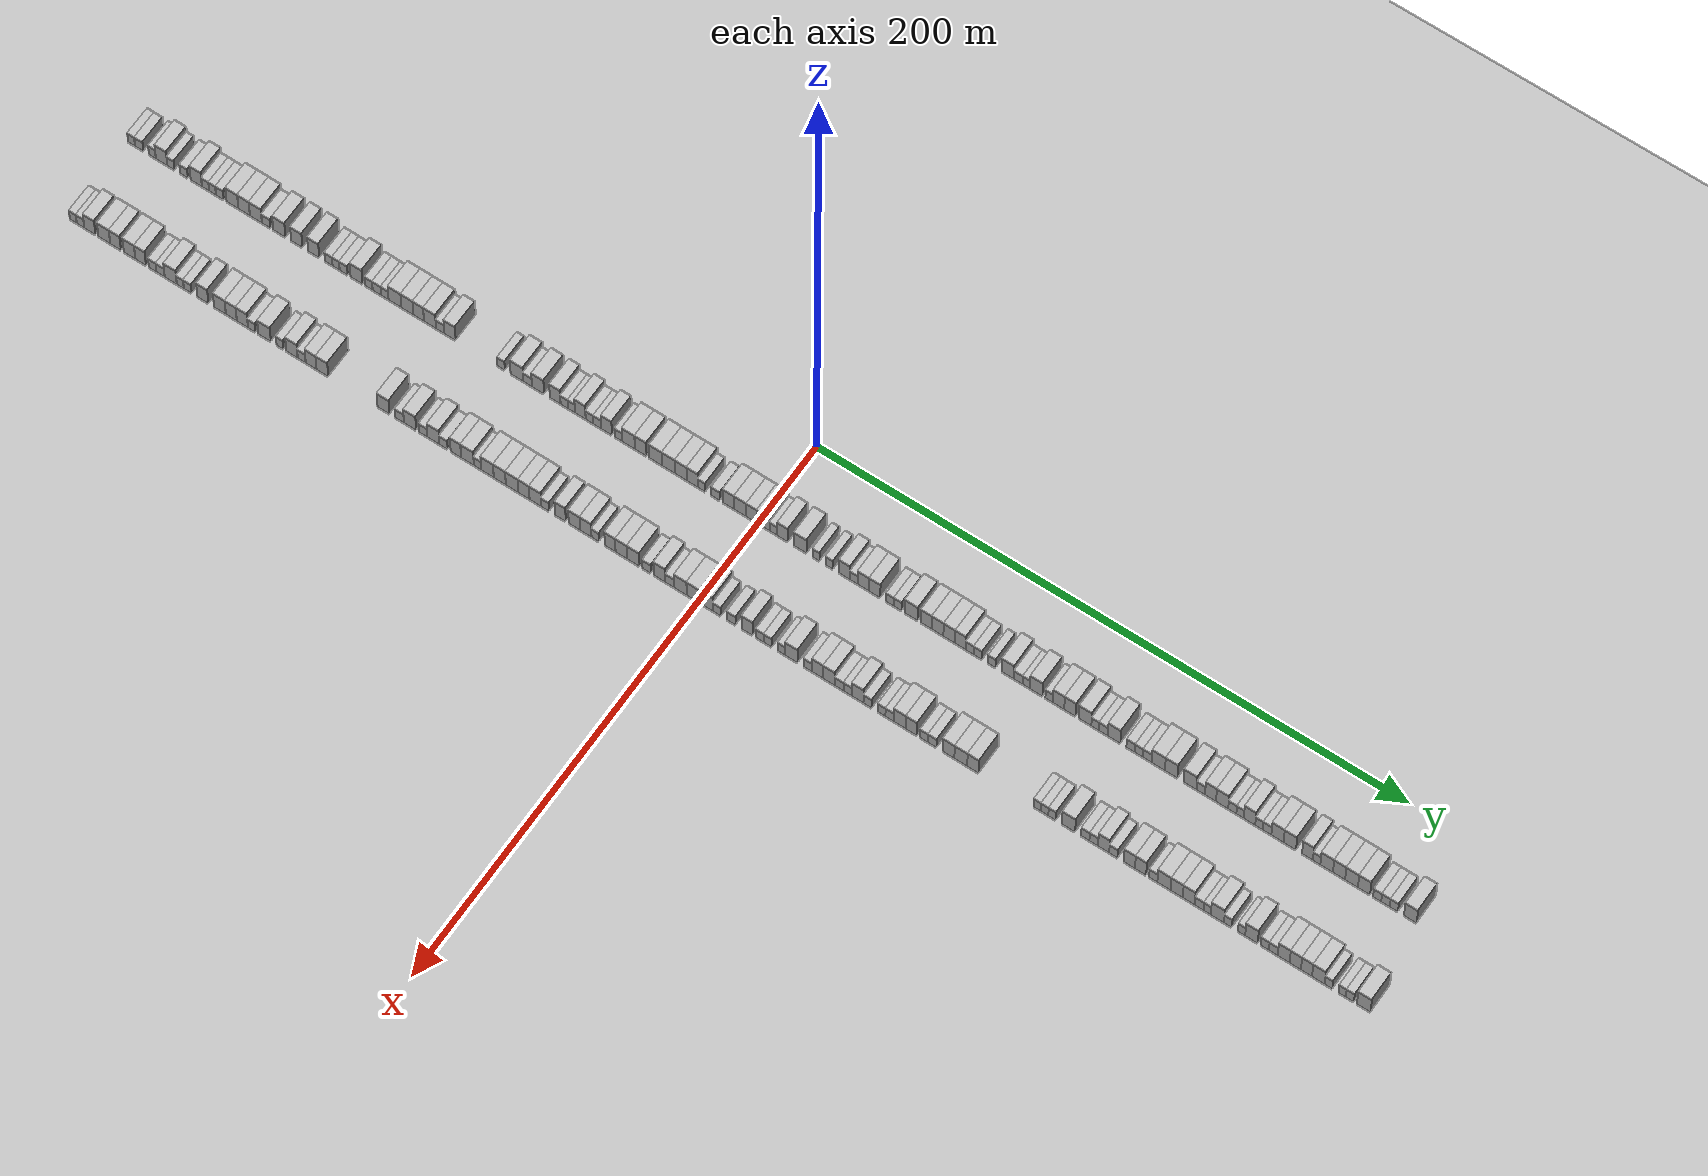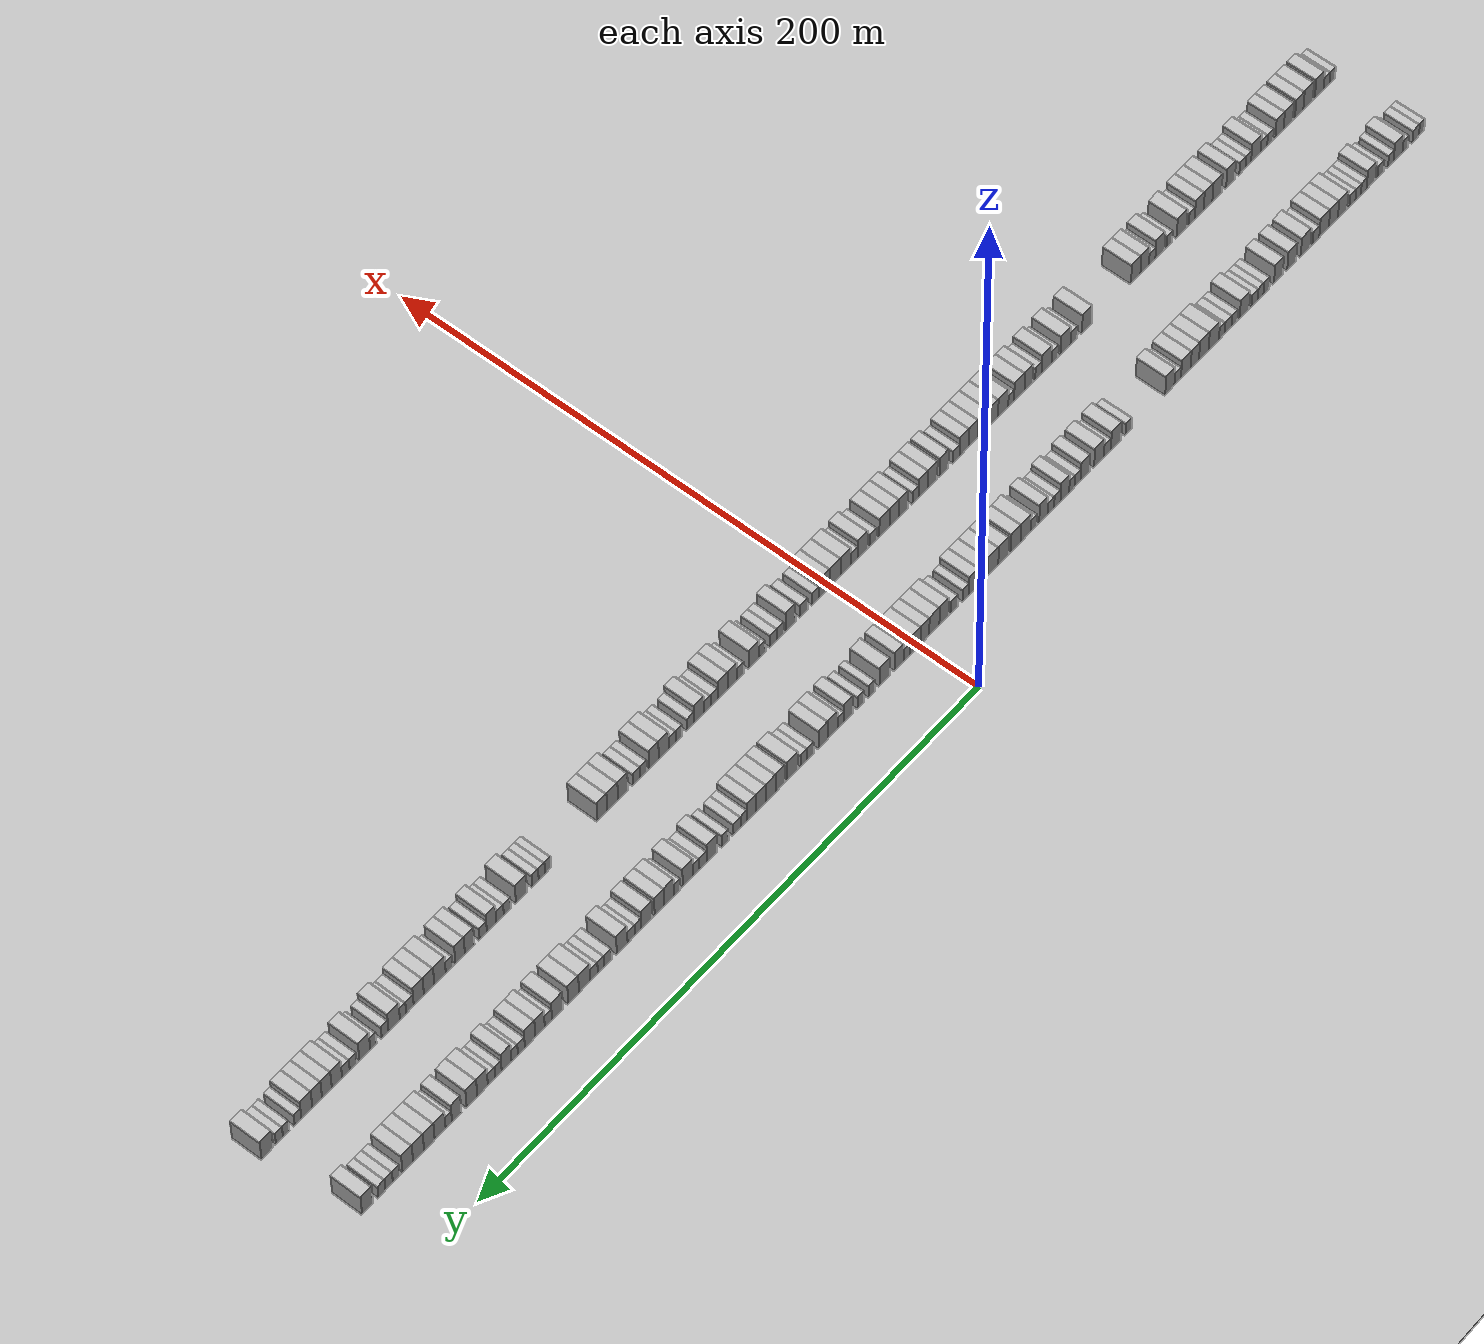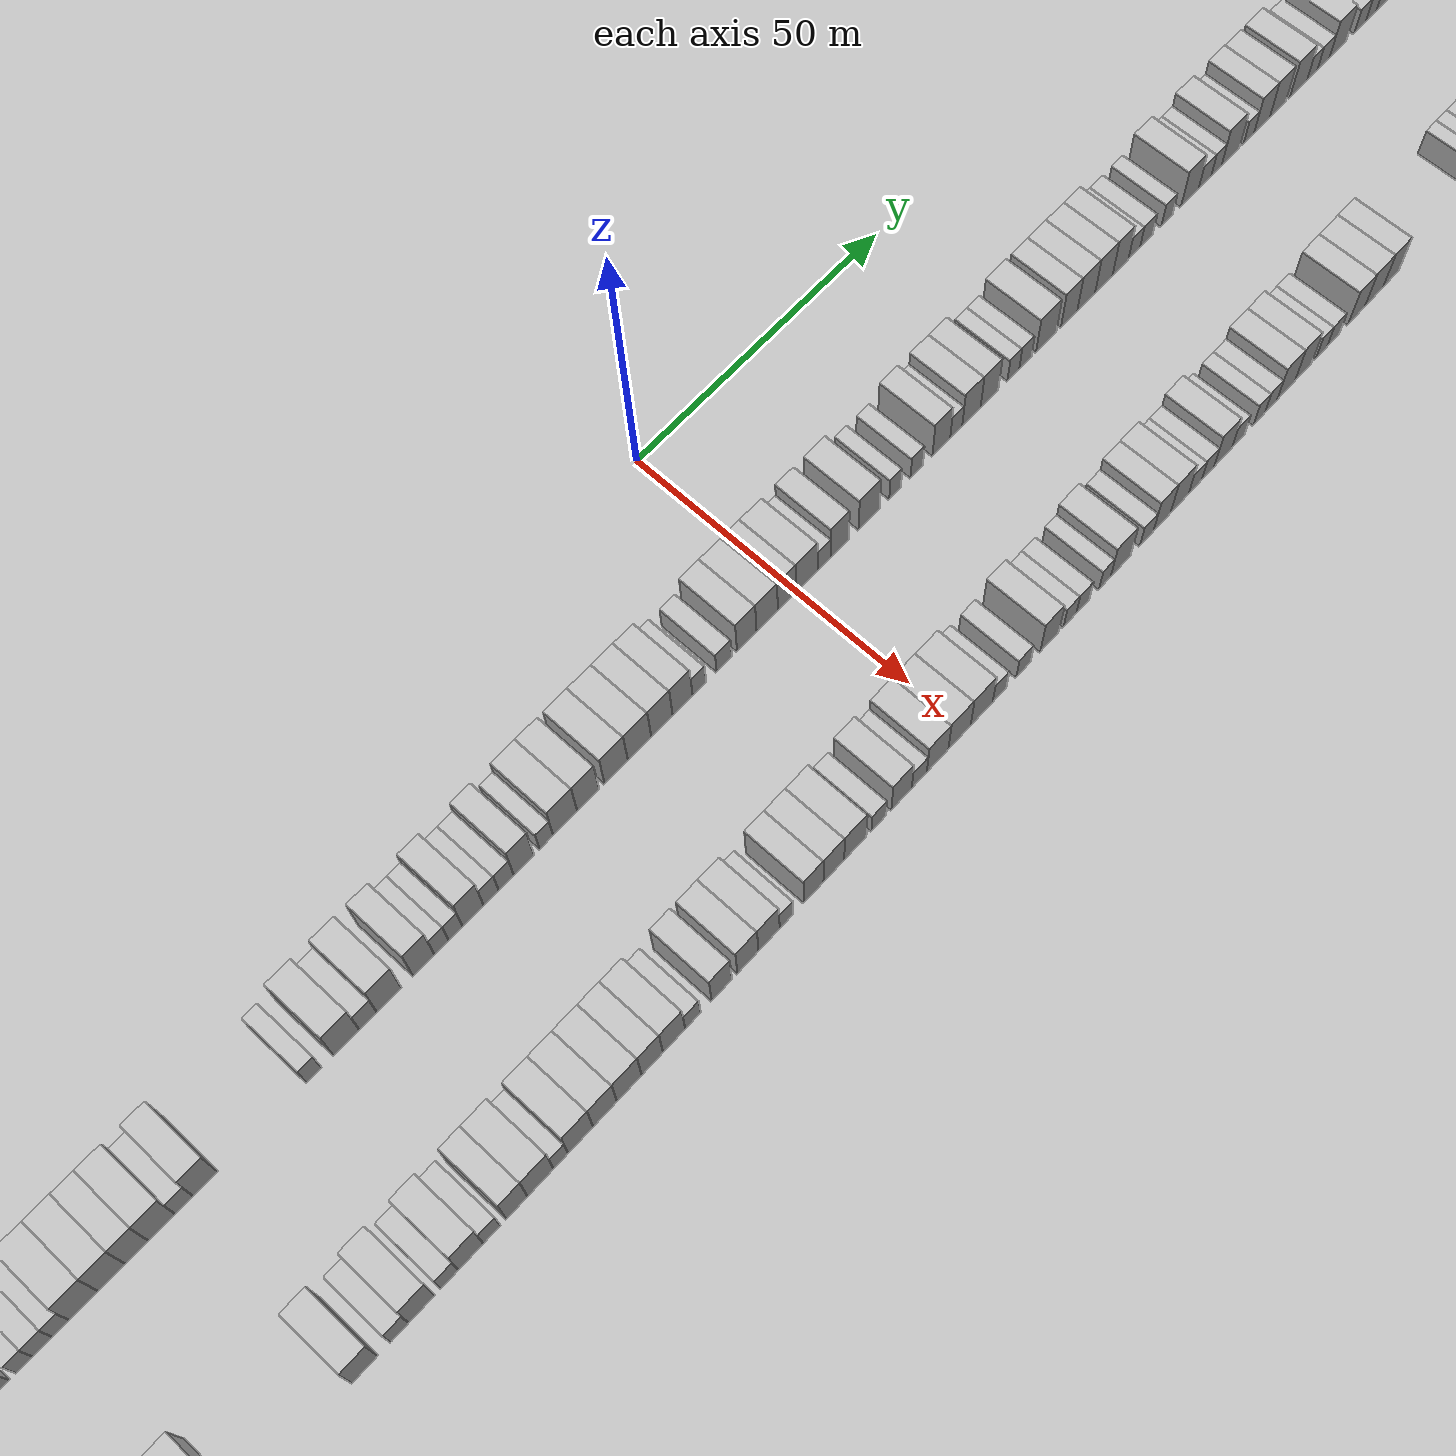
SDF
<?xml version="1.0" encoding="utf-8"?>

<sdf version="1.6">

   <world name="default">

      <gui fullscreen="0">

         <camera name="user_camera">

            <pose>-15 0 4.57585 0 0 0</pose>

            <view_controller>orbit</view_controller>

         </camera>

      </gui>

      <scene>

         <sky>

           <clouds>

             <speed>12</speed>

           </clouds>

         </sky>

         <ambient>0.4 0.4 0.4 1</ambient>

         <background>0.7 0.7 0.7 1</background>

         <shadows>1</shadows>

      </scene>

      <gravity>0 0 -9.8066</gravity>

      <magnetic_field>6e-06 2.3e-05 -4.2e-05</magnetic_field>

      <physics default="0" name="default_physics" type="ode">

         <ode>

            <solver>

               <type>quick</type>

               <iters>10</iters>

               <sor>1.0</sor>

               <use_dynamic_moi_rescaling>0</use_dynamic_moi_rescaling>

            </solver>

            <constraints>

               <cfm>0</cfm>

               <erp>0.2</erp>

               <contact_max_correcting_vel>100</contact_max_correcting_vel>

               <contact_surface_layer>0.001</contact_surface_layer>

            </constraints>

         </ode>

         <max_step_size>0.004</max_step_size>

         <real_time_factor>1</real_time_factor>

         <real_time_update_rate>250</real_time_update_rate>

      </physics>

      <light name="sun" type="directional">

         <cast_shadows>1</cast_shadows>

         <pose>0 0 10 0 0 0</pose>

         <diffuse>0.8 0.8 0.8 1</diffuse>

         <specular>0.2 0.2 0.2 1</specular>

         <attenuation>

            <range>1000</range>

            <constant>0.9</constant>

            <linear>0.01</linear>

            <quadratic>0.001</quadratic>

         </attenuation>

         <direction>-0.5 0.1 -0.9</direction>

      </light>

      <include>

         <name>ground_plane_1</name>

         <uri>model://HANNAS_ground_plane</uri>

         <pose>0 0 0  0 0 0</pose>

      </include>

      <include>

         <name>ground_plane_2</name>

         <uri>model://HANNAS_ground_plane</uri>

         <pose>100 0 0  0 0 0</pose>

      </include>

      <model name="building_1">

         <static>1</static>

         <pose frame="">25.0000 -218.7764 0 0.000000 0.000000 0.000000</pose>

         <link name="link">

            <pose frame="">0 0 3.00 0 0 0</pose>

            <collision name="collision">

               <geometry>

                  <box>

                     <size>10.0000 2.4473 6.0000</size>

                  </box>

               </geometry>

               <max_contacts>10</max_contacts>

               <surface>

                  <contact>

                     <ode/>

                  </contact>

                  <bounce/>

                  <friction>

                     <torsional>

                        <ode/>

                     </torsional>

                     <ode/>

                  </friction>

               </surface>

            </collision>

            <visual name="visual">

               <cast_shadows>0</cast_shadows>

               <geometry>

                  <box>

                     <size>10.0000 2.4473 6.0000</size>

                  </box>

               </geometry>

               <material>

                  <script>

                     <uri>model://HANNAS_wall/materials/scripts</uri>

                     <uri>model://HANNAS_wall/materials/textures</uri>

                     <name>vrc/HANNAS_wall</name>

                  </script>

               </material>

            </visual>

            <self_collide>0</self_collide>

            <enable_wind>0</enable_wind>

            <kinematic>0</kinematic>

         </link>

      </model>

      <model name="building_2">

         <static>1</static>

         <pose frame="">25.0000 -216.0781 0 0.000000 0.000000 0.000000</pose>

         <link name="link">

            <pose frame="">0 0 3.00 0 0 0</pose>

            <collision name="collision">

               <geometry>

                  <box>

                     <size>10.0000 2.9493 6.0000</size>

                  </box>

               </geometry>

               <max_contacts>10</max_contacts>

               <surface>

                  <contact>

                     <ode/>

                  </contact>

                  <bounce/>

                  <friction>

                     <torsional>

                        <ode/>

                     </torsional>

                     <ode/>

                  </friction>

               </surface>

            </collision>

            <visual name="visual">

               <cast_shadows>0</cast_shadows>

               <geometry>

                  <box>

                     <size>10.0000 2.9493 6.0000</size>

                  </box>

               </geometry>

               <material>

                  <script>

                     <uri>model://HANNAS_wall/materials/scripts</uri>

                     <uri>model://HANNAS_wall/materials/textures</uri>

                     <name>vrc/HANNAS_wall</name>

                  </script>

               </material>

            </visual>

            <self_collide>0</self_collide>

            <enable_wind>0</enable_wind>

            <kinematic>0</kinematic>

         </link>

      </model>

      <model name="building_3">

         <static>1</static>

         <pose frame="">25.0000 -211.3653 0 0.000000 0.000000 0.000000</pose>

         <link name="link">

            <pose frame="">0 0 3.00 0 0 0</pose>

            <collision name="collision">

               <geometry>

                  <box>

                     <size>10.0000 2.4762 6.0000</size>

                  </box>

               </geometry>

               <max_contacts>10</max_contacts>

               <surface>

                  <contact>

                     <ode/>

                  </contact>

                  <bounce/>

                  <friction>

                     <torsional>

                        <ode/>

                     </torsional>

                     <ode/>

                  </friction>

               </surface>

            </collision>

            <visual name="visual">

               <cast_shadows>0</cast_shadows>

               <geometry>

                  <box>

                     <size>10.0000 2.4762 6.0000</size>

                  </box>

               </geometry>

               <material>

                  <script>

                     <uri>model://HANNAS_wall/materials/scripts</uri>

                     <uri>model://HANNAS_wall/materials/textures</uri>

                     <name>vrc/HANNAS_wall</name>

                  </script>

               </material>

            </visual>

            <self_collide>0</self_collide>

            <enable_wind>0</enable_wind>

            <kinematic>0</kinematic>

         </link>

      </model>

      <model name="building_4">

         <static>1</static>

         <pose frame="">25.0000 -208.0917 0 0.000000 0.000000 0.000000</pose>

         <link name="link">

            <pose frame="">0 0 4.50 0 0 0</pose>

            <collision name="collision">

               <geometry>

                  <box>

                     <size>10.0000 4.0710 9.0000</size>

                  </box>

               </geometry>

               <max_contacts>10</max_contacts>

               <surface>

                  <contact>

                     <ode/>

                  </contact>

                  <bounce/>

                  <friction>

                     <torsional>

                        <ode/>

                     </torsional>

                     <ode/>

                  </friction>

               </surface>

            </collision>

            <visual name="visual">

               <cast_shadows>0</cast_shadows>

               <geometry>

                  <box>

                     <size>10.0000 4.0710 9.0000</size>

                  </box>

               </geometry>

               <material>

                  <script>

                     <uri>model://HANNAS_wall/materials/scripts</uri>

                     <uri>model://HANNAS_wall/materials/textures</uri>

                     <name>vrc/HANNAS_wall</name>

                  </script>

               </material>

            </visual>

            <self_collide>0</self_collide>

            <enable_wind>0</enable_wind>

            <kinematic>0</kinematic>

         </link>

      </model>

      <model name="building_5">

         <static>1</static>

         <pose frame="">25.0000 -204.7895 0 0.000000 0.000000 0.000000</pose>

         <link name="link">

            <pose frame="">0 0 3.00 0 0 0</pose>

            <collision name="collision">

               <geometry>

                  <box>

                     <size>10.0000 2.5335 6.0000</size>

                  </box>

               </geometry>

               <max_contacts>10</max_contacts>

               <surface>

                  <contact>

                     <ode/>

                  </contact>

                  <bounce/>

                  <friction>

                     <torsional>

                        <ode/>

                     </torsional>

                     <ode/>

                  </friction>

               </surface>

            </collision>

            <visual name="visual">

               <cast_shadows>0</cast_shadows>

               <geometry>

                  <box>

                     <size>10.0000 2.5335 6.0000</size>

                  </box>

               </geometry>

               <material>

                  <script>

                     <uri>model://HANNAS_wall/materials/scripts</uri>

                     <uri>model://HANNAS_wall/materials/textures</uri>

                     <name>vrc/HANNAS_wall</name>

                  </script>

               </material>

            </visual>

            <self_collide>0</self_collide>

            <enable_wind>0</enable_wind>

            <kinematic>0</kinematic>

         </link>

      </model>

      <model name="building_6">

         <static>1</static>

         <pose frame="">25.0000 -200.1600 0 0.000000 0.000000 0.000000</pose>

         <link name="link">

            <pose frame="">0 0 3.00 0 0 0</pose>

            <collision name="collision">

               <geometry>

                  <box>

                     <size>10.0000 2.7254 6.0000</size>

                  </box>

               </geometry>

               <max_contacts>10</max_contacts>

               <surface>

                  <contact>

                     <ode/>

                  </contact>

                  <bounce/>

                  <friction>

                     <torsional>

                        <ode/>

                     </torsional>

                     <ode/>

                  </friction>

               </surface>

            </collision>

            <visual name="visual">

               <cast_shadows>0</cast_shadows>

               <geometry>

                  <box>

                     <size>10.0000 2.7254 6.0000</size>

                  </box>

               </geometry>

               <material>

                  <script>

                     <uri>model://HANNAS_wall/materials/scripts</uri>

                     <uri>model://HANNAS_wall/materials/textures</uri>

                     <name>vrc/HANNAS_wall</name>

                  </script>

               </material>

            </visual>

            <self_collide>0</self_collide>

            <enable_wind>0</enable_wind>

            <kinematic>0</kinematic>

         </link>

      </model>

      <model name="building_7">

         <static>1</static>

         <pose frame="">25.0000 -195.8022 0 0.000000 0.000000 0.000000</pose>

         <link name="link">

            <pose frame="">0 0 4.50 0 0 0</pose>

            <collision name="collision">

               <geometry>

                  <box>

                     <size>10.0000 3.9903 9.0000</size>

                  </box>

               </geometry>

               <max_contacts>10</max_contacts>

               <surface>

                  <contact>

                     <ode/>

                  </contact>

                  <bounce/>

                  <friction>

                     <torsional>

                        <ode/>

                     </torsional>

                     <ode/>

                  </friction>

               </surface>

            </collision>

            <visual name="visual">

               <cast_shadows>0</cast_shadows>

               <geometry>

                  <box>

                     <size>10.0000 3.9903 9.0000</size>

                  </box>

               </geometry>

               <material>

                  <script>

                     <uri>model://HANNAS_wall/materials/scripts</uri>

                     <uri>model://HANNAS_wall/materials/textures</uri>

                     <name>vrc/HANNAS_wall</name>

                  </script>

               </material>

            </visual>

            <self_collide>0</self_collide>

            <enable_wind>0</enable_wind>

            <kinematic>0</kinematic>

         </link>

      </model>

      <model name="building_8">

         <static>1</static>

         <pose frame="">25.0000 -192.5255 0 0.000000 0.000000 0.000000</pose>

         <link name="link">

            <pose frame="">0 0 3.00 0 0 0</pose>

            <collision name="collision">

               <geometry>

                  <box>

                     <size>10.0000 2.5631 6.0000</size>

                  </box>

               </geometry>

               <max_contacts>10</max_contacts>

               <surface>

                  <contact>

                     <ode/>

                  </contact>

                  <bounce/>

                  <friction>

                     <torsional>

                        <ode/>

                     </torsional>

                     <ode/>

                  </friction>

               </surface>

            </collision>

            <visual name="visual">

               <cast_shadows>0</cast_shadows>

               <geometry>

                  <box>

                     <size>10.0000 2.5631 6.0000</size>

                  </box>

               </geometry>

               <material>

                  <script>

                     <uri>model://HANNAS_wall/materials/scripts</uri>

                     <uri>model://HANNAS_wall/materials/textures</uri>

                     <name>vrc/HANNAS_wall</name>

                  </script>

               </material>

            </visual>

            <self_collide>0</self_collide>

            <enable_wind>0</enable_wind>

            <kinematic>0</kinematic>

         </link>

      </model>

      <model name="building_9">

         <static>1</static>

         <pose frame="">25.0000 -190.0301 0 0.000000 0.000000 0.000000</pose>

         <link name="link">

            <pose frame="">0 0 3.00 0 0 0</pose>

            <collision name="collision">

               <geometry>

                  <box>

                     <size>10.0000 2.4276 6.0000</size>

                  </box>

               </geometry>

               <max_contacts>10</max_contacts>

               <surface>

                  <contact>

                     <ode/>

                  </contact>

                  <bounce/>

                  <friction>

                     <torsional>

                        <ode/>

                     </torsional>

                     <ode/>

                  </friction>

               </surface>

            </collision>

            <visual name="visual">

               <cast_shadows>0</cast_shadows>

               <geometry>

                  <box>

                     <size>10.0000 2.4276 6.0000</size>

                  </box>

               </geometry>

               <material>

                  <script>

                     <uri>model://HANNAS_wall/materials/scripts</uri>

                     <uri>model://HANNAS_wall/materials/textures</uri>

                     <name>vrc/HANNAS_wall</name>

                  </script>

               </material>

            </visual>

            <self_collide>0</self_collide>

            <enable_wind>0</enable_wind>

            <kinematic>0</kinematic>

         </link>

      </model>

      <model name="building_10">

         <static>1</static>

         <pose frame="">25.0000 -187.4523 0 0.000000 0.000000 0.000000</pose>

         <link name="link">

            <pose frame="">0 0 3.00 0 0 0</pose>

            <collision name="collision">

               <geometry>

                  <box>

                     <size>10.0000 2.7280 6.0000</size>

                  </box>

               </geometry>

               <max_contacts>10</max_contacts>

               <surface>

                  <contact>

                     <ode/>

                  </contact>

                  <bounce/>

                  <friction>

                     <torsional>

                        <ode/>

                     </torsional>

                     <ode/>

                  </friction>

               </surface>

            </collision>

            <visual name="visual">

               <cast_shadows>0</cast_shadows>

               <geometry>

                  <box>

                     <size>10.0000 2.7280 6.0000</size>

                  </box>

               </geometry>

               <material>

                  <script>

                     <uri>model://HANNAS_wall/materials/scripts</uri>

                     <uri>model://HANNAS_wall/materials/textures</uri>

                     <name>vrc/HANNAS_wall</name>

                  </script>

               </material>

            </visual>

            <self_collide>0</self_collide>

            <enable_wind>0</enable_wind>

            <kinematic>0</kinematic>

         </link>

      </model>

      <model name="building_11">

         <static>1</static>

         <pose frame="">25.0000 -182.9950 0 0.000000 0.000000 0.000000</pose>

         <link name="link">

            <pose frame="">0 0 4.50 0 0 0</pose>

            <collision name="collision">

               <geometry>

                  <box>

                     <size>10.0000 4.1866 9.0000</size>

                  </box>

               </geometry>

               <max_contacts>10</max_contacts>

               <surface>

                  <contact>

                     <ode/>

                  </contact>

                  <bounce/>

                  <friction>

                     <torsional>

                        <ode/>

                     </torsional>

                     <ode/>

                  </friction>

               </surface>

            </collision>

            <visual name="visual">

               <cast_shadows>0</cast_shadows>

               <geometry>

                  <box>

                     <size>10.0000 4.1866 9.0000</size>

                  </box>

               </geometry>

               <material>

                  <script>

                     <uri>model://HANNAS_wall/materials/scripts</uri>

                     <uri>model://HANNAS_wall/materials/textures</uri>

                     <name>vrc/HANNAS_wall</name>

                  </script>

               </material>

            </visual>

            <self_collide>0</self_collide>

            <enable_wind>0</enable_wind>

            <kinematic>0</kinematic>

         </link>

      </model>

      <model name="building_12">

         <static>1</static>

         <pose frame="">25.0000 -178.8758 0 0.000000 0.000000 0.000000</pose>

         <link name="link">

            <pose frame="">0 0 4.50 0 0 0</pose>

            <collision name="collision">

               <geometry>

                  <box>

                     <size>10.0000 4.0518 9.0000</size>

                  </box>

               </geometry>

               <max_contacts>10</max_contacts>

               <surface>

                  <contact>

                     <ode/>

                  </contact>

                  <bounce/>

                  <friction>

                     <torsional>

                        <ode/>

                     </torsional>

                     <ode/>

                  </friction>

               </surface>

            </collision>

            <visual name="visual">

               <cast_shadows>0</cast_shadows>

               <geometry>

                  <box>

                     <size>10.0000 4.0518 9.0000</size>

                  </box>

               </geometry>

               <material>

                  <script>

                     <uri>model://HANNAS_wall/materials/scripts</uri>

                     <uri>model://HANNAS_wall/materials/textures</uri>

                     <name>vrc/HANNAS_wall</name>

                  </script>

               </material>

            </visual>

            <self_collide>0</self_collide>

            <enable_wind>0</enable_wind>

            <kinematic>0</kinematic>

         </link>

      </model>

      <model name="building_13">

         <static>1</static>

         <pose frame="">25.0000 -174.7179 0 0.000000 0.000000 0.000000</pose>

         <link name="link">

            <pose frame="">0 0 4.50 0 0 0</pose>

            <collision name="collision">

               <geometry>

                  <box>

                     <size>10.0000 4.2640 9.0000</size>

                  </box>

               </geometry>

               <max_contacts>10</max_contacts>

               <surface>

                  <contact>

                     <ode/>

                  </contact>

                  <bounce/>

                  <friction>

                     <torsional>

                        <ode/>

                     </torsional>

                     <ode/>

                  </friction>

               </surface>

            </collision>

            <visual name="visual">

               <cast_shadows>0</cast_shadows>

               <geometry>

                  <box>

                     <size>10.0000 4.2640 9.0000</size>

                  </box>

               </geometry>

               <material>

                  <script>

                     <uri>model://HANNAS_wall/materials/scripts</uri>

                     <uri>model://HANNAS_wall/materials/textures</uri>

                     <name>vrc/HANNAS_wall</name>

                  </script>

               </material>

            </visual>

            <self_collide>0</self_collide>

            <enable_wind>0</enable_wind>

            <kinematic>0</kinematic>

         </link>

      </model>

      <model name="building_14">

         <static>1</static>

         <pose frame="">25.0000 -171.0963 0 0.000000 0.000000 0.000000</pose>

         <link name="link">

            <pose frame="">0 0 3.00 0 0 0</pose>

            <collision name="collision">

               <geometry>

                  <box>

                     <size>10.0000 2.9792 6.0000</size>

                  </box>

               </geometry>

               <max_contacts>10</max_contacts>

               <surface>

                  <contact>

                     <ode/>

                  </contact>

                  <bounce/>

                  <friction>

                     <torsional>

                        <ode/>

                     </torsional>

                     <ode/>

                  </friction>

               </surface>

            </collision>

            <visual name="visual">

               <cast_shadows>0</cast_shadows>

               <geometry>

                  <box>

                     <size>10.0000 2.9792 6.0000</size>

                  </box>

               </geometry>

               <material>

                  <script>

                     <uri>model://HANNAS_wall/materials/scripts</uri>

                     <uri>model://HANNAS_wall/materials/textures</uri>

                     <name>vrc/HANNAS_wall</name>

                  </script>

               </material>

            </visual>

            <self_collide>0</self_collide>

            <enable_wind>0</enable_wind>

            <kinematic>0</kinematic>

         </link>

      </model>

      <model name="building_15">

         <static>1</static>

         <pose frame="">25.0000 -166.4477 0 0.000000 0.000000 0.000000</pose>

         <link name="link">

            <pose frame="">0 0 4.50 0 0 0</pose>

            <collision name="collision">

               <geometry>

                  <box>

                     <size>10.0000 4.3180 9.0000</size>

                  </box>

               </geometry>

               <max_contacts>10</max_contacts>

               <surface>

                  <contact>

                     <ode/>

                  </contact>

                  <bounce/>

                  <friction>

                     <torsional>

                        <ode/>

                     </torsional>

                     <ode/>

                  </friction>

               </surface>

            </collision>

            <visual name="visual">

               <cast_shadows>0</cast_shadows>

               <geometry>

                  <box>

                     <size>10.0000 4.3180 9.0000</size>

                  </box>

               </geometry>

               <material>

                  <script>

                     <uri>model://HANNAS_wall/materials/scripts</uri>

                     <uri>model://HANNAS_wall/materials/textures</uri>

                     <name>vrc/HANNAS_wall</name>

                  </script>

               </material>

            </visual>

            <self_collide>0</self_collide>

            <enable_wind>0</enable_wind>

            <kinematic>0</kinematic>

         </link>

      </model>

      <model name="building_16">

         <static>1</static>

         <pose frame="">25.0000 -160.2883 0 0.000000 0.000000 0.000000</pose>

         <link name="link">

            <pose frame="">0 0 4.50 0 0 0</pose>

            <collision name="collision">

               <geometry>

                  <box>

                     <size>10.0000 4.0009 9.0000</size>

                  </box>

               </geometry>

               <max_contacts>10</max_contacts>

               <surface>

                  <contact>

                     <ode/>

                  </contact>

                  <bounce/>

                  <friction>

                     <torsional>

                        <ode/>

                     </torsional>

                     <ode/>

                  </friction>

               </surface>

            </collision>

            <visual name="visual">

               <cast_shadows>0</cast_shadows>

               <geometry>

                  <box>

                     <size>10.0000 4.0009 9.0000</size>

                  </box>

               </geometry>

               <material>

                  <script>

                     <uri>model://HANNAS_wall/materials/scripts</uri>

                     <uri>model://HANNAS_wall/materials/textures</uri>

                     <name>vrc/HANNAS_wall</name>

                  </script>

               </material>

            </visual>

            <self_collide>0</self_collide>

            <enable_wind>0</enable_wind>

            <kinematic>0</kinematic>

         </link>

      </model>

      <model name="building_17">

         <static>1</static>

         <pose frame="">25.0000 -154.3326 0 0.000000 0.000000 0.000000</pose>

         <link name="link">

            <pose frame="">0 0 4.50 0 0 0</pose>

            <collision name="collision">

               <geometry>

                  <box>

                     <size>10.0000 3.9105 9.0000</size>

                  </box>

               </geometry>

               <max_contacts>10</max_contacts>

               <surface>

                  <contact>

                     <ode/>

                  </contact>

                  <bounce/>

                  <friction>

                     <torsional>

                        <ode/>

                     </torsional>

                     <ode/>

                  </friction>

               </surface>

            </collision>

            <visual name="visual">

               <cast_shadows>0</cast_shadows>

               <geometry>

                  <box>

                     <size>10.0000 3.9105 9.0000</size>

                  </box>

               </geometry>

               <material>

                  <script>

                     <uri>model://HANNAS_wall/materials/scripts</uri>

                     <uri>model://HANNAS_wall/materials/textures</uri>

                     <name>vrc/HANNAS_wall</name>

                  </script>

               </material>

            </visual>

            <self_collide>0</self_collide>

            <enable_wind>0</enable_wind>

            <kinematic>0</kinematic>

         </link>

      </model>

      <model name="building_18">

         <static>1</static>

         <pose frame="">25.0000 -149.0490 0 0.000000 0.000000 0.000000</pose>

         <link name="link">

            <pose frame="">0 0 3.00 0 0 0</pose>

            <collision name="collision">

               <geometry>

                  <box>

                     <size>10.0000 2.6568 6.0000</size>

                  </box>

               </geometry>

               <max_contacts>10</max_contacts>

               <surface>

                  <contact>

                     <ode/>

                  </contact>

                  <bounce/>

                  <friction>

                     <torsional>

                        <ode/>

                     </torsional>

                     <ode/>

                  </friction>

               </surface>

            </collision>

            <visual name="visual">

               <cast_shadows>0</cast_shadows>

               <geometry>

                  <box>

                     <size>10.0000 2.6568 6.0000</size>

                  </box>

               </geometry>

               <material>

                  <script>

                     <uri>model://HANNAS_wall/materials/scripts</uri>

                     <uri>model://HANNAS_wall/materials/textures</uri>

                     <name>vrc/HANNAS_wall</name>

                  </script>

               </material>

            </visual>

            <self_collide>0</self_collide>

            <enable_wind>0</enable_wind>

            <kinematic>0</kinematic>

         </link>

      </model>

      <model name="building_19">

         <static>1</static>

         <pose frame="">25.0000 -146.4753 0 0.000000 0.000000 0.000000</pose>

         <link name="link">

            <pose frame="">0 0 3.00 0 0 0</pose>

            <collision name="collision">

               <geometry>

                  <box>

                     <size>10.0000 2.4906 6.0000</size>

                  </box>

               </geometry>

               <max_contacts>10</max_contacts>

               <surface>

                  <contact>

                     <ode/>

                  </contact>

                  <bounce/>

                  <friction>

                     <torsional>

                        <ode/>

                     </torsional>

                     <ode/>

                  </friction>

               </surface>

            </collision>

            <visual name="visual">

               <cast_shadows>0</cast_shadows>

               <geometry>

                  <box>

                     <size>10.0000 2.4906 6.0000</size>

                  </box>

               </geometry>

               <material>

                  <script>

                     <uri>model://HANNAS_wall/materials/scripts</uri>

                     <uri>model://HANNAS_wall/materials/textures</uri>

                     <name>vrc/HANNAS_wall</name>

                  </script>

               </material>

            </visual>

            <self_collide>0</self_collide>

            <enable_wind>0</enable_wind>

            <kinematic>0</kinematic>

         </link>

      </model>

      <model name="building_20">

         <static>1</static>

         <pose frame="">25.0000 -143.8111 0 0.000000 0.000000 0.000000</pose>

         <link name="link">

            <pose frame="">0 0 3.00 0 0 0</pose>

            <collision name="collision">

               <geometry>

                  <box>

                     <size>10.0000 2.8379 6.0000</size>

                  </box>

               </geometry>

               <max_contacts>10</max_contacts>

               <surface>

                  <contact>

                     <ode/>

                  </contact>

                  <bounce/>

                  <friction>

                     <torsional>

                        <ode/>

                     </torsional>

                     <ode/>

                  </friction>

               </surface>

            </collision>

            <visual name="visual">

               <cast_shadows>0</cast_shadows>

               <geometry>

                  <box>

                     <size>10.0000 2.8379 6.0000</size>

                  </box>

               </geometry>

               <material>

                  <script>

                     <uri>model://HANNAS_wall/materials/scripts</uri>

                     <uri>model://HANNAS_wall/materials/textures</uri>

                     <name>vrc/HANNAS_wall</name>

                  </script>

               </material>

            </visual>

            <self_collide>0</self_collide>

            <enable_wind>0</enable_wind>

            <kinematic>0</kinematic>

         </link>

      </model>

      <model name="building_21">

         <static>1</static>

         <pose frame="">25.0000 -139.2930 0 0.000000 0.000000 0.000000</pose>

         <link name="link">

            <pose frame="">0 0 4.50 0 0 0</pose>

            <collision name="collision">

               <geometry>

                  <box>

                     <size>10.0000 4.1983 9.0000</size>

                  </box>

               </geometry>

               <max_contacts>10</max_contacts>

               <surface>

                  <contact>

                     <ode/>

                  </contact>

                  <bounce/>

                  <friction>

                     <torsional>

                        <ode/>

                     </torsional>

                     <ode/>

                  </friction>

               </surface>

            </collision>

            <visual name="visual">

               <cast_shadows>0</cast_shadows>

               <geometry>

                  <box>

                     <size>10.0000 4.1983 9.0000</size>

                  </box>

               </geometry>

               <material>

                  <script>

                     <uri>model://HANNAS_wall/materials/scripts</uri>

                     <uri>model://HANNAS_wall/materials/textures</uri>

                     <name>vrc/HANNAS_wall</name>

                  </script>

               </material>

            </visual>

            <self_collide>0</self_collide>

            <enable_wind>0</enable_wind>

            <kinematic>0</kinematic>

         </link>

      </model>

      <model name="building_22">

         <static>1</static>

         <pose frame="">25.0000 -134.9228 0 0.000000 0.000000 0.000000</pose>

         <link name="link">

            <pose frame="">0 0 3.00 0 0 0</pose>

            <collision name="collision">

               <geometry>

                  <box>

                     <size>10.0000 2.5419 6.0000</size>

                  </box>

               </geometry>

               <max_contacts>10</max_contacts>

               <surface>

                  <contact>

                     <ode/>

                  </contact>

                  <bounce/>

                  <friction>

                     <torsional>

                        <ode/>

                     </torsional>

                     <ode/>

                  </friction>

               </surface>

            </collision>

            <visual name="visual">

               <cast_shadows>0</cast_shadows>

               <geometry>

                  <box>

                     <size>10.0000 2.5419 6.0000</size>

                  </box>

               </geometry>

               <material>

                  <script>

                     <uri>model://HANNAS_wall/materials/scripts</uri>

                     <uri>model://HANNAS_wall/materials/textures</uri>

                     <name>vrc/HANNAS_wall</name>

                  </script>

               </material>

            </visual>

            <self_collide>0</self_collide>

            <enable_wind>0</enable_wind>

            <kinematic>0</kinematic>

         </link>

      </model>

      <model name="building_23">

         <static>1</static>

         <pose frame="">25.0000 -132.1581 0 0.000000 0.000000 0.000000</pose>

         <link name="link">

            <pose frame="">0 0 3.00 0 0 0</pose>

            <collision name="collision">

               <geometry>

                  <box>

                     <size>10.0000 2.9876 6.0000</size>

                  </box>

               </geometry>

               <max_contacts>10</max_contacts>

               <surface>

                  <contact>

                     <ode/>

                  </contact>

                  <bounce/>

                  <friction>

                     <torsional>

                        <ode/>

                     </torsional>

                     <ode/>

                  </friction>

               </surface>

            </collision>

            <visual name="visual">

               <cast_shadows>0</cast_shadows>

               <geometry>

                  <box>

                     <size>10.0000 2.9876 6.0000</size>

                  </box>

               </geometry>

               <material>

                  <script>

                     <uri>model://HANNAS_wall/materials/scripts</uri>

                     <uri>model://HANNAS_wall/materials/textures</uri>

                     <name>vrc/HANNAS_wall</name>

                  </script>

               </material>

            </visual>

            <self_collide>0</self_collide>

            <enable_wind>0</enable_wind>

            <kinematic>0</kinematic>

         </link>

      </model>

      <model name="building_24">

         <static>1</static>

         <pose frame="">25.0000 -129.3684 0 0.000000 0.000000 0.000000</pose>

         <link name="link">

            <pose frame="">0 0 3.00 0 0 0</pose>

            <collision name="collision">

               <geometry>

                  <box>

                     <size>10.0000 2.5917 6.0000</size>

                  </box>

               </geometry>

               <max_contacts>10</max_contacts>

               <surface>

                  <contact>

                     <ode/>

                  </contact>

                  <bounce/>

                  <friction>

                     <torsional>

                        <ode/>

                     </torsional>

                     <ode/>

                  </friction>

               </surface>

            </collision>

            <visual name="visual">

               <cast_shadows>0</cast_shadows>

               <geometry>

                  <box>

                     <size>10.0000 2.5917 6.0000</size>

                  </box>

               </geometry>

               <material>

                  <script>

                     <uri>model://HANNAS_wall/materials/scripts</uri>

                     <uri>model://HANNAS_wall/materials/textures</uri>

                     <name>vrc/HANNAS_wall</name>

                  </script>

               </material>

            </visual>

            <self_collide>0</self_collide>

            <enable_wind>0</enable_wind>

            <kinematic>0</kinematic>

         </link>

      </model>

      <model name="building_25">

         <static>1</static>

         <pose frame="">25.0000 -125.8287 0 0.000000 0.000000 0.000000</pose>

         <link name="link">

            <pose frame="">0 0 4.50 0 0 0</pose>

            <collision name="collision">

               <geometry>

                  <box>

                     <size>10.0000 4.4878 9.0000</size>

                  </box>

               </geometry>

               <max_contacts>10</max_contacts>

               <surface>

                  <contact>

                     <ode/>

                  </contact>

                  <bounce/>

                  <friction>

                     <torsional>

                        <ode/>

                     </torsional>

                     <ode/>

                  </friction>

               </surface>

            </collision>

            <visual name="visual">

               <cast_shadows>0</cast_shadows>

               <geometry>

                  <box>

                     <size>10.0000 4.4878 9.0000</size>

                  </box>

               </geometry>

               <material>

                  <script>

                     <uri>model://HANNAS_wall/materials/scripts</uri>

                     <uri>model://HANNAS_wall/materials/textures</uri>

                     <name>vrc/HANNAS_wall</name>

                  </script>

               </material>

            </visual>

            <self_collide>0</self_collide>

            <enable_wind>0</enable_wind>

            <kinematic>0</kinematic>

         </link>

      </model>

      <model name="building_26">

         <static>1</static>

         <pose frame="">25.0000 -121.4633 0 0.000000 0.000000 0.000000</pose>

         <link name="link">

            <pose frame="">0 0 4.50 0 0 0</pose>

            <collision name="collision">

               <geometry>

                  <box>

                     <size>10.0000 4.2430 9.0000</size>

                  </box>

               </geometry>

               <max_contacts>10</max_contacts>

               <surface>

                  <contact>

                     <ode/>

                  </contact>

                  <bounce/>

                  <friction>

                     <torsional>

                        <ode/>

                     </torsional>

                     <ode/>

                  </friction>

               </surface>

            </collision>

            <visual name="visual">

               <cast_shadows>0</cast_shadows>

               <geometry>

                  <box>

                     <size>10.0000 4.2430 9.0000</size>

                  </box>

               </geometry>

               <material>

                  <script>

                     <uri>model://HANNAS_wall/materials/scripts</uri>

                     <uri>model://HANNAS_wall/materials/textures</uri>

                     <name>vrc/HANNAS_wall</name>

                  </script>

               </material>

            </visual>

            <self_collide>0</self_collide>

            <enable_wind>0</enable_wind>

            <kinematic>0</kinematic>

         </link>

      </model>

      <model name="building_27">

         <static>1</static>

         <pose frame="">25.0000 -117.5171 0 0.000000 0.000000 0.000000</pose>

         <link name="link">

            <pose frame="">0 0 4.50 0 0 0</pose>

            <collision name="collision">

               <geometry>

                  <box>

                     <size>10.0000 3.6493 9.0000</size>

                  </box>

               </geometry>

               <max_contacts>10</max_contacts>

               <surface>

                  <contact>

                     <ode/>

                  </contact>

                  <bounce/>

                  <friction>

                     <torsional>

                        <ode/>

                     </torsional>

                     <ode/>

                  </friction>

               </surface>

            </collision>

            <visual name="visual">

               <cast_shadows>0</cast_shadows>

               <geometry>

                  <box>

                     <size>10.0000 3.6493 9.0000</size>

                  </box>

               </geometry>

               <material>

                  <script>

                     <uri>model://HANNAS_wall/materials/scripts</uri>

                     <uri>model://HANNAS_wall/materials/textures</uri>

                     <name>vrc/HANNAS_wall</name>

                  </script>

               </material>

            </visual>

            <self_collide>0</self_collide>

            <enable_wind>0</enable_wind>

            <kinematic>0</kinematic>

         </link>

      </model>

      <model name="building_28">

         <static>1</static>

         <pose frame="">25.0000 -113.5755 0 0.000000 0.000000 0.000000</pose>

         <link name="link">

            <pose frame="">0 0 4.50 0 0 0</pose>

            <collision name="collision">

               <geometry>

                  <box>

                     <size>10.0000 4.2339 9.0000</size>

                  </box>

               </geometry>

               <max_contacts>10</max_contacts>

               <surface>

                  <contact>

                     <ode/>

                  </contact>

                  <bounce/>

                  <friction>

                     <torsional>

                        <ode/>

                     </torsional>

                     <ode/>

                  </friction>

               </surface>

            </collision>

            <visual name="visual">

               <cast_shadows>0</cast_shadows>

               <geometry>

                  <box>

                     <size>10.0000 4.2339 9.0000</size>

                  </box>

               </geometry>

               <material>

                  <script>

                     <uri>model://HANNAS_wall/materials/scripts</uri>

                     <uri>model://HANNAS_wall/materials/textures</uri>

                     <name>vrc/HANNAS_wall</name>

                  </script>

               </material>

            </visual>

            <self_collide>0</self_collide>

            <enable_wind>0</enable_wind>

            <kinematic>0</kinematic>

         </link>

      </model>

      <model name="building_29">

         <static>1</static>

         <pose frame="">25.0000 -110.0233 0 0.000000 0.000000 0.000000</pose>

         <link name="link">

            <pose frame="">0 0 3.00 0 0 0</pose>

            <collision name="collision">

               <geometry>

                  <box>

                     <size>10.0000 2.8705 6.0000</size>

                  </box>

               </geometry>

               <max_contacts>10</max_contacts>

               <surface>

                  <contact>

                     <ode/>

                  </contact>

                  <bounce/>

                  <friction>

                     <torsional>

                        <ode/>

                     </torsional>

                     <ode/>

                  </friction>

               </surface>

            </collision>

            <visual name="visual">

               <cast_shadows>0</cast_shadows>

               <geometry>

                  <box>

                     <size>10.0000 2.8705 6.0000</size>

                  </box>

               </geometry>

               <material>

                  <script>

                     <uri>model://HANNAS_wall/materials/scripts</uri>

                     <uri>model://HANNAS_wall/materials/textures</uri>

                     <name>vrc/HANNAS_wall</name>

                  </script>

               </material>

            </visual>

            <self_collide>0</self_collide>

            <enable_wind>0</enable_wind>

            <kinematic>0</kinematic>

         </link>

      </model>

      <model name="building_30">

         <static>1</static>

         <pose frame="">25.0000 -106.5987 0 0.000000 0.000000 0.000000</pose>

         <link name="link">

            <pose frame="">0 0 4.50 0 0 0</pose>

            <collision name="collision">

               <geometry>

                  <box>

                     <size>10.0000 3.9787 9.0000</size>

                  </box>

               </geometry>

               <max_contacts>10</max_contacts>

               <surface>

                  <contact>

                     <ode/>

                  </contact>

                  <bounce/>

                  <friction>

                     <torsional>

                        <ode/>

                     </torsional>

                     <ode/>

                  </friction>

               </surface>

            </collision>

            <visual name="visual">

               <cast_shadows>0</cast_shadows>

               <geometry>

                  <box>

                     <size>10.0000 3.9787 9.0000</size>

                  </box>

               </geometry>

               <material>

                  <script>

                     <uri>model://HANNAS_wall/materials/scripts</uri>

                     <uri>model://HANNAS_wall/materials/textures</uri>

                     <name>vrc/HANNAS_wall</name>

                  </script>

               </material>

            </visual>

            <self_collide>0</self_collide>

            <enable_wind>0</enable_wind>

            <kinematic>0</kinematic>

         </link>

      </model>

      <model name="building_31">

         <static>1</static>

         <pose frame="">25.0000 -88.7700 0 0.000000 0.000000 0.000000</pose>

         <link name="link">

            <pose frame="">0 0 3.00 0 0 0</pose>

            <collision name="collision">

               <geometry>

                  <box>

                     <size>10.0000 2.5595 6.0000</size>

                  </box>

               </geometry>

               <max_contacts>10</max_contacts>

               <surface>

                  <contact>

                     <ode/>

                  </contact>

                  <bounce/>

                  <friction>

                     <torsional>

                        <ode/>

                     </torsional>

                     <ode/>

                  </friction>

               </surface>

            </collision>

            <visual name="visual">

               <cast_shadows>0</cast_shadows>

               <geometry>

                  <box>

                     <size>10.0000 2.5595 6.0000</size>

                  </box>

               </geometry>

               <material>

                  <script>

                     <uri>model://HANNAS_wall/materials/scripts</uri>

                     <uri>model://HANNAS_wall/materials/textures</uri>

                     <name>vrc/HANNAS_wall</name>

                  </script>

               </material>

            </visual>

            <self_collide>0</self_collide>

            <enable_wind>0</enable_wind>

            <kinematic>0</kinematic>

         </link>

      </model>

      <model name="building_32">

         <static>1</static>

         <pose frame="">25.0000 -83.2919 0 0.000000 0.000000 0.000000</pose>

         <link name="link">

            <pose frame="">0 0 4.50 0 0 0</pose>

            <collision name="collision">

               <geometry>

                  <box>

                     <size>10.0000 4.3967 9.0000</size>

                  </box>

               </geometry>

               <max_contacts>10</max_contacts>

               <surface>

                  <contact>

                     <ode/>

                  </contact>

                  <bounce/>

                  <friction>

                     <torsional>

                        <ode/>

                     </torsional>

                     <ode/>

                  </friction>

               </surface>

            </collision>

            <visual name="visual">

               <cast_shadows>0</cast_shadows>

               <geometry>

                  <box>

                     <size>10.0000 4.3967 9.0000</size>

                  </box>

               </geometry>

               <material>

                  <script>

                     <uri>model://HANNAS_wall/materials/scripts</uri>

                     <uri>model://HANNAS_wall/materials/textures</uri>

                     <name>vrc/HANNAS_wall</name>

                  </script>

               </material>

            </visual>

            <self_collide>0</self_collide>

            <enable_wind>0</enable_wind>

            <kinematic>0</kinematic>

         </link>

      </model>

      <model name="building_33">

         <static>1</static>

         <pose frame="">25.0000 -79.5951 0 0.000000 0.000000 0.000000</pose>

         <link name="link">

            <pose frame="">0 0 3.00 0 0 0</pose>

            <collision name="collision">

               <geometry>

                  <box>

                     <size>10.0000 2.9969 6.0000</size>

                  </box>

               </geometry>

               <max_contacts>10</max_contacts>

               <surface>

                  <contact>

                     <ode/>

                  </contact>

                  <bounce/>

                  <friction>

                     <torsional>

                        <ode/>

                     </torsional>

                     <ode/>

                  </friction>

               </surface>

            </collision>

            <visual name="visual">

               <cast_shadows>0</cast_shadows>

               <geometry>

                  <box>

                     <size>10.0000 2.9969 6.0000</size>

                  </box>

               </geometry>

               <material>

                  <script>

                     <uri>model://HANNAS_wall/materials/scripts</uri>

                     <uri>model://HANNAS_wall/materials/textures</uri>

                     <name>vrc/HANNAS_wall</name>

                  </script>

               </material>

            </visual>

            <self_collide>0</self_collide>

            <enable_wind>0</enable_wind>

            <kinematic>0</kinematic>

         </link>

      </model>

      <model name="building_34">

         <static>1</static>

         <pose frame="">25.0000 -75.9848 0 0.000000 0.000000 0.000000</pose>

         <link name="link">

            <pose frame="">0 0 4.50 0 0 0</pose>

            <collision name="collision">

               <geometry>

                  <box>

                     <size>10.0000 4.2237 9.0000</size>

                  </box>

               </geometry>

               <max_contacts>10</max_contacts>

               <surface>

                  <contact>

                     <ode/>

                  </contact>

                  <bounce/>

                  <friction>

                     <torsional>

                        <ode/>

                     </torsional>

                     <ode/>

                  </friction>

               </surface>

            </collision>

            <visual name="visual">

               <cast_shadows>0</cast_shadows>

               <geometry>

                  <box>

                     <size>10.0000 4.2237 9.0000</size>

                  </box>

               </geometry>

               <material>

                  <script>

                     <uri>model://HANNAS_wall/materials/scripts</uri>

                     <uri>model://HANNAS_wall/materials/textures</uri>

                     <name>vrc/HANNAS_wall</name>

                  </script>

               </material>

            </visual>

            <self_collide>0</self_collide>

            <enable_wind>0</enable_wind>

            <kinematic>0</kinematic>

         </link>

      </model>

      <model name="building_35">

         <static>1</static>

         <pose frame="">25.0000 -70.0008 0 0.000000 0.000000 0.000000</pose>

         <link name="link">

            <pose frame="">0 0 4.50 0 0 0</pose>

            <collision name="collision">

               <geometry>

                  <box>

                     <size>10.0000 3.7443 9.0000</size>

                  </box>

               </geometry>

               <max_contacts>10</max_contacts>

               <surface>

                  <contact>

                     <ode/>

                  </contact>

                  <bounce/>

                  <friction>

                     <torsional>

                        <ode/>

                     </torsional>

                     <ode/>

                  </friction>

               </surface>

            </collision>

            <visual name="visual">

               <cast_shadows>0</cast_shadows>

               <geometry>

                  <box>

                     <size>10.0000 3.7443 9.0000</size>

                  </box>

               </geometry>

               <material>

                  <script>

                     <uri>model://HANNAS_wall/materials/scripts</uri>

                     <uri>model://HANNAS_wall/materials/textures</uri>

                     <name>vrc/HANNAS_wall</name>

                  </script>

               </material>

            </visual>

            <self_collide>0</self_collide>

            <enable_wind>0</enable_wind>

            <kinematic>0</kinematic>

         </link>

      </model>

      <model name="building_36">

         <static>1</static>

         <pose frame="">25.0000 -66.8665 0 0.000000 0.000000 0.000000</pose>

         <link name="link">

            <pose frame="">0 0 3.00 0 0 0</pose>

            <collision name="collision">

               <geometry>

                  <box>

                     <size>10.0000 2.5242 6.0000</size>

                  </box>

               </geometry>

               <max_contacts>10</max_contacts>

               <surface>

                  <contact>

                     <ode/>

                  </contact>

                  <bounce/>

                  <friction>

                     <torsional>

                        <ode/>

                     </torsional>

                     <ode/>

                  </friction>

               </surface>

            </collision>

            <visual name="visual">

               <cast_shadows>0</cast_shadows>

               <geometry>

                  <box>

                     <size>10.0000 2.5242 6.0000</size>

                  </box>

               </geometry>

               <material>

                  <script>

                     <uri>model://HANNAS_wall/materials/scripts</uri>

                     <uri>model://HANNAS_wall/materials/textures</uri>

                     <name>vrc/HANNAS_wall</name>

                  </script>

               </material>

            </visual>

            <self_collide>0</self_collide>

            <enable_wind>0</enable_wind>

            <kinematic>0</kinematic>

         </link>

      </model>

      <model name="building_37">

         <static>1</static>

         <pose frame="">25.0000 -64.3903 0 0.000000 0.000000 0.000000</pose>

         <link name="link">

            <pose frame="">0 0 3.00 0 0 0</pose>

            <collision name="collision">

               <geometry>

                  <box>

                     <size>10.0000 2.4282 6.0000</size>

                  </box>

               </geometry>

               <max_contacts>10</max_contacts>

               <surface>

                  <contact>

                     <ode/>

                  </contact>

                  <bounce/>

                  <friction>

                     <torsional>

                        <ode/>

                     </torsional>

                     <ode/>

                  </friction>

               </surface>

            </collision>

            <visual name="visual">

               <cast_shadows>0</cast_shadows>

               <geometry>

                  <box>

                     <size>10.0000 2.4282 6.0000</size>

                  </box>

               </geometry>

               <material>

                  <script>

                     <uri>model://HANNAS_wall/materials/scripts</uri>

                     <uri>model://HANNAS_wall/materials/textures</uri>

                     <name>vrc/HANNAS_wall</name>

                  </script>

               </material>

            </visual>

            <self_collide>0</self_collide>

            <enable_wind>0</enable_wind>

            <kinematic>0</kinematic>

         </link>

      </model>

      <model name="building_38">

         <static>1</static>

         <pose frame="">25.0000 -61.3049 0 0.000000 0.000000 0.000000</pose>

         <link name="link">

            <pose frame="">0 0 4.50 0 0 0</pose>

            <collision name="collision">

               <geometry>

                  <box>

                     <size>10.0000 3.7427 9.0000</size>

                  </box>

               </geometry>

               <max_contacts>10</max_contacts>

               <surface>

                  <contact>

                     <ode/>

                  </contact>

                  <bounce/>

                  <friction>

                     <torsional>

                        <ode/>

                     </torsional>

                     <ode/>

                  </friction>

               </surface>

            </collision>

            <visual name="visual">

               <cast_shadows>0</cast_shadows>

               <geometry>

                  <box>

                     <size>10.0000 3.7427 9.0000</size>

                  </box>

               </geometry>

               <material>

                  <script>

                     <uri>model://HANNAS_wall/materials/scripts</uri>

                     <uri>model://HANNAS_wall/materials/textures</uri>

                     <name>vrc/HANNAS_wall</name>

                  </script>

               </material>

            </visual>

            <self_collide>0</self_collide>

            <enable_wind>0</enable_wind>

            <kinematic>0</kinematic>

         </link>

      </model>

      <model name="building_39">

         <static>1</static>

         <pose frame="">25.0000 -58.0913 0 0.000000 0.000000 0.000000</pose>

         <link name="link">

            <pose frame="">0 0 3.00 0 0 0</pose>

            <collision name="collision">

               <geometry>

                  <box>

                     <size>10.0000 2.6844 6.0000</size>

                  </box>

               </geometry>

               <max_contacts>10</max_contacts>

               <surface>

                  <contact>

                     <ode/>

                  </contact>

                  <bounce/>

                  <friction>

                     <torsional>

                        <ode/>

                     </torsional>

                     <ode/>

                  </friction>

               </surface>

            </collision>

            <visual name="visual">

               <cast_shadows>0</cast_shadows>

               <geometry>

                  <box>

                     <size>10.0000 2.6844 6.0000</size>

                  </box>

               </geometry>

               <material>

                  <script>

                     <uri>model://HANNAS_wall/materials/scripts</uri>

                     <uri>model://HANNAS_wall/materials/textures</uri>

                     <name>vrc/HANNAS_wall</name>

                  </script>

               </material>

            </visual>

            <self_collide>0</self_collide>

            <enable_wind>0</enable_wind>

            <kinematic>0</kinematic>

         </link>

      </model>

      <model name="building_40">

         <static>1</static>

         <pose frame="">25.0000 -55.3934 0 0.000000 0.000000 0.000000</pose>

         <link name="link">

            <pose frame="">0 0 3.00 0 0 0</pose>

            <collision name="collision">

               <geometry>

                  <box>

                     <size>10.0000 2.7114 6.0000</size>

                  </box>

               </geometry>

               <max_contacts>10</max_contacts>

               <surface>

                  <contact>

                     <ode/>

                  </contact>

                  <bounce/>

                  <friction>

                     <torsional>

                        <ode/>

                     </torsional>

                     <ode/>

                  </friction>

               </surface>

            </collision>

            <visual name="visual">

               <cast_shadows>0</cast_shadows>

               <geometry>

                  <box>

                     <size>10.0000 2.7114 6.0000</size>

                  </box>

               </geometry>

               <material>

                  <script>

                     <uri>model://HANNAS_wall/materials/scripts</uri>

                     <uri>model://HANNAS_wall/materials/textures</uri>

                     <name>vrc/HANNAS_wall</name>

                  </script>

               </material>

            </visual>

            <self_collide>0</self_collide>

            <enable_wind>0</enable_wind>

            <kinematic>0</kinematic>

         </link>

      </model>

      <model name="building_41">

         <static>1</static>

         <pose frame="">25.0000 -52.2071 0 0.000000 0.000000 0.000000</pose>

         <link name="link">

            <pose frame="">0 0 4.50 0 0 0</pose>

            <collision name="collision">

               <geometry>

                  <box>

                     <size>10.0000 3.6612 9.0000</size>

                  </box>

               </geometry>

               <max_contacts>10</max_contacts>

               <surface>

                  <contact>

                     <ode/>

                  </contact>

                  <bounce/>

                  <friction>

                     <torsional>

                        <ode/>

                     </torsional>

                     <ode/>

                  </friction>

               </surface>

            </collision>

            <visual name="visual">

               <cast_shadows>0</cast_shadows>

               <geometry>

                  <box>

                     <size>10.0000 3.6612 9.0000</size>

                  </box>

               </geometry>

               <material>

                  <script>

                     <uri>model://HANNAS_wall/materials/scripts</uri>

                     <uri>model://HANNAS_wall/materials/textures</uri>

                     <name>vrc/HANNAS_wall</name>

                  </script>

               </material>

            </visual>

            <self_collide>0</self_collide>

            <enable_wind>0</enable_wind>

            <kinematic>0</kinematic>

         </link>

      </model>

      <model name="building_42">

         <static>1</static>

         <pose frame="">25.0000 -48.1247 0 0.000000 0.000000 0.000000</pose>

         <link name="link">

            <pose frame="">0 0 3.00 0 0 0</pose>

            <collision name="collision">

               <geometry>

                  <box>

                     <size>10.0000 2.5035 6.0000</size>

                  </box>

               </geometry>

               <max_contacts>10</max_contacts>

               <surface>

                  <contact>

                     <ode/>

                  </contact>

                  <bounce/>

                  <friction>

                     <torsional>

                        <ode/>

                     </torsional>

                     <ode/>

                  </friction>

               </surface>

            </collision>

            <visual name="visual">

               <cast_shadows>0</cast_shadows>

               <geometry>

                  <box>

                     <size>10.0000 2.5035 6.0000</size>

                  </box>

               </geometry>

               <material>

                  <script>

                     <uri>model://HANNAS_wall/materials/scripts</uri>

                     <uri>model://HANNAS_wall/materials/textures</uri>

                     <name>vrc/HANNAS_wall</name>

                  </script>

               </material>

            </visual>

            <self_collide>0</self_collide>

            <enable_wind>0</enable_wind>

            <kinematic>0</kinematic>

         </link>

      </model>

      <model name="building_43">

         <static>1</static>

         <pose frame="">25.0000 -44.6643 0 0.000000 0.000000 0.000000</pose>

         <link name="link">

            <pose frame="">0 0 4.50 0 0 0</pose>

            <collision name="collision">

               <geometry>

                  <box>

                     <size>10.0000 4.4174 9.0000</size>

                  </box>

               </geometry>

               <max_contacts>10</max_contacts>

               <surface>

                  <contact>

                     <ode/>

                  </contact>

                  <bounce/>

                  <friction>

                     <torsional>

                        <ode/>

                     </torsional>

                     <ode/>

                  </friction>

               </surface>

            </collision>

            <visual name="visual">

               <cast_shadows>0</cast_shadows>

               <geometry>

                  <box>

                     <size>10.0000 4.4174 9.0000</size>

                  </box>

               </geometry>

               <material>

                  <script>

                     <uri>model://HANNAS_wall/materials/scripts</uri>

                     <uri>model://HANNAS_wall/materials/textures</uri>

                     <name>vrc/HANNAS_wall</name>

                  </script>

               </material>

            </visual>

            <self_collide>0</self_collide>

            <enable_wind>0</enable_wind>

            <kinematic>0</kinematic>

         </link>

      </model>

      <model name="building_44">

         <static>1</static>

         <pose frame="">25.0000 -40.4192 0 0.000000 0.000000 0.000000</pose>

         <link name="link">

            <pose frame="">0 0 4.50 0 0 0</pose>

            <collision name="collision">

               <geometry>

                  <box>

                     <size>10.0000 4.0726 9.0000</size>

                  </box>

               </geometry>

               <max_contacts>10</max_contacts>

               <surface>

                  <contact>

                     <ode/>

                  </contact>

                  <bounce/>

                  <friction>

                     <torsional>

                        <ode/>

                     </torsional>

                     <ode/>

                  </friction>

               </surface>

            </collision>

            <visual name="visual">

               <cast_shadows>0</cast_shadows>

               <geometry>

                  <box>

                     <size>10.0000 4.0726 9.0000</size>

                  </box>

               </geometry>

               <material>

                  <script>

                     <uri>model://HANNAS_wall/materials/scripts</uri>

                     <uri>model://HANNAS_wall/materials/textures</uri>

                     <name>vrc/HANNAS_wall</name>

                  </script>

               </material>

            </visual>

            <self_collide>0</self_collide>

            <enable_wind>0</enable_wind>

            <kinematic>0</kinematic>

         </link>

      </model>

      <model name="building_45">

         <static>1</static>

         <pose frame="">25.0000 -35.2057 0 0.000000 0.000000 0.000000</pose>

         <link name="link">

            <pose frame="">0 0 4.50 0 0 0</pose>

            <collision name="collision">

               <geometry>

                  <box>

                     <size>10.0000 4.3545 9.0000</size>

                  </box>

               </geometry>

               <max_contacts>10</max_contacts>

               <surface>

                  <contact>

                     <ode/>

                  </contact>

                  <bounce/>

                  <friction>

                     <torsional>

                        <ode/>

                     </torsional>

                     <ode/>

                  </friction>

               </surface>

            </collision>

            <visual name="visual">

               <cast_shadows>0</cast_shadows>

               <geometry>

                  <box>

                     <size>10.0000 4.3545 9.0000</size>

                  </box>

               </geometry>

               <material>

                  <script>

                     <uri>model://HANNAS_wall/materials/scripts</uri>

                     <uri>model://HANNAS_wall/materials/textures</uri>

                     <name>vrc/HANNAS_wall</name>

                  </script>

               </material>

            </visual>

            <self_collide>0</self_collide>

            <enable_wind>0</enable_wind>

            <kinematic>0</kinematic>

         </link>

      </model>

      <model name="building_46">

         <static>1</static>

         <pose frame="">25.0000 -30.8133 0 0.000000 0.000000 0.000000</pose>

         <link name="link">

            <pose frame="">0 0 4.50 0 0 0</pose>

            <collision name="collision">

               <geometry>

                  <box>

                     <size>10.0000 4.4304 9.0000</size>

                  </box>

               </geometry>

               <max_contacts>10</max_contacts>

               <surface>

                  <contact>

                     <ode/>

                  </contact>

                  <bounce/>

                  <friction>

                     <torsional>

                        <ode/>

                     </torsional>

                     <ode/>

                  </friction>

               </surface>

            </collision>

            <visual name="visual">

               <cast_shadows>0</cast_shadows>

               <geometry>

                  <box>

                     <size>10.0000 4.4304 9.0000</size>

                  </box>

               </geometry>

               <material>

                  <script>

                     <uri>model://HANNAS_wall/materials/scripts</uri>

                     <uri>model://HANNAS_wall/materials/textures</uri>

                     <name>vrc/HANNAS_wall</name>

                  </script>

               </material>

            </visual>

            <self_collide>0</self_collide>

            <enable_wind>0</enable_wind>

            <kinematic>0</kinematic>

         </link>

      </model>

      <model name="building_47">

         <static>1</static>

         <pose frame="">25.0000 -26.5654 0 0.000000 0.000000 0.000000</pose>

         <link name="link">

            <pose frame="">0 0 4.50 0 0 0</pose>

            <collision name="collision">

               <geometry>

                  <box>

                     <size>10.0000 4.0655 9.0000</size>

                  </box>

               </geometry>

               <max_contacts>10</max_contacts>

               <surface>

                  <contact>

                     <ode/>

                  </contact>

                  <bounce/>

                  <friction>

                     <torsional>

                        <ode/>

                     </torsional>

                     <ode/>

                  </friction>

               </surface>

            </collision>

            <visual name="visual">

               <cast_shadows>0</cast_shadows>

               <geometry>

                  <box>

                     <size>10.0000 4.0655 9.0000</size>

                  </box>

               </geometry>

               <material>

                  <script>

                     <uri>model://HANNAS_wall/materials/scripts</uri>

                     <uri>model://HANNAS_wall/materials/textures</uri>

                     <name>vrc/HANNAS_wall</name>

                  </script>

               </material>

            </visual>

            <self_collide>0</self_collide>

            <enable_wind>0</enable_wind>

            <kinematic>0</kinematic>

         </link>

      </model>

      <model name="building_48">

         <static>1</static>

         <pose frame="">25.0000 -22.6271 0 0.000000 0.000000 0.000000</pose>

         <link name="link">

            <pose frame="">0 0 4.50 0 0 0</pose>

            <collision name="collision">

               <geometry>

                  <box>

                     <size>10.0000 3.8111 9.0000</size>

                  </box>

               </geometry>

               <max_contacts>10</max_contacts>

               <surface>

                  <contact>

                     <ode/>

                  </contact>

                  <bounce/>

                  <friction>

                     <torsional>

                        <ode/>

                     </torsional>

                     <ode/>

                  </friction>

               </surface>

            </collision>

            <visual name="visual">

               <cast_shadows>0</cast_shadows>

               <geometry>

                  <box>

                     <size>10.0000 3.8111 9.0000</size>

                  </box>

               </geometry>

               <material>

                  <script>

                     <uri>model://HANNAS_wall/materials/scripts</uri>

                     <uri>model://HANNAS_wall/materials/textures</uri>

                     <name>vrc/HANNAS_wall</name>

                  </script>

               </material>

            </visual>

            <self_collide>0</self_collide>

            <enable_wind>0</enable_wind>

            <kinematic>0</kinematic>

         </link>

      </model>

      <model name="building_49">

         <static>1</static>

         <pose frame="">25.0000 -19.4066 0 0.000000 0.000000 0.000000</pose>

         <link name="link">

            <pose frame="">0 0 3.00 0 0 0</pose>

            <collision name="collision">

               <geometry>

                  <box>

                     <size>10.0000 2.6298 6.0000</size>

                  </box>

               </geometry>

               <max_contacts>10</max_contacts>

               <surface>

                  <contact>

                     <ode/>

                  </contact>

                  <bounce/>

                  <friction>

                     <torsional>

                        <ode/>

                     </torsional>

                     <ode/>

                  </friction>

               </surface>

            </collision>

            <visual name="visual">

               <cast_shadows>0</cast_shadows>

               <geometry>

                  <box>

                     <size>10.0000 2.6298 6.0000</size>

                  </box>

               </geometry>

               <material>

                  <script>

                     <uri>model://HANNAS_wall/materials/scripts</uri>

                     <uri>model://HANNAS_wall/materials/textures</uri>

                     <name>vrc/HANNAS_wall</name>

                  </script>

               </material>

            </visual>

            <self_collide>0</self_collide>

            <enable_wind>0</enable_wind>

            <kinematic>0</kinematic>

         </link>

      </model>

      <model name="building_50">

         <static>1</static>

         <pose frame="">25.0000 -14.6031 0 0.000000 0.000000 0.000000</pose>

         <link name="link">

            <pose frame="">0 0 3.00 0 0 0</pose>

            <collision name="collision">

               <geometry>

                  <box>

                     <size>10.0000 2.9773 6.0000</size>

                  </box>

               </geometry>

               <max_contacts>10</max_contacts>

               <surface>

                  <contact>

                     <ode/>

                  </contact>

                  <bounce/>

                  <friction>

                     <torsional>

                        <ode/>

                     </torsional>

                     <ode/>

                  </friction>

               </surface>

            </collision>

            <visual name="visual">

               <cast_shadows>0</cast_shadows>

               <geometry>

                  <box>

                     <size>10.0000 2.9773 6.0000</size>

                  </box>

               </geometry>

               <material>

                  <script>

                     <uri>model://HANNAS_wall/materials/scripts</uri>

                     <uri>model://HANNAS_wall/materials/textures</uri>

                     <name>vrc/HANNAS_wall</name>

                  </script>

               </material>

            </visual>

            <self_collide>0</self_collide>

            <enable_wind>0</enable_wind>

            <kinematic>0</kinematic>

         </link>

      </model>

      <model name="building_51">

         <static>1</static>

         <pose frame="">25.0000 -10.1956 0 0.000000 0.000000 0.000000</pose>

         <link name="link">

            <pose frame="">0 0 4.50 0 0 0</pose>

            <collision name="collision">

               <geometry>

                  <box>

                     <size>10.0000 3.8377 9.0000</size>

                  </box>

               </geometry>

               <max_contacts>10</max_contacts>

               <surface>

                  <contact>

                     <ode/>

                  </contact>

                  <bounce/>

                  <friction>

                     <torsional>

                        <ode/>

                     </torsional>

                     <ode/>

                  </friction>

               </surface>

            </collision>

            <visual name="visual">

               <cast_shadows>0</cast_shadows>

               <geometry>

                  <box>

                     <size>10.0000 3.8377 9.0000</size>

                  </box>

               </geometry>

               <material>

                  <script>

                     <uri>model://HANNAS_wall/materials/scripts</uri>

                     <uri>model://HANNAS_wall/materials/textures</uri>

                     <name>vrc/HANNAS_wall</name>

                  </script>

               </material>

            </visual>

            <self_collide>0</self_collide>

            <enable_wind>0</enable_wind>

            <kinematic>0</kinematic>

         </link>

      </model>

      <model name="building_52">

         <static>1</static>

         <pose frame="">25.0000 -6.1652 0 0.000000 0.000000 0.000000</pose>

         <link name="link">

            <pose frame="">0 0 4.50 0 0 0</pose>

            <collision name="collision">

               <geometry>

                  <box>

                     <size>10.0000 4.2232 9.0000</size>

                  </box>

               </geometry>

               <max_contacts>10</max_contacts>

               <surface>

                  <contact>

                     <ode/>

                  </contact>

                  <bounce/>

                  <friction>

                     <torsional>

                        <ode/>

                     </torsional>

                     <ode/>

                  </friction>

               </surface>

            </collision>

            <visual name="visual">

               <cast_shadows>0</cast_shadows>

               <geometry>

                  <box>

                     <size>10.0000 4.2232 9.0000</size>

                  </box>

               </geometry>

               <material>

                  <script>

                     <uri>model://HANNAS_wall/materials/scripts</uri>

                     <uri>model://HANNAS_wall/materials/textures</uri>

                     <name>vrc/HANNAS_wall</name>

                  </script>

               </material>

            </visual>

            <self_collide>0</self_collide>

            <enable_wind>0</enable_wind>

            <kinematic>0</kinematic>

         </link>

      </model>

      <model name="building_53">

         <static>1</static>

         <pose frame="">25.0000 -2.2436 0 0.000000 0.000000 0.000000</pose>

         <link name="link">

            <pose frame="">0 0 4.50 0 0 0</pose>

            <collision name="collision">

               <geometry>

                  <box>

                     <size>10.0000 3.6199 9.0000</size>

                  </box>

               </geometry>

               <max_contacts>10</max_contacts>

               <surface>

                  <contact>

                     <ode/>

                  </contact>

                  <bounce/>

                  <friction>

                     <torsional>

                        <ode/>

                     </torsional>

                     <ode/>

                  </friction>

               </surface>

            </collision>

            <visual name="visual">

               <cast_shadows>0</cast_shadows>

               <geometry>

                  <box>

                     <size>10.0000 3.6199 9.0000</size>

                  </box>

               </geometry>

               <material>

                  <script>

                     <uri>model://HANNAS_wall/materials/scripts</uri>

                     <uri>model://HANNAS_wall/materials/textures</uri>

                     <name>vrc/HANNAS_wall</name>

                  </script>

               </material>

            </visual>

            <self_collide>0</self_collide>

            <enable_wind>0</enable_wind>

            <kinematic>0</kinematic>

         </link>

      </model>

      <model name="building_54">

         <static>1</static>

         <pose frame="">25.0000 1.7339 0 0.000000 0.000000 0.000000</pose>

         <link name="link">

            <pose frame="">0 0 4.50 0 0 0</pose>

            <collision name="collision">

               <geometry>

                  <box>

                     <size>10.0000 4.3352 9.0000</size>

                  </box>

               </geometry>

               <max_contacts>10</max_contacts>

               <surface>

                  <contact>

                     <ode/>

                  </contact>

                  <bounce/>

                  <friction>

                     <torsional>

                        <ode/>

                     </torsional>

                     <ode/>

                  </friction>

               </surface>

            </collision>

            <visual name="visual">

               <cast_shadows>0</cast_shadows>

               <geometry>

                  <box>

                     <size>10.0000 4.3352 9.0000</size>

                  </box>

               </geometry>

               <material>

                  <script>

                     <uri>model://HANNAS_wall/materials/scripts</uri>

                     <uri>model://HANNAS_wall/materials/textures</uri>

                     <name>vrc/HANNAS_wall</name>

                  </script>

               </material>

            </visual>

            <self_collide>0</self_collide>

            <enable_wind>0</enable_wind>

            <kinematic>0</kinematic>

         </link>

      </model>

      <model name="building_55">

         <static>1</static>

         <pose frame="">25.0000 5.2427 0 0.000000 0.000000 0.000000</pose>

         <link name="link">

            <pose frame="">0 0 3.00 0 0 0</pose>

            <collision name="collision">

               <geometry>

                  <box>

                     <size>10.0000 2.6825 6.0000</size>

                  </box>

               </geometry>

               <max_contacts>10</max_contacts>

               <surface>

                  <contact>

                     <ode/>

                  </contact>

                  <bounce/>

                  <friction>

                     <torsional>

                        <ode/>

                     </torsional>

                     <ode/>

                  </friction>

               </surface>

            </collision>

            <visual name="visual">

               <cast_shadows>0</cast_shadows>

               <geometry>

                  <box>

                     <size>10.0000 2.6825 6.0000</size>

                  </box>

               </geometry>

               <material>

                  <script>

                     <uri>model://HANNAS_wall/materials/scripts</uri>

                     <uri>model://HANNAS_wall/materials/textures</uri>

                     <name>vrc/HANNAS_wall</name>

                  </script>

               </material>

            </visual>

            <self_collide>0</self_collide>

            <enable_wind>0</enable_wind>

            <kinematic>0</kinematic>

         </link>

      </model>

      <model name="building_56">

         <static>1</static>

         <pose frame="">25.0000 8.4225 0 0.000000 0.000000 0.000000</pose>

         <link name="link">

            <pose frame="">0 0 4.50 0 0 0</pose>

            <collision name="collision">

               <geometry>

                  <box>

                     <size>10.0000 3.6769 9.0000</size>

                  </box>

               </geometry>

               <max_contacts>10</max_contacts>

               <surface>

                  <contact>

                     <ode/>

                  </contact>

                  <bounce/>

                  <friction>

                     <torsional>

                        <ode/>

                     </torsional>

                     <ode/>

                  </friction>

               </surface>

            </collision>

            <visual name="visual">

               <cast_shadows>0</cast_shadows>

               <geometry>

                  <box>

                     <size>10.0000 3.6769 9.0000</size>

                  </box>

               </geometry>

               <material>

                  <script>

                     <uri>model://HANNAS_wall/materials/scripts</uri>

                     <uri>model://HANNAS_wall/materials/textures</uri>

                     <name>vrc/HANNAS_wall</name>

                  </script>

               </material>

            </visual>

            <self_collide>0</self_collide>

            <enable_wind>0</enable_wind>

            <kinematic>0</kinematic>

         </link>

      </model>

      <model name="building_57">

         <static>1</static>

         <pose frame="">25.0000 14.4207 0 0.000000 0.000000 0.000000</pose>

         <link name="link">

            <pose frame="">0 0 4.50 0 0 0</pose>

            <collision name="collision">

               <geometry>

                  <box>

                     <size>10.0000 4.3196 9.0000</size>

                  </box>

               </geometry>

               <max_contacts>10</max_contacts>

               <surface>

                  <contact>

                     <ode/>

                  </contact>

                  <bounce/>

                  <friction>

                     <torsional>

                        <ode/>

                     </torsional>

                     <ode/>

                  </friction>

               </surface>

            </collision>

            <visual name="visual">

               <cast_shadows>0</cast_shadows>

               <geometry>

                  <box>

                     <size>10.0000 4.3196 9.0000</size>

                  </box>

               </geometry>

               <material>

                  <script>

                     <uri>model://HANNAS_wall/materials/scripts</uri>

                     <uri>model://HANNAS_wall/materials/textures</uri>

                     <name>vrc/HANNAS_wall</name>

                  </script>

               </material>

            </visual>

            <self_collide>0</self_collide>

            <enable_wind>0</enable_wind>

            <kinematic>0</kinematic>

         </link>

      </model>

      <model name="building_58">

         <static>1</static>

         <pose frame="">25.0000 19.7999 0 0.000000 0.000000 0.000000</pose>

         <link name="link">

            <pose frame="">0 0 3.00 0 0 0</pose>

            <collision name="collision">

               <geometry>

                  <box>

                     <size>10.0000 2.4388 6.0000</size>

                  </box>

               </geometry>

               <max_contacts>10</max_contacts>

               <surface>

                  <contact>

                     <ode/>

                  </contact>

                  <bounce/>

                  <friction>

                     <torsional>

                        <ode/>

                     </torsional>

                     <ode/>

                  </friction>

               </surface>

            </collision>

            <visual name="visual">

               <cast_shadows>0</cast_shadows>

               <geometry>

                  <box>

                     <size>10.0000 2.4388 6.0000</size>

                  </box>

               </geometry>

               <material>

                  <script>

                     <uri>model://HANNAS_wall/materials/scripts</uri>

                     <uri>model://HANNAS_wall/materials/textures</uri>

                     <name>vrc/HANNAS_wall</name>

                  </script>

               </material>

            </visual>

            <self_collide>0</self_collide>

            <enable_wind>0</enable_wind>

            <kinematic>0</kinematic>

         </link>

      </model>

      <model name="building_59">

         <static>1</static>

         <pose frame="">25.0000 24.3251 0 0.000000 0.000000 0.000000</pose>

         <link name="link">

            <pose frame="">0 0 3.00 0 0 0</pose>

            <collision name="collision">

               <geometry>

                  <box>

                     <size>10.0000 2.6116 6.0000</size>

                  </box>

               </geometry>

               <max_contacts>10</max_contacts>

               <surface>

                  <contact>

                     <ode/>

                  </contact>

                  <bounce/>

                  <friction>

                     <torsional>

                        <ode/>

                     </torsional>

                     <ode/>

                  </friction>

               </surface>

            </collision>

            <visual name="visual">

               <cast_shadows>0</cast_shadows>

               <geometry>

                  <box>

                     <size>10.0000 2.6116 6.0000</size>

                  </box>

               </geometry>

               <material>

                  <script>

                     <uri>model://HANNAS_wall/materials/scripts</uri>

                     <uri>model://HANNAS_wall/materials/textures</uri>

                     <name>vrc/HANNAS_wall</name>

                  </script>

               </material>

            </visual>

            <self_collide>0</self_collide>

            <enable_wind>0</enable_wind>

            <kinematic>0</kinematic>

         </link>

      </model>

      <model name="building_60">

         <static>1</static>

         <pose frame="">25.0000 29.5080 0 0.000000 0.000000 0.000000</pose>

         <link name="link">

            <pose frame="">0 0 4.50 0 0 0</pose>

            <collision name="collision">

               <geometry>

                  <box>

                     <size>10.0000 3.7542 9.0000</size>

                  </box>

               </geometry>

               <max_contacts>10</max_contacts>

               <surface>

                  <contact>

                     <ode/>

                  </contact>

                  <bounce/>

                  <friction>

                     <torsional>

                        <ode/>

                     </torsional>

                     <ode/>

                  </friction>

               </surface>

            </collision>

            <visual name="visual">

               <cast_shadows>0</cast_shadows>

               <geometry>

                  <box>

                     <size>10.0000 3.7542 9.0000</size>

                  </box>

               </geometry>

               <material>

                  <script>

                     <uri>model://HANNAS_wall/materials/scripts</uri>

                     <uri>model://HANNAS_wall/materials/textures</uri>

                     <name>vrc/HANNAS_wall</name>

                  </script>

               </material>

            </visual>

            <self_collide>0</self_collide>

            <enable_wind>0</enable_wind>

            <kinematic>0</kinematic>

         </link>

      </model>

      <model name="building_61">

         <static>1</static>

         <pose frame="">25.0000 32.6641 0 0.000000 0.000000 0.000000</pose>

         <link name="link">

            <pose frame="">0 0 3.00 0 0 0</pose>

            <collision name="collision">

               <geometry>

                  <box>

                     <size>10.0000 2.5580 6.0000</size>

                  </box>

               </geometry>

               <max_contacts>10</max_contacts>

               <surface>

                  <contact>

                     <ode/>

                  </contact>

                  <bounce/>

                  <friction>

                     <torsional>

                        <ode/>

                     </torsional>

                     <ode/>

                  </friction>

               </surface>

            </collision>

            <visual name="visual">

               <cast_shadows>0</cast_shadows>

               <geometry>

                  <box>

                     <size>10.0000 2.5580 6.0000</size>

                  </box>

               </geometry>

               <material>

                  <script>

                     <uri>model://HANNAS_wall/materials/scripts</uri>

                     <uri>model://HANNAS_wall/materials/textures</uri>

                     <name>vrc/HANNAS_wall</name>

                  </script>

               </material>

            </visual>

            <self_collide>0</self_collide>

            <enable_wind>0</enable_wind>

            <kinematic>0</kinematic>

         </link>

      </model>

      <model name="building_62">

         <static>1</static>

         <pose frame="">25.0000 35.9144 0 0.000000 0.000000 0.000000</pose>

         <link name="link">

            <pose frame="">0 0 4.50 0 0 0</pose>

            <collision name="collision">

               <geometry>

                  <box>

                     <size>10.0000 3.9425 9.0000</size>

                  </box>

               </geometry>

               <max_contacts>10</max_contacts>

               <surface>

                  <contact>

                     <ode/>

                  </contact>

                  <bounce/>

                  <friction>

                     <torsional>

                        <ode/>

                     </torsional>

                     <ode/>

                  </friction>

               </surface>

            </collision>

            <visual name="visual">

               <cast_shadows>0</cast_shadows>

               <geometry>

                  <box>

                     <size>10.0000 3.9425 9.0000</size>

                  </box>

               </geometry>

               <material>

                  <script>

                     <uri>model://HANNAS_wall/materials/scripts</uri>

                     <uri>model://HANNAS_wall/materials/textures</uri>

                     <name>vrc/HANNAS_wall</name>

                  </script>

               </material>

            </visual>

            <self_collide>0</self_collide>

            <enable_wind>0</enable_wind>

            <kinematic>0</kinematic>

         </link>

      </model>

      <model name="building_63">

         <static>1</static>

         <pose frame="">25.0000 39.7955 0 0.000000 0.000000 0.000000</pose>

         <link name="link">

            <pose frame="">0 0 4.50 0 0 0</pose>

            <collision name="collision">

               <geometry>

                  <box>

                     <size>10.0000 3.8197 9.0000</size>

                  </box>

               </geometry>

               <max_contacts>10</max_contacts>

               <surface>

                  <contact>

                     <ode/>

                  </contact>

                  <bounce/>

                  <friction>

                     <torsional>

                        <ode/>

                     </torsional>

                     <ode/>

                  </friction>

               </surface>

            </collision>

            <visual name="visual">

               <cast_shadows>0</cast_shadows>

               <geometry>

                  <box>

                     <size>10.0000 3.8197 9.0000</size>

                  </box>

               </geometry>

               <material>

                  <script>

                     <uri>model://HANNAS_wall/materials/scripts</uri>

                     <uri>model://HANNAS_wall/materials/textures</uri>

                     <name>vrc/HANNAS_wall</name>

                  </script>

               </material>

            </visual>

            <self_collide>0</self_collide>

            <enable_wind>0</enable_wind>

            <kinematic>0</kinematic>

         </link>

      </model>

      <model name="building_64">

         <static>1</static>

         <pose frame="">25.0000 44.9944 0 0.000000 0.000000 0.000000</pose>

         <link name="link">

            <pose frame="">0 0 3.00 0 0 0</pose>

            <collision name="collision">

               <geometry>

                  <box>

                     <size>10.0000 2.5781 6.0000</size>

                  </box>

               </geometry>

               <max_contacts>10</max_contacts>

               <surface>

                  <contact>

                     <ode/>

                  </contact>

                  <bounce/>

                  <friction>

                     <torsional>

                        <ode/>

                     </torsional>

                     <ode/>

                  </friction>

               </surface>

            </collision>

            <visual name="visual">

               <cast_shadows>0</cast_shadows>

               <geometry>

                  <box>

                     <size>10.0000 2.5781 6.0000</size>

                  </box>

               </geometry>

               <material>

                  <script>

                     <uri>model://HANNAS_wall/materials/scripts</uri>

                     <uri>model://HANNAS_wall/materials/textures</uri>

                     <name>vrc/HANNAS_wall</name>

                  </script>

               </material>

            </visual>

            <self_collide>0</self_collide>

            <enable_wind>0</enable_wind>

            <kinematic>0</kinematic>

         </link>

      </model>

      <model name="building_65">

         <static>1</static>

         <pose frame="">25.0000 47.6319 0 0.000000 0.000000 0.000000</pose>

         <link name="link">

            <pose frame="">0 0 3.00 0 0 0</pose>

            <collision name="collision">

               <geometry>

                  <box>

                     <size>10.0000 2.6969 6.0000</size>

                  </box>

               </geometry>

               <max_contacts>10</max_contacts>

               <surface>

                  <contact>

                     <ode/>

                  </contact>

                  <bounce/>

                  <friction>

                     <torsional>

                        <ode/>

                     </torsional>

                     <ode/>

                  </friction>

               </surface>

            </collision>

            <visual name="visual">

               <cast_shadows>0</cast_shadows>

               <geometry>

                  <box>

                     <size>10.0000 2.6969 6.0000</size>

                  </box>

               </geometry>

               <material>

                  <script>

                     <uri>model://HANNAS_wall/materials/scripts</uri>

                     <uri>model://HANNAS_wall/materials/textures</uri>

                     <name>vrc/HANNAS_wall</name>

                  </script>

               </material>

            </visual>

            <self_collide>0</self_collide>

            <enable_wind>0</enable_wind>

            <kinematic>0</kinematic>

         </link>

      </model>

      <model name="building_66">

         <static>1</static>

         <pose frame="">25.0000 52.2253 0 0.000000 0.000000 0.000000</pose>

         <link name="link">

            <pose frame="">0 0 4.50 0 0 0</pose>

            <collision name="collision">

               <geometry>

                  <box>

                     <size>10.0000 4.4900 9.0000</size>

                  </box>

               </geometry>

               <max_contacts>10</max_contacts>

               <surface>

                  <contact>

                     <ode/>

                  </contact>

                  <bounce/>

                  <friction>

                     <torsional>

                        <ode/>

                     </torsional>

                     <ode/>

                  </friction>

               </surface>

            </collision>

            <visual name="visual">

               <cast_shadows>0</cast_shadows>

               <geometry>

                  <box>

                     <size>10.0000 4.4900 9.0000</size>

                  </box>

               </geometry>

               <material>

                  <script>

                     <uri>model://HANNAS_wall/materials/scripts</uri>

                     <uri>model://HANNAS_wall/materials/textures</uri>

                     <name>vrc/HANNAS_wall</name>

                  </script>

               </material>

            </visual>

            <self_collide>0</self_collide>

            <enable_wind>0</enable_wind>

            <kinematic>0</kinematic>

         </link>

      </model>

      <model name="building_67">

         <static>1</static>

         <pose frame="">25.0000 57.3033 0 0.000000 0.000000 0.000000</pose>

         <link name="link">

            <pose frame="">0 0 4.50 0 0 0</pose>

            <collision name="collision">

               <geometry>

                  <box>

                     <size>10.0000 3.6659 9.0000</size>

                  </box>

               </geometry>

               <max_contacts>10</max_contacts>

               <surface>

                  <contact>

                     <ode/>

                  </contact>

                  <bounce/>

                  <friction>

                     <torsional>

                        <ode/>

                     </torsional>

                     <ode/>

                  </friction>

               </surface>

            </collision>

            <visual name="visual">

               <cast_shadows>0</cast_shadows>

               <geometry>

                  <box>

                     <size>10.0000 3.6659 9.0000</size>

                  </box>

               </geometry>

               <material>

                  <script>

                     <uri>model://HANNAS_wall/materials/scripts</uri>

                     <uri>model://HANNAS_wall/materials/textures</uri>

                     <name>vrc/HANNAS_wall</name>

                  </script>

               </material>

            </visual>

            <self_collide>0</self_collide>

            <enable_wind>0</enable_wind>

            <kinematic>0</kinematic>

         </link>

      </model>

      <model name="building_68">

         <static>1</static>

         <pose frame="">25.0000 61.1280 0 0.000000 0.000000 0.000000</pose>

         <link name="link">

            <pose frame="">0 0 4.50 0 0 0</pose>

            <collision name="collision">

               <geometry>

                  <box>

                     <size>10.0000 3.9836 9.0000</size>

                  </box>

               </geometry>

               <max_contacts>10</max_contacts>

               <surface>

                  <contact>

                     <ode/>

                  </contact>

                  <bounce/>

                  <friction>

                     <torsional>

                        <ode/>

                     </torsional>

                     <ode/>

                  </friction>

               </surface>

            </collision>

            <visual name="visual">

               <cast_shadows>0</cast_shadows>

               <geometry>

                  <box>

                     <size>10.0000 3.9836 9.0000</size>

                  </box>

               </geometry>

               <material>

                  <script>

                     <uri>model://HANNAS_wall/materials/scripts</uri>

                     <uri>model://HANNAS_wall/materials/textures</uri>

                     <name>vrc/HANNAS_wall</name>

                  </script>

               </material>

            </visual>

            <self_collide>0</self_collide>

            <enable_wind>0</enable_wind>

            <kinematic>0</kinematic>

         </link>

      </model>

      <model name="building_69">

         <static>1</static>

         <pose frame="">25.0000 65.0995 0 0.000000 0.000000 0.000000</pose>

         <link name="link">

            <pose frame="">0 0 4.50 0 0 0</pose>

            <collision name="collision">

               <geometry>

                  <box>

                     <size>10.0000 3.9593 9.0000</size>

                  </box>

               </geometry>

               <max_contacts>10</max_contacts>

               <surface>

                  <contact>

                     <ode/>

                  </contact>

                  <bounce/>

                  <friction>

                     <torsional>

                        <ode/>

                     </torsional>

                     <ode/>

                  </friction>

               </surface>

            </collision>

            <visual name="visual">

               <cast_shadows>0</cast_shadows>

               <geometry>

                  <box>

                     <size>10.0000 3.9593 9.0000</size>

                  </box>

               </geometry>

               <material>

                  <script>

                     <uri>model://HANNAS_wall/materials/scripts</uri>

                     <uri>model://HANNAS_wall/materials/textures</uri>

                     <name>vrc/HANNAS_wall</name>

                  </script>

               </material>

            </visual>

            <self_collide>0</self_collide>

            <enable_wind>0</enable_wind>

            <kinematic>0</kinematic>

         </link>

      </model>

      <model name="building_70">

         <static>1</static>

         <pose frame="">25.0000 68.8895 0 0.000000 0.000000 0.000000</pose>

         <link name="link">

            <pose frame="">0 0 4.50 0 0 0</pose>

            <collision name="collision">

               <geometry>

                  <box>

                     <size>10.0000 3.6207 9.0000</size>

                  </box>

               </geometry>

               <max_contacts>10</max_contacts>

               <surface>

                  <contact>

                     <ode/>

                  </contact>

                  <bounce/>

                  <friction>

                     <torsional>

                        <ode/>

                     </torsional>

                     <ode/>

                  </friction>

               </surface>

            </collision>

            <visual name="visual">

               <cast_shadows>0</cast_shadows>

               <geometry>

                  <box>

                     <size>10.0000 3.6207 9.0000</size>

                  </box>

               </geometry>

               <material>

                  <script>

                     <uri>model://HANNAS_wall/materials/scripts</uri>

                     <uri>model://HANNAS_wall/materials/textures</uri>

                     <name>vrc/HANNAS_wall</name>

                  </script>

               </material>

            </visual>

            <self_collide>0</self_collide>

            <enable_wind>0</enable_wind>

            <kinematic>0</kinematic>

         </link>

      </model>

      <model name="building_71">

         <static>1</static>

         <pose frame="">25.0000 72.0127 0 0.000000 0.000000 0.000000</pose>

         <link name="link">

            <pose frame="">0 0 3.00 0 0 0</pose>

            <collision name="collision">

               <geometry>

                  <box>

                     <size>10.0000 2.6259 6.0000</size>

                  </box>

               </geometry>

               <max_contacts>10</max_contacts>

               <surface>

                  <contact>

                     <ode/>

                  </contact>

                  <bounce/>

                  <friction>

                     <torsional>

                        <ode/>

                     </torsional>

                     <ode/>

                  </friction>

               </surface>

            </collision>

            <visual name="visual">

               <cast_shadows>0</cast_shadows>

               <geometry>

                  <box>

                     <size>10.0000 2.6259 6.0000</size>

                  </box>

               </geometry>

               <material>

                  <script>

                     <uri>model://HANNAS_wall/materials/scripts</uri>

                     <uri>model://HANNAS_wall/materials/textures</uri>

                     <name>vrc/HANNAS_wall</name>

                  </script>

               </material>

            </visual>

            <self_collide>0</self_collide>

            <enable_wind>0</enable_wind>

            <kinematic>0</kinematic>

         </link>

      </model>

      <model name="building_72">

         <static>1</static>

         <pose frame="">25.0000 74.7918 0 0.000000 0.000000 0.000000</pose>

         <link name="link">

            <pose frame="">0 0 3.00 0 0 0</pose>

            <collision name="collision">

               <geometry>

                  <box>

                     <size>10.0000 2.9324 6.0000</size>

                  </box>

               </geometry>

               <max_contacts>10</max_contacts>

               <surface>

                  <contact>

                     <ode/>

                  </contact>

                  <bounce/>

                  <friction>

                     <torsional>

                        <ode/>

                     </torsional>

                     <ode/>

                  </friction>

               </surface>

            </collision>

            <visual name="visual">

               <cast_shadows>0</cast_shadows>

               <geometry>

                  <box>

                     <size>10.0000 2.9324 6.0000</size>

                  </box>

               </geometry>

               <material>

                  <script>

                     <uri>model://HANNAS_wall/materials/scripts</uri>

                     <uri>model://HANNAS_wall/materials/textures</uri>

                     <name>vrc/HANNAS_wall</name>

                  </script>

               </material>

            </visual>

            <self_collide>0</self_collide>

            <enable_wind>0</enable_wind>

            <kinematic>0</kinematic>

         </link>

      </model>

      <model name="building_73">

         <static>1</static>

         <pose frame="">25.0000 79.5502 0 0.000000 0.000000 0.000000</pose>

         <link name="link">

            <pose frame="">0 0 3.00 0 0 0</pose>

            <collision name="collision">

               <geometry>

                  <box>

                     <size>10.0000 2.5843 6.0000</size>

                  </box>

               </geometry>

               <max_contacts>10</max_contacts>

               <surface>

                  <contact>

                     <ode/>

                  </contact>

                  <bounce/>

                  <friction>

                     <torsional>

                        <ode/>

                     </torsional>

                     <ode/>

                  </friction>

               </surface>

            </collision>

            <visual name="visual">

               <cast_shadows>0</cast_shadows>

               <geometry>

                  <box>

                     <size>10.0000 2.5843 6.0000</size>

                  </box>

               </geometry>

               <material>

                  <script>

                     <uri>model://HANNAS_wall/materials/scripts</uri>

                     <uri>model://HANNAS_wall/materials/textures</uri>

                     <name>vrc/HANNAS_wall</name>

                  </script>

               </material>

            </visual>

            <self_collide>0</self_collide>

            <enable_wind>0</enable_wind>

            <kinematic>0</kinematic>

         </link>

      </model>

      <model name="building_74">

         <static>1</static>

         <pose frame="">25.0000 84.9042 0 0.000000 0.000000 0.000000</pose>

         <link name="link">

            <pose frame="">0 0 4.50 0 0 0</pose>

            <collision name="collision">

               <geometry>

                  <box>

                     <size>10.0000 4.1237 9.0000</size>

                  </box>

               </geometry>

               <max_contacts>10</max_contacts>

               <surface>

                  <contact>

                     <ode/>

                  </contact>

                  <bounce/>

                  <friction>

                     <torsional>

                        <ode/>

                     </torsional>

                     <ode/>

                  </friction>

               </surface>

            </collision>

            <visual name="visual">

               <cast_shadows>0</cast_shadows>

               <geometry>

                  <box>

                     <size>10.0000 4.1237 9.0000</size>

                  </box>

               </geometry>

               <material>

                  <script>

                     <uri>model://HANNAS_wall/materials/scripts</uri>

                     <uri>model://HANNAS_wall/materials/textures</uri>

                     <name>vrc/HANNAS_wall</name>

                  </script>

               </material>

            </visual>

            <self_collide>0</self_collide>

            <enable_wind>0</enable_wind>

            <kinematic>0</kinematic>

         </link>

      </model>

      <model name="building_75">

         <static>1</static>

         <pose frame="">25.0000 88.4504 0 0.000000 0.000000 0.000000</pose>

         <link name="link">

            <pose frame="">0 0 3.00 0 0 0</pose>

            <collision name="collision">

               <geometry>

                  <box>

                     <size>10.0000 2.9687 6.0000</size>

                  </box>

               </geometry>

               <max_contacts>10</max_contacts>

               <surface>

                  <contact>

                     <ode/>

                  </contact>

                  <bounce/>

                  <friction>

                     <torsional>

                        <ode/>

                     </torsional>

                     <ode/>

                  </friction>

               </surface>

            </collision>

            <visual name="visual">

               <cast_shadows>0</cast_shadows>

               <geometry>

                  <box>

                     <size>10.0000 2.9687 6.0000</size>

                  </box>

               </geometry>

               <material>

                  <script>

                     <uri>model://HANNAS_wall/materials/scripts</uri>

                     <uri>model://HANNAS_wall/materials/textures</uri>

                     <name>vrc/HANNAS_wall</name>

                  </script>

               </material>

            </visual>

            <self_collide>0</self_collide>

            <enable_wind>0</enable_wind>

            <kinematic>0</kinematic>

         </link>

      </model>

      <model name="building_76">

         <static>1</static>

         <pose frame="">25.0000 91.1566 0 0.000000 0.000000 0.000000</pose>

         <link name="link">

            <pose frame="">0 0 3.00 0 0 0</pose>

            <collision name="collision">

               <geometry>

                  <box>

                     <size>10.0000 2.4437 6.0000</size>

                  </box>

               </geometry>

               <max_contacts>10</max_contacts>

               <surface>

                  <contact>

                     <ode/>

                  </contact>

                  <bounce/>

                  <friction>

                     <torsional>

                        <ode/>

                     </torsional>

                     <ode/>

                  </friction>

               </surface>

            </collision>

            <visual name="visual">

               <cast_shadows>0</cast_shadows>

               <geometry>

                  <box>

                     <size>10.0000 2.4437 6.0000</size>

                  </box>

               </geometry>

               <material>

                  <script>

                     <uri>model://HANNAS_wall/materials/scripts</uri>

                     <uri>model://HANNAS_wall/materials/textures</uri>

                     <name>vrc/HANNAS_wall</name>

                  </script>

               </material>

            </visual>

            <self_collide>0</self_collide>

            <enable_wind>0</enable_wind>

            <kinematic>0</kinematic>

         </link>

      </model>

      <model name="building_77">

         <static>1</static>

         <pose frame="">25.0000 94.4953 0 0.000000 0.000000 0.000000</pose>

         <link name="link">

            <pose frame="">0 0 4.50 0 0 0</pose>

            <collision name="collision">

               <geometry>

                  <box>

                     <size>10.0000 4.2338 9.0000</size>

                  </box>

               </geometry>

               <max_contacts>10</max_contacts>

               <surface>

                  <contact>

                     <ode/>

                  </contact>

                  <bounce/>

                  <friction>

                     <torsional>

                        <ode/>

                     </torsional>

                     <ode/>

                  </friction>

               </surface>

            </collision>

            <visual name="visual">

               <cast_shadows>0</cast_shadows>

               <geometry>

                  <box>

                     <size>10.0000 4.2338 9.0000</size>

                  </box>

               </geometry>

               <material>

                  <script>

                     <uri>model://HANNAS_wall/materials/scripts</uri>

                     <uri>model://HANNAS_wall/materials/textures</uri>

                     <name>vrc/HANNAS_wall</name>

                  </script>

               </material>

            </visual>

            <self_collide>0</self_collide>

            <enable_wind>0</enable_wind>

            <kinematic>0</kinematic>

         </link>

      </model>

      <model name="building_78">

         <static>1</static>

         <pose frame="">25.0000 98.8649 0 0.000000 0.000000 0.000000</pose>

         <link name="link">

            <pose frame="">0 0 3.00 0 0 0</pose>

            <collision name="collision">

               <geometry>

                  <box>

                     <size>10.0000 2.5053 6.0000</size>

                  </box>

               </geometry>

               <max_contacts>10</max_contacts>

               <surface>

                  <contact>

                     <ode/>

                  </contact>

                  <bounce/>

                  <friction>

                     <torsional>

                        <ode/>

                     </torsional>

                     <ode/>

                  </friction>

               </surface>

            </collision>

            <visual name="visual">

               <cast_shadows>0</cast_shadows>

               <geometry>

                  <box>

                     <size>10.0000 2.5053 6.0000</size>

                  </box>

               </geometry>

               <material>

                  <script>

                     <uri>model://HANNAS_wall/materials/scripts</uri>

                     <uri>model://HANNAS_wall/materials/textures</uri>

                     <name>vrc/HANNAS_wall</name>

                  </script>

               </material>

            </visual>

            <self_collide>0</self_collide>

            <enable_wind>0</enable_wind>

            <kinematic>0</kinematic>

         </link>

      </model>

      <model name="building_79">

         <static>1</static>

         <pose frame="">25.0000 102.0291 0 0.000000 0.000000 0.000000</pose>

         <link name="link">

            <pose frame="">0 0 4.50 0 0 0</pose>

            <collision name="collision">

               <geometry>

                  <box>

                     <size>10.0000 3.8231 9.0000</size>

                  </box>

               </geometry>

               <max_contacts>10</max_contacts>

               <surface>

                  <contact>

                     <ode/>

                  </contact>

                  <bounce/>

                  <friction>

                     <torsional>

                        <ode/>

                     </torsional>

                     <ode/>

                  </friction>

               </surface>

            </collision>

            <visual name="visual">

               <cast_shadows>0</cast_shadows>

               <geometry>

                  <box>

                     <size>10.0000 3.8231 9.0000</size>

                  </box>

               </geometry>

               <material>

                  <script>

                     <uri>model://HANNAS_wall/materials/scripts</uri>

                     <uri>model://HANNAS_wall/materials/textures</uri>

                     <name>vrc/HANNAS_wall</name>

                  </script>

               </material>

            </visual>

            <self_collide>0</self_collide>

            <enable_wind>0</enable_wind>

            <kinematic>0</kinematic>

         </link>

      </model>

      <model name="building_80">

         <static>1</static>

         <pose frame="">25.0000 105.8863 0 0.000000 0.000000 0.000000</pose>

         <link name="link">

            <pose frame="">0 0 4.50 0 0 0</pose>

            <collision name="collision">

               <geometry>

                  <box>

                     <size>10.0000 3.8912 9.0000</size>

                  </box>

               </geometry>

               <max_contacts>10</max_contacts>

               <surface>

                  <contact>

                     <ode/>

                  </contact>

                  <bounce/>

                  <friction>

                     <torsional>

                        <ode/>

                     </torsional>

                     <ode/>

                  </friction>

               </surface>

            </collision>

            <visual name="visual">

               <cast_shadows>0</cast_shadows>

               <geometry>

                  <box>

                     <size>10.0000 3.8912 9.0000</size>

                  </box>

               </geometry>

               <material>

                  <script>

                     <uri>model://HANNAS_wall/materials/scripts</uri>

                     <uri>model://HANNAS_wall/materials/textures</uri>

                     <name>vrc/HANNAS_wall</name>

                  </script>

               </material>

            </visual>

            <self_collide>0</self_collide>

            <enable_wind>0</enable_wind>

            <kinematic>0</kinematic>

         </link>

      </model>

      <model name="building_81">

         <static>1</static>

         <pose frame="">25.0000 110.9512 0 0.000000 0.000000 0.000000</pose>

         <link name="link">

            <pose frame="">0 0 4.50 0 0 0</pose>

            <collision name="collision">

               <geometry>

                  <box>

                     <size>10.0000 4.2387 9.0000</size>

                  </box>

               </geometry>

               <max_contacts>10</max_contacts>

               <surface>

                  <contact>

                     <ode/>

                  </contact>

                  <bounce/>

                  <friction>

                     <torsional>

                        <ode/>

                     </torsional>

                     <ode/>

                  </friction>

               </surface>

            </collision>

            <visual name="visual">

               <cast_shadows>0</cast_shadows>

               <geometry>

                  <box>

                     <size>10.0000 4.2387 9.0000</size>

                  </box>

               </geometry>

               <material>

                  <script>

                     <uri>model://HANNAS_wall/materials/scripts</uri>

                     <uri>model://HANNAS_wall/materials/textures</uri>

                     <name>vrc/HANNAS_wall</name>

                  </script>

               </material>

            </visual>

            <self_collide>0</self_collide>

            <enable_wind>0</enable_wind>

            <kinematic>0</kinematic>

         </link>

      </model>

      <model name="building_82">

         <static>1</static>

         <pose frame="">25.0000 114.3364 0 0.000000 0.000000 0.000000</pose>

         <link name="link">

            <pose frame="">0 0 3.00 0 0 0</pose>

            <collision name="collision">

               <geometry>

                  <box>

                     <size>10.0000 2.5316 6.0000</size>

                  </box>

               </geometry>

               <max_contacts>10</max_contacts>

               <surface>

                  <contact>

                     <ode/>

                  </contact>

                  <bounce/>

                  <friction>

                     <torsional>

                        <ode/>

                     </torsional>

                     <ode/>

                  </friction>

               </surface>

            </collision>

            <visual name="visual">

               <cast_shadows>0</cast_shadows>

               <geometry>

                  <box>

                     <size>10.0000 2.5316 6.0000</size>

                  </box>

               </geometry>

               <material>

                  <script>

                     <uri>model://HANNAS_wall/materials/scripts</uri>

                     <uri>model://HANNAS_wall/materials/textures</uri>

                     <name>vrc/HANNAS_wall</name>

                  </script>

               </material>

            </visual>

            <self_collide>0</self_collide>

            <enable_wind>0</enable_wind>

            <kinematic>0</kinematic>

         </link>

      </model>

      <model name="building_83">

         <static>1</static>

         <pose frame="">25.0000 117.0939 0 0.000000 0.000000 0.000000</pose>

         <link name="link">

            <pose frame="">0 0 3.00 0 0 0</pose>

            <collision name="collision">

               <geometry>

                  <box>

                     <size>10.0000 2.9833 6.0000</size>

                  </box>

               </geometry>

               <max_contacts>10</max_contacts>

               <surface>

                  <contact>

                     <ode/>

                  </contact>

                  <bounce/>

                  <friction>

                     <torsional>

                        <ode/>

                     </torsional>

                     <ode/>

                  </friction>

               </surface>

            </collision>

            <visual name="visual">

               <cast_shadows>0</cast_shadows>

               <geometry>

                  <box>

                     <size>10.0000 2.9833 6.0000</size>

                  </box>

               </geometry>

               <material>

                  <script>

                     <uri>model://HANNAS_wall/materials/scripts</uri>

                     <uri>model://HANNAS_wall/materials/textures</uri>

                     <name>vrc/HANNAS_wall</name>

                  </script>

               </material>

            </visual>

            <self_collide>0</self_collide>

            <enable_wind>0</enable_wind>

            <kinematic>0</kinematic>

         </link>

      </model>

      <model name="building_84">

         <static>1</static>

         <pose frame="">25.0000 120.7058 0 0.000000 0.000000 0.000000</pose>

         <link name="link">

            <pose frame="">0 0 4.50 0 0 0</pose>

            <collision name="collision">

               <geometry>

                  <box>

                     <size>10.0000 4.2406 9.0000</size>

                  </box>

               </geometry>

               <max_contacts>10</max_contacts>

               <surface>

                  <contact>

                     <ode/>

                  </contact>

                  <bounce/>

                  <friction>

                     <torsional>

                        <ode/>

                     </torsional>

                     <ode/>

                  </friction>

               </surface>

            </collision>

            <visual name="visual">

               <cast_shadows>0</cast_shadows>

               <geometry>

                  <box>

                     <size>10.0000 4.2406 9.0000</size>

                  </box>

               </geometry>

               <material>

                  <script>

                     <uri>model://HANNAS_wall/materials/scripts</uri>

                     <uri>model://HANNAS_wall/materials/textures</uri>

                     <name>vrc/HANNAS_wall</name>

                  </script>

               </material>

            </visual>

            <self_collide>0</self_collide>

            <enable_wind>0</enable_wind>

            <kinematic>0</kinematic>

         </link>

      </model>

      <model name="building_85">

         <static>1</static>

         <pose frame="">25.0000 126.2651 0 0.000000 0.000000 0.000000</pose>

         <link name="link">

            <pose frame="">0 0 3.00 0 0 0</pose>

            <collision name="collision">

               <geometry>

                  <box>

                     <size>10.0000 2.8779 6.0000</size>

                  </box>

               </geometry>

               <max_contacts>10</max_contacts>

               <surface>

                  <contact>

                     <ode/>

                  </contact>

                  <bounce/>

                  <friction>

                     <torsional>

                        <ode/>

                     </torsional>

                     <ode/>

                  </friction>

               </surface>

            </collision>

            <visual name="visual">

               <cast_shadows>0</cast_shadows>

               <geometry>

                  <box>

                     <size>10.0000 2.8779 6.0000</size>

                  </box>

               </geometry>

               <material>

                  <script>

                     <uri>model://HANNAS_wall/materials/scripts</uri>

                     <uri>model://HANNAS_wall/materials/textures</uri>

                     <name>vrc/HANNAS_wall</name>

                  </script>

               </material>

            </visual>

            <self_collide>0</self_collide>

            <enable_wind>0</enable_wind>

            <kinematic>0</kinematic>

         </link>

      </model>

      <model name="building_86">

         <static>1</static>

         <pose frame="">25.0000 129.0190 0 0.000000 0.000000 0.000000</pose>

         <link name="link">

            <pose frame="">0 0 3.00 0 0 0</pose>

            <collision name="collision">

               <geometry>

                  <box>

                     <size>10.0000 2.6300 6.0000</size>

                  </box>

               </geometry>

               <max_contacts>10</max_contacts>

               <surface>

                  <contact>

                     <ode/>

                  </contact>

                  <bounce/>

                  <friction>

                     <torsional>

                        <ode/>

                     </torsional>

                     <ode/>

                  </friction>

               </surface>

            </collision>

            <visual name="visual">

               <cast_shadows>0</cast_shadows>

               <geometry>

                  <box>

                     <size>10.0000 2.6300 6.0000</size>

                  </box>

               </geometry>

               <material>

                  <script>

                     <uri>model://HANNAS_wall/materials/scripts</uri>

                     <uri>model://HANNAS_wall/materials/textures</uri>

                     <name>vrc/HANNAS_wall</name>

                  </script>

               </material>

            </visual>

            <self_collide>0</self_collide>

            <enable_wind>0</enable_wind>

            <kinematic>0</kinematic>

         </link>

      </model>

      <model name="building_87">

         <static>1</static>

         <pose frame="">25.0000 131.8046 0 0.000000 0.000000 0.000000</pose>

         <link name="link">

            <pose frame="">0 0 3.00 0 0 0</pose>

            <collision name="collision">

               <geometry>

                  <box>

                     <size>10.0000 2.9410 6.0000</size>

                  </box>

               </geometry>

               <max_contacts>10</max_contacts>

               <surface>

                  <contact>

                     <ode/>

                  </contact>

                  <bounce/>

                  <friction>

                     <torsional>

                        <ode/>

                     </torsional>

                     <ode/>

                  </friction>

               </surface>

            </collision>

            <visual name="visual">

               <cast_shadows>0</cast_shadows>

               <geometry>

                  <box>

                     <size>10.0000 2.9410 6.0000</size>

                  </box>

               </geometry>

               <material>

                  <script>

                     <uri>model://HANNAS_wall/materials/scripts</uri>

                     <uri>model://HANNAS_wall/materials/textures</uri>

                     <name>vrc/HANNAS_wall</name>

                  </script>

               </material>

            </visual>

            <self_collide>0</self_collide>

            <enable_wind>0</enable_wind>

            <kinematic>0</kinematic>

         </link>

      </model>

      <model name="building_88">

         <static>1</static>

         <pose frame="">25.0000 135.4994 0 0.000000 0.000000 0.000000</pose>

         <link name="link">

            <pose frame="">0 0 4.50 0 0 0</pose>

            <collision name="collision">

               <geometry>

                  <box>

                     <size>10.0000 4.4486 9.0000</size>

                  </box>

               </geometry>

               <max_contacts>10</max_contacts>

               <surface>

                  <contact>

                     <ode/>

                  </contact>

                  <bounce/>

                  <friction>

                     <torsional>

                        <ode/>

                     </torsional>

                     <ode/>

                  </friction>

               </surface>

            </collision>

            <visual name="visual">

               <cast_shadows>0</cast_shadows>

               <geometry>

                  <box>

                     <size>10.0000 4.4486 9.0000</size>

                  </box>

               </geometry>

               <material>

                  <script>

                     <uri>model://HANNAS_wall/materials/scripts</uri>

                     <uri>model://HANNAS_wall/materials/textures</uri>

                     <name>vrc/HANNAS_wall</name>

                  </script>

               </material>

            </visual>

            <self_collide>0</self_collide>

            <enable_wind>0</enable_wind>

            <kinematic>0</kinematic>

         </link>

      </model>

      <model name="building_89">

         <static>1</static>

         <pose frame="">25.0000 139.8428 0 0.000000 0.000000 0.000000</pose>

         <link name="link">

            <pose frame="">0 0 4.50 0 0 0</pose>

            <collision name="collision">

               <geometry>

                  <box>

                     <size>10.0000 4.2383 9.0000</size>

                  </box>

               </geometry>

               <max_contacts>10</max_contacts>

               <surface>

                  <contact>

                     <ode/>

                  </contact>

                  <bounce/>

                  <friction>

                     <torsional>

                        <ode/>

                     </torsional>

                     <ode/>

                  </friction>

               </surface>

            </collision>

            <visual name="visual">

               <cast_shadows>0</cast_shadows>

               <geometry>

                  <box>

                     <size>10.0000 4.2383 9.0000</size>

                  </box>

               </geometry>

               <material>

                  <script>

                     <uri>model://HANNAS_wall/materials/scripts</uri>

                     <uri>model://HANNAS_wall/materials/textures</uri>

                     <name>vrc/HANNAS_wall</name>

                  </script>

               </material>

            </visual>

            <self_collide>0</self_collide>

            <enable_wind>0</enable_wind>

            <kinematic>0</kinematic>

         </link>

      </model>

      <model name="building_90">

         <static>1</static>

         <pose frame="">25.0000 146.1336 0 0.000000 0.000000 0.000000</pose>

         <link name="link">

            <pose frame="">0 0 4.50 0 0 0</pose>

            <collision name="collision">

               <geometry>

                  <box>

                     <size>10.0000 4.3431 9.0000</size>

                  </box>

               </geometry>

               <max_contacts>10</max_contacts>

               <surface>

                  <contact>

                     <ode/>

                  </contact>

                  <bounce/>

                  <friction>

                     <torsional>

                        <ode/>

                     </torsional>

                     <ode/>

                  </friction>

               </surface>

            </collision>

            <visual name="visual">

               <cast_shadows>0</cast_shadows>

               <geometry>

                  <box>

                     <size>10.0000 4.3431 9.0000</size>

                  </box>

               </geometry>

               <material>

                  <script>

                     <uri>model://HANNAS_wall/materials/scripts</uri>

                     <uri>model://HANNAS_wall/materials/textures</uri>

                     <name>vrc/HANNAS_wall</name>

                  </script>

               </material>

            </visual>

            <self_collide>0</self_collide>

            <enable_wind>0</enable_wind>

            <kinematic>0</kinematic>

         </link>

      </model>

      <model name="building_91">

         <static>1</static>

         <pose frame="">25.0000 149.7104 0 0.000000 0.000000 0.000000</pose>

         <link name="link">

            <pose frame="">0 0 3.00 0 0 0</pose>

            <collision name="collision">

               <geometry>

                  <box>

                     <size>10.0000 2.8105 6.0000</size>

                  </box>

               </geometry>

               <max_contacts>10</max_contacts>

               <surface>

                  <contact>

                     <ode/>

                  </contact>

                  <bounce/>

                  <friction>

                     <torsional>

                        <ode/>

                     </torsional>

                     <ode/>

                  </friction>

               </surface>

            </collision>

            <visual name="visual">

               <cast_shadows>0</cast_shadows>

               <geometry>

                  <box>

                     <size>10.0000 2.8105 6.0000</size>

                  </box>

               </geometry>

               <material>

                  <script>

                     <uri>model://HANNAS_wall/materials/scripts</uri>

                     <uri>model://HANNAS_wall/materials/textures</uri>

                     <name>vrc/HANNAS_wall</name>

                  </script>

               </material>

            </visual>

            <self_collide>0</self_collide>

            <enable_wind>0</enable_wind>

            <kinematic>0</kinematic>

         </link>

      </model>

      <model name="building_92">

         <static>1</static>

         <pose frame="">25.0000 152.9536 0 0.000000 0.000000 0.000000</pose>

         <link name="link">

            <pose frame="">0 0 4.50 0 0 0</pose>

            <collision name="collision">

               <geometry>

                  <box>

                     <size>10.0000 3.6760 9.0000</size>

                  </box>

               </geometry>

               <max_contacts>10</max_contacts>

               <surface>

                  <contact>

                     <ode/>

                  </contact>

                  <bounce/>

                  <friction>

                     <torsional>

                        <ode/>

                     </torsional>

                     <ode/>

                  </friction>

               </surface>

            </collision>

            <visual name="visual">

               <cast_shadows>0</cast_shadows>

               <geometry>

                  <box>

                     <size>10.0000 3.6760 9.0000</size>

                  </box>

               </geometry>

               <material>

                  <script>

                     <uri>model://HANNAS_wall/materials/scripts</uri>

                     <uri>model://HANNAS_wall/materials/textures</uri>

                     <name>vrc/HANNAS_wall</name>

                  </script>

               </material>

            </visual>

            <self_collide>0</self_collide>

            <enable_wind>0</enable_wind>

            <kinematic>0</kinematic>

         </link>

      </model>

      <model name="building_93">

         <static>1</static>

         <pose frame="">25.0000 156.8311 0 0.000000 0.000000 0.000000</pose>

         <link name="link">

            <pose frame="">0 0 4.50 0 0 0</pose>

            <collision name="collision">

               <geometry>

                  <box>

                     <size>10.0000 4.0789 9.0000</size>

                  </box>

               </geometry>

               <max_contacts>10</max_contacts>

               <surface>

                  <contact>

                     <ode/>

                  </contact>

                  <bounce/>

                  <friction>

                     <torsional>

                        <ode/>

                     </torsional>

                     <ode/>

                  </friction>

               </surface>

            </collision>

            <visual name="visual">

               <cast_shadows>0</cast_shadows>

               <geometry>

                  <box>

                     <size>10.0000 4.0789 9.0000</size>

                  </box>

               </geometry>

               <material>

                  <script>

                     <uri>model://HANNAS_wall/materials/scripts</uri>

                     <uri>model://HANNAS_wall/materials/textures</uri>

                     <name>vrc/HANNAS_wall</name>

                  </script>

               </material>

            </visual>

            <self_collide>0</self_collide>

            <enable_wind>0</enable_wind>

            <kinematic>0</kinematic>

         </link>

      </model>

      <model name="building_94">

         <static>1</static>

         <pose frame="">25.0000 160.2313 0 0.000000 0.000000 0.000000</pose>

         <link name="link">

            <pose frame="">0 0 3.00 0 0 0</pose>

            <collision name="collision">

               <geometry>

                  <box>

                     <size>10.0000 2.7214 6.0000</size>

                  </box>

               </geometry>

               <max_contacts>10</max_contacts>

               <surface>

                  <contact>

                     <ode/>

                  </contact>

                  <bounce/>

                  <friction>

                     <torsional>

                        <ode/>

                     </torsional>

                     <ode/>

                  </friction>

               </surface>

            </collision>

            <visual name="visual">

               <cast_shadows>0</cast_shadows>

               <geometry>

                  <box>

                     <size>10.0000 2.7214 6.0000</size>

                  </box>

               </geometry>

               <material>

                  <script>

                     <uri>model://HANNAS_wall/materials/scripts</uri>

                     <uri>model://HANNAS_wall/materials/textures</uri>

                     <name>vrc/HANNAS_wall</name>

                  </script>

               </material>

            </visual>

            <self_collide>0</self_collide>

            <enable_wind>0</enable_wind>

            <kinematic>0</kinematic>

         </link>

      </model>

      <model name="building_95">

         <static>1</static>

         <pose frame="">25.0000 162.8308 0 0.000000 0.000000 0.000000</pose>

         <link name="link">

            <pose frame="">0 0 3.00 0 0 0</pose>

            <collision name="collision">

               <geometry>

                  <box>

                     <size>10.0000 2.4776 6.0000</size>

                  </box>

               </geometry>

               <max_contacts>10</max_contacts>

               <surface>

                  <contact>

                     <ode/>

                  </contact>

                  <bounce/>

                  <friction>

                     <torsional>

                        <ode/>

                     </torsional>

                     <ode/>

                  </friction>

               </surface>

            </collision>

            <visual name="visual">

               <cast_shadows>0</cast_shadows>

               <geometry>

                  <box>

                     <size>10.0000 2.4776 6.0000</size>

                  </box>

               </geometry>

               <material>

                  <script>

                     <uri>model://HANNAS_wall/materials/scripts</uri>

                     <uri>model://HANNAS_wall/materials/textures</uri>

                     <name>vrc/HANNAS_wall</name>

                  </script>

               </material>

            </visual>

            <self_collide>0</self_collide>

            <enable_wind>0</enable_wind>

            <kinematic>0</kinematic>

         </link>

      </model>

      <model name="building_96">

         <static>1</static>

         <pose frame="">25.0000 165.9773 0 0.000000 0.000000 0.000000</pose>

         <link name="link">

            <pose frame="">0 0 4.50 0 0 0</pose>

            <collision name="collision">

               <geometry>

                  <box>

                     <size>10.0000 3.8154 9.0000</size>

                  </box>

               </geometry>

               <max_contacts>10</max_contacts>

               <surface>

                  <contact>

                     <ode/>

                  </contact>

                  <bounce/>

                  <friction>

                     <torsional>

                        <ode/>

                     </torsional>

                     <ode/>

                  </friction>

               </surface>

            </collision>

            <visual name="visual">

               <cast_shadows>0</cast_shadows>

               <geometry>

                  <box>

                     <size>10.0000 3.8154 9.0000</size>

                  </box>

               </geometry>

               <material>

                  <script>

                     <uri>model://HANNAS_wall/materials/scripts</uri>

                     <uri>model://HANNAS_wall/materials/textures</uri>

                     <name>vrc/HANNAS_wall</name>

                  </script>

               </material>

            </visual>

            <self_collide>0</self_collide>

            <enable_wind>0</enable_wind>

            <kinematic>0</kinematic>

         </link>

      </model>

      <model name="building_97">

         <static>1</static>

         <pose frame="">25.0000 169.1264 0 0.000000 0.000000 0.000000</pose>

         <link name="link">

            <pose frame="">0 0 3.00 0 0 0</pose>

            <collision name="collision">

               <geometry>

                  <box>

                     <size>10.0000 2.4827 6.0000</size>

                  </box>

               </geometry>

               <max_contacts>10</max_contacts>

               <surface>

                  <contact>

                     <ode/>

                  </contact>

                  <bounce/>

                  <friction>

                     <torsional>

                        <ode/>

                     </torsional>

                     <ode/>

                  </friction>

               </surface>

            </collision>

            <visual name="visual">

               <cast_shadows>0</cast_shadows>

               <geometry>

                  <box>

                     <size>10.0000 2.4827 6.0000</size>

                  </box>

               </geometry>

               <material>

                  <script>

                     <uri>model://HANNAS_wall/materials/scripts</uri>

                     <uri>model://HANNAS_wall/materials/textures</uri>

                     <name>vrc/HANNAS_wall</name>

                  </script>

               </material>

            </visual>

            <self_collide>0</self_collide>

            <enable_wind>0</enable_wind>

            <kinematic>0</kinematic>

         </link>

      </model>

      <model name="building_98">

         <static>1</static>

         <pose frame="">25.0000 171.7998 0 0.000000 0.000000 0.000000</pose>

         <link name="link">

            <pose frame="">0 0 3.00 0 0 0</pose>

            <collision name="collision">

               <geometry>

                  <box>

                     <size>10.0000 2.8640 6.0000</size>

                  </box>

               </geometry>

               <max_contacts>10</max_contacts>

               <surface>

                  <contact>

                     <ode/>

                  </contact>

                  <bounce/>

                  <friction>

                     <torsional>

                        <ode/>

                     </torsional>

                     <ode/>

                  </friction>

               </surface>

            </collision>

            <visual name="visual">

               <cast_shadows>0</cast_shadows>

               <geometry>

                  <box>

                     <size>10.0000 2.8640 6.0000</size>

                  </box>

               </geometry>

               <material>

                  <script>

                     <uri>model://HANNAS_wall/materials/scripts</uri>

                     <uri>model://HANNAS_wall/materials/textures</uri>

                     <name>vrc/HANNAS_wall</name>

                  </script>

               </material>

            </visual>

            <self_collide>0</self_collide>

            <enable_wind>0</enable_wind>

            <kinematic>0</kinematic>

         </link>

      </model>

      <model name="building_99">

         <static>1</static>

         <pose frame="">25.0000 175.2708 0 0.000000 0.000000 0.000000</pose>

         <link name="link">

            <pose frame="">0 0 4.50 0 0 0</pose>

            <collision name="collision">

               <geometry>

                  <box>

                     <size>10.0000 4.0781 9.0000</size>

                  </box>

               </geometry>

               <max_contacts>10</max_contacts>

               <surface>

                  <contact>

                     <ode/>

                  </contact>

                  <bounce/>

                  <friction>

                     <torsional>

                        <ode/>

                     </torsional>

                     <ode/>

                  </friction>

               </surface>

            </collision>

            <visual name="visual">

               <cast_shadows>0</cast_shadows>

               <geometry>

                  <box>

                     <size>10.0000 4.0781 9.0000</size>

                  </box>

               </geometry>

               <material>

                  <script>

                     <uri>model://HANNAS_wall/materials/scripts</uri>

                     <uri>model://HANNAS_wall/materials/textures</uri>

                     <name>vrc/HANNAS_wall</name>

                  </script>

               </material>

            </visual>

            <self_collide>0</self_collide>

            <enable_wind>0</enable_wind>

            <kinematic>0</kinematic>

         </link>

      </model>

      <model name="building_100">

         <static>1</static>

         <pose frame="">25.0000 179.3699 0 0.000000 0.000000 0.000000</pose>

         <link name="link">

            <pose frame="">0 0 4.50 0 0 0</pose>

            <collision name="collision">

               <geometry>

                  <box>

                     <size>10.0000 4.1201 9.0000</size>

                  </box>

               </geometry>

               <max_contacts>10</max_contacts>

               <surface>

                  <contact>

                     <ode/>

                  </contact>

                  <bounce/>

                  <friction>

                     <torsional>

                        <ode/>

                     </torsional>

                     <ode/>

                  </friction>

               </surface>

            </collision>

            <visual name="visual">

               <cast_shadows>0</cast_shadows>

               <geometry>

                  <box>

                     <size>10.0000 4.1201 9.0000</size>

                  </box>

               </geometry>

               <material>

                  <script>

                     <uri>model://HANNAS_wall/materials/scripts</uri>

                     <uri>model://HANNAS_wall/materials/textures</uri>

                     <name>vrc/HANNAS_wall</name>

                  </script>

               </material>

            </visual>

            <self_collide>0</self_collide>

            <enable_wind>0</enable_wind>

            <kinematic>0</kinematic>

         </link>

      </model>

      <model name="building_101">

         <static>1</static>

         <pose frame="">25.0000 185.2383 0 0.000000 0.000000 0.000000</pose>

         <link name="link">

            <pose frame="">0 0 4.50 0 0 0</pose>

            <collision name="collision">

               <geometry>

                  <box>

                     <size>10.0000 3.6167 9.0000</size>

                  </box>

               </geometry>

               <max_contacts>10</max_contacts>

               <surface>

                  <contact>

                     <ode/>

                  </contact>

                  <bounce/>

                  <friction>

                     <torsional>

                        <ode/>

                     </torsional>

                     <ode/>

                  </friction>

               </surface>

            </collision>

            <visual name="visual">

               <cast_shadows>0</cast_shadows>

               <geometry>

                  <box>

                     <size>10.0000 3.6167 9.0000</size>

                  </box>

               </geometry>

               <material>

                  <script>

                     <uri>model://HANNAS_wall/materials/scripts</uri>

                     <uri>model://HANNAS_wall/materials/textures</uri>

                     <name>vrc/HANNAS_wall</name>

                  </script>

               </material>

            </visual>

            <self_collide>0</self_collide>

            <enable_wind>0</enable_wind>

            <kinematic>0</kinematic>

         </link>

      </model>

      <model name="building_102">

         <static>1</static>

         <pose frame="">25.0000 188.2729 0 0.000000 0.000000 0.000000</pose>

         <link name="link">

            <pose frame="">0 0 3.00 0 0 0</pose>

            <collision name="collision">

               <geometry>

                  <box>

                     <size>10.0000 2.4525 6.0000</size>

                  </box>

               </geometry>

               <max_contacts>10</max_contacts>

               <surface>

                  <contact>

                     <ode/>

                  </contact>

                  <bounce/>

                  <friction>

                     <torsional>

                        <ode/>

                     </torsional>

                     <ode/>

                  </friction>

               </surface>

            </collision>

            <visual name="visual">

               <cast_shadows>0</cast_shadows>

               <geometry>

                  <box>

                     <size>10.0000 2.4525 6.0000</size>

                  </box>

               </geometry>

               <material>

                  <script>

                     <uri>model://HANNAS_wall/materials/scripts</uri>

                     <uri>model://HANNAS_wall/materials/textures</uri>

                     <name>vrc/HANNAS_wall</name>

                  </script>

               </material>

            </visual>

            <self_collide>0</self_collide>

            <enable_wind>0</enable_wind>

            <kinematic>0</kinematic>

         </link>

      </model>

      <model name="building_103">

         <static>1</static>

         <pose frame="">25.0000 191.5941 0 0.000000 0.000000 0.000000</pose>

         <link name="link">

            <pose frame="">0 0 4.50 0 0 0</pose>

            <collision name="collision">

               <geometry>

                  <box>

                     <size>10.0000 4.1899 9.0000</size>

                  </box>

               </geometry>

               <max_contacts>10</max_contacts>

               <surface>

                  <contact>

                     <ode/>

                  </contact>

                  <bounce/>

                  <friction>

                     <torsional>

                        <ode/>

                     </torsional>

                     <ode/>

                  </friction>

               </surface>

            </collision>

            <visual name="visual">

               <cast_shadows>0</cast_shadows>

               <geometry>

                  <box>

                     <size>10.0000 4.1899 9.0000</size>

                  </box>

               </geometry>

               <material>

                  <script>

                     <uri>model://HANNAS_wall/materials/scripts</uri>

                     <uri>model://HANNAS_wall/materials/textures</uri>

                     <name>vrc/HANNAS_wall</name>

                  </script>

               </material>

            </visual>

            <self_collide>0</self_collide>

            <enable_wind>0</enable_wind>

            <kinematic>0</kinematic>

         </link>

      </model>

      <model name="building_104">

         <static>1</static>

         <pose frame="">25.0000 195.7097 0 0.000000 0.000000 0.000000</pose>

         <link name="link">

            <pose frame="">0 0 4.50 0 0 0</pose>

            <collision name="collision">

               <geometry>

                  <box>

                     <size>10.0000 4.0414 9.0000</size>

                  </box>

               </geometry>

               <max_contacts>10</max_contacts>

               <surface>

                  <contact>

                     <ode/>

                  </contact>

                  <bounce/>

                  <friction>

                     <torsional>

                        <ode/>

                     </torsional>

                     <ode/>

                  </friction>

               </surface>

            </collision>

            <visual name="visual">

               <cast_shadows>0</cast_shadows>

               <geometry>

                  <box>

                     <size>10.0000 4.0414 9.0000</size>

                  </box>

               </geometry>

               <material>

                  <script>

                     <uri>model://HANNAS_wall/materials/scripts</uri>

                     <uri>model://HANNAS_wall/materials/textures</uri>

                     <name>vrc/HANNAS_wall</name>

                  </script>

               </material>

            </visual>

            <self_collide>0</self_collide>

            <enable_wind>0</enable_wind>

            <kinematic>0</kinematic>

         </link>

      </model>

      <model name="building_105">

         <static>1</static>

         <pose frame="">25.0000 199.8352 0 0.000000 0.000000 0.000000</pose>

         <link name="link">

            <pose frame="">0 0 4.50 0 0 0</pose>

            <collision name="collision">

               <geometry>

                  <box>

                     <size>10.0000 4.2095 9.0000</size>

                  </box>

               </geometry>

               <max_contacts>10</max_contacts>

               <surface>

                  <contact>

                     <ode/>

                  </contact>

                  <bounce/>

                  <friction>

                     <torsional>

                        <ode/>

                     </torsional>

                     <ode/>

                  </friction>

               </surface>

            </collision>

            <visual name="visual">

               <cast_shadows>0</cast_shadows>

               <geometry>

                  <box>

                     <size>10.0000 4.2095 9.0000</size>

                  </box>

               </geometry>

               <material>

                  <script>

                     <uri>model://HANNAS_wall/materials/scripts</uri>

                     <uri>model://HANNAS_wall/materials/textures</uri>

                     <name>vrc/HANNAS_wall</name>

                  </script>

               </material>

            </visual>

            <self_collide>0</self_collide>

            <enable_wind>0</enable_wind>

            <kinematic>0</kinematic>

         </link>

      </model>

      <model name="building_106">

         <static>1</static>

         <pose frame="">25.0000 203.9604 0 0.000000 0.000000 0.000000</pose>

         <link name="link">

            <pose frame="">0 0 4.50 0 0 0</pose>

            <collision name="collision">

               <geometry>

                  <box>

                     <size>10.0000 4.0410 9.0000</size>

                  </box>

               </geometry>

               <max_contacts>10</max_contacts>

               <surface>

                  <contact>

                     <ode/>

                  </contact>

                  <bounce/>

                  <friction>

                     <torsional>

                        <ode/>

                     </torsional>

                     <ode/>

                  </friction>

               </surface>

            </collision>

            <visual name="visual">

               <cast_shadows>0</cast_shadows>

               <geometry>

                  <box>

                     <size>10.0000 4.0410 9.0000</size>

                  </box>

               </geometry>

               <material>

                  <script>

                     <uri>model://HANNAS_wall/materials/scripts</uri>

                     <uri>model://HANNAS_wall/materials/textures</uri>

                     <name>vrc/HANNAS_wall</name>

                  </script>

               </material>

            </visual>

            <self_collide>0</self_collide>

            <enable_wind>0</enable_wind>

            <kinematic>0</kinematic>

         </link>

      </model>

      <model name="building_107">

         <static>1</static>

         <pose frame="">25.0000 208.3208 0 0.000000 0.000000 0.000000</pose>

         <link name="link">

            <pose frame="">0 0 3.00 0 0 0</pose>

            <collision name="collision">

               <geometry>

                  <box>

                     <size>10.0000 2.6797 6.0000</size>

                  </box>

               </geometry>

               <max_contacts>10</max_contacts>

               <surface>

                  <contact>

                     <ode/>

                  </contact>

                  <bounce/>

                  <friction>

                     <torsional>

                        <ode/>

                     </torsional>

                     <ode/>

                  </friction>

               </surface>

            </collision>

            <visual name="visual">

               <cast_shadows>0</cast_shadows>

               <geometry>

                  <box>

                     <size>10.0000 2.6797 6.0000</size>

                  </box>

               </geometry>

               <material>

                  <script>

                     <uri>model://HANNAS_wall/materials/scripts</uri>

                     <uri>model://HANNAS_wall/materials/textures</uri>

                     <name>vrc/HANNAS_wall</name>

                  </script>

               </material>

            </visual>

            <self_collide>0</self_collide>

            <enable_wind>0</enable_wind>

            <kinematic>0</kinematic>

         </link>

      </model>

      <model name="building_108">

         <static>1</static>

         <pose frame="">25.0000 211.0765 0 0.000000 0.000000 0.000000</pose>

         <link name="link">

            <pose frame="">0 0 3.00 0 0 0</pose>

            <collision name="collision">

               <geometry>

                  <box>

                     <size>10.0000 2.8317 6.0000</size>

                  </box>

               </geometry>

               <max_contacts>10</max_contacts>

               <surface>

                  <contact>

                     <ode/>

                  </contact>

                  <bounce/>

                  <friction>

                     <torsional>

                        <ode/>

                     </torsional>

                     <ode/>

                  </friction>

               </surface>

            </collision>

            <visual name="visual">

               <cast_shadows>0</cast_shadows>

               <geometry>

                  <box>

                     <size>10.0000 2.8317 6.0000</size>

                  </box>

               </geometry>

               <material>

                  <script>

                     <uri>model://HANNAS_wall/materials/scripts</uri>

                     <uri>model://HANNAS_wall/materials/textures</uri>

                     <name>vrc/HANNAS_wall</name>

                  </script>

               </material>

            </visual>

            <self_collide>0</self_collide>

            <enable_wind>0</enable_wind>

            <kinematic>0</kinematic>

         </link>

      </model>

      <model name="building_109">

         <static>1</static>

         <pose frame="">25.0000 213.8401 0 0.000000 0.000000 0.000000</pose>

         <link name="link">

            <pose frame="">0 0 3.00 0 0 0</pose>

            <collision name="collision">

               <geometry>

                  <box>

                     <size>10.0000 2.6953 6.0000</size>

                  </box>

               </geometry>

               <max_contacts>10</max_contacts>

               <surface>

                  <contact>

                     <ode/>

                  </contact>

                  <bounce/>

                  <friction>

                     <torsional>

                        <ode/>

                     </torsional>

                     <ode/>

                  </friction>

               </surface>

            </collision>

            <visual name="visual">

               <cast_shadows>0</cast_shadows>

               <geometry>

                  <box>

                     <size>10.0000 2.6953 6.0000</size>

                  </box>

               </geometry>

               <material>

                  <script>

                     <uri>model://HANNAS_wall/materials/scripts</uri>

                     <uri>model://HANNAS_wall/materials/textures</uri>

                     <name>vrc/HANNAS_wall</name>

                  </script>

               </material>

            </visual>

            <self_collide>0</self_collide>

            <enable_wind>0</enable_wind>

            <kinematic>0</kinematic>

         </link>

      </model>

      <model name="building_110">

         <static>1</static>

         <pose frame="">25.0000 219.2642 0 0.000000 0.000000 0.000000</pose>

         <link name="link">

            <pose frame="">0 0 4.50 0 0 0</pose>

            <collision name="collision">

               <geometry>

                  <box>

                     <size>10.0000 4.1529 9.0000</size>

                  </box>

               </geometry>

               <max_contacts>10</max_contacts>

               <surface>

                  <contact>

                     <ode/>

                  </contact>

                  <bounce/>

                  <friction>

                     <torsional>

                        <ode/>

                     </torsional>

                     <ode/>

                  </friction>

               </surface>

            </collision>

            <visual name="visual">

               <cast_shadows>0</cast_shadows>

               <geometry>

                  <box>

                     <size>10.0000 4.1529 9.0000</size>

                  </box>

               </geometry>

               <material>

                  <script>

                     <uri>model://HANNAS_wall/materials/scripts</uri>

                     <uri>model://HANNAS_wall/materials/textures</uri>

                     <name>vrc/HANNAS_wall</name>

                  </script>

               </material>

            </visual>

            <self_collide>0</self_collide>

            <enable_wind>0</enable_wind>

            <kinematic>0</kinematic>

         </link>

      </model>

      <model name="building_111">

         <static>1</static>

         <pose frame="">55.0000 -217.7688 0 0.000000 0.000000 0.000000</pose>

         <link name="link">

            <pose frame="">0 0 3.00 0 0 0</pose>

            <collision name="collision">

               <geometry>

                  <box>

                     <size>10.0000 2.4624 6.0000</size>

                  </box>

               </geometry>

               <max_contacts>10</max_contacts>

               <surface>

                  <contact>

                     <ode/>

                  </contact>

                  <bounce/>

                  <friction>

                     <torsional>

                        <ode/>

                     </torsional>

                     <ode/>

                  </friction>

               </surface>

            </collision>

            <visual name="visual">

               <cast_shadows>0</cast_shadows>

               <geometry>

                  <box>

                     <size>10.0000 2.4624 6.0000</size>

                  </box>

               </geometry>

               <material>

                  <script>

                     <uri>model://HANNAS_wall/materials/scripts</uri>

                     <uri>model://HANNAS_wall/materials/textures</uri>

                     <name>vrc/HANNAS_wall</name>

                  </script>

               </material>

            </visual>

            <self_collide>0</self_collide>

            <enable_wind>0</enable_wind>

            <kinematic>0</kinematic>

         </link>

      </model>

      <model name="building_112">

         <static>1</static>

         <pose frame="">55.0000 -215.1887 0 0.000000 0.000000 0.000000</pose>

         <link name="link">

            <pose frame="">0 0 3.00 0 0 0</pose>

            <collision name="collision">

               <geometry>

                  <box>

                     <size>10.0000 2.6976 6.0000</size>

                  </box>

               </geometry>

               <max_contacts>10</max_contacts>

               <surface>

                  <contact>

                     <ode/>

                  </contact>

                  <bounce/>

                  <friction>

                     <torsional>

                        <ode/>

                     </torsional>

                     <ode/>

                  </friction>

               </surface>

            </collision>

            <visual name="visual">

               <cast_shadows>0</cast_shadows>

               <geometry>

                  <box>

                     <size>10.0000 2.6976 6.0000</size>

                  </box>

               </geometry>

               <material>

                  <script>

                     <uri>model://HANNAS_wall/materials/scripts</uri>

                     <uri>model://HANNAS_wall/materials/textures</uri>

                     <name>vrc/HANNAS_wall</name>

                  </script>

               </material>

            </visual>

            <self_collide>0</self_collide>

            <enable_wind>0</enable_wind>

            <kinematic>0</kinematic>

         </link>

      </model>

      <model name="building_113">

         <static>1</static>

         <pose frame="">55.0000 -211.8523 0 0.000000 0.000000 0.000000</pose>

         <link name="link">

            <pose frame="">0 0 4.50 0 0 0</pose>

            <collision name="collision">

               <geometry>

                  <box>

                     <size>10.0000 3.9752 9.0000</size>

                  </box>

               </geometry>

               <max_contacts>10</max_contacts>

               <surface>

                  <contact>

                     <ode/>

                  </contact>

                  <bounce/>

                  <friction>

                     <torsional>

                        <ode/>

                     </torsional>

                     <ode/>

                  </friction>

               </surface>

            </collision>

            <visual name="visual">

               <cast_shadows>0</cast_shadows>

               <geometry>

                  <box>

                     <size>10.0000 3.9752 9.0000</size>

                  </box>

               </geometry>

               <material>

                  <script>

                     <uri>model://HANNAS_wall/materials/scripts</uri>

                     <uri>model://HANNAS_wall/materials/textures</uri>

                     <name>vrc/HANNAS_wall</name>

                  </script>

               </material>

            </visual>

            <self_collide>0</self_collide>

            <enable_wind>0</enable_wind>

            <kinematic>0</kinematic>

         </link>

      </model>

      <model name="building_114">

         <static>1</static>

         <pose frame="">55.0000 -206.7468 0 0.000000 0.000000 0.000000</pose>

         <link name="link">

            <pose frame="">0 0 4.50 0 0 0</pose>

            <collision name="collision">

               <geometry>

                  <box>

                     <size>10.0000 4.2358 9.0000</size>

                  </box>

               </geometry>

               <max_contacts>10</max_contacts>

               <surface>

                  <contact>

                     <ode/>

                  </contact>

                  <bounce/>

                  <friction>

                     <torsional>

                        <ode/>

                     </torsional>

                     <ode/>

                  </friction>

               </surface>

            </collision>

            <visual name="visual">

               <cast_shadows>0</cast_shadows>

               <geometry>

                  <box>

                     <size>10.0000 4.2358 9.0000</size>

                  </box>

               </geometry>

               <material>

                  <script>

                     <uri>model://HANNAS_wall/materials/scripts</uri>

                     <uri>model://HANNAS_wall/materials/textures</uri>

                     <name>vrc/HANNAS_wall</name>

                  </script>

               </material>

            </visual>

            <self_collide>0</self_collide>

            <enable_wind>0</enable_wind>

            <kinematic>0</kinematic>

         </link>

      </model>

      <model name="building_115">

         <static>1</static>

         <pose frame="">55.0000 -202.7468 0 0.000000 0.000000 0.000000</pose>

         <link name="link">

            <pose frame="">0 0 4.50 0 0 0</pose>

            <collision name="collision">

               <geometry>

                  <box>

                     <size>10.0000 3.7641 9.0000</size>

                  </box>

               </geometry>

               <max_contacts>10</max_contacts>

               <surface>

                  <contact>

                     <ode/>

                  </contact>

                  <bounce/>

                  <friction>

                     <torsional>

                        <ode/>

                     </torsional>

                     <ode/>

                  </friction>

               </surface>

            </collision>

            <visual name="visual">

               <cast_shadows>0</cast_shadows>

               <geometry>

                  <box>

                     <size>10.0000 3.7641 9.0000</size>

                  </box>

               </geometry>

               <material>

                  <script>

                     <uri>model://HANNAS_wall/materials/scripts</uri>

                     <uri>model://HANNAS_wall/materials/textures</uri>

                     <name>vrc/HANNAS_wall</name>

                  </script>

               </material>

            </visual>

            <self_collide>0</self_collide>

            <enable_wind>0</enable_wind>

            <kinematic>0</kinematic>

         </link>

      </model>

      <model name="building_116">

         <static>1</static>

         <pose frame="">55.0000 -197.8042 0 0.000000 0.000000 0.000000</pose>

         <link name="link">

            <pose frame="">0 0 4.50 0 0 0</pose>

            <collision name="collision">

               <geometry>

                  <box>

                     <size>10.0000 4.1212 9.0000</size>

                  </box>

               </geometry>

               <max_contacts>10</max_contacts>

               <surface>

                  <contact>

                     <ode/>

                  </contact>

                  <bounce/>

                  <friction>

                     <torsional>

                        <ode/>

                     </torsional>

                     <ode/>

                  </friction>

               </surface>

            </collision>

            <visual name="visual">

               <cast_shadows>0</cast_shadows>

               <geometry>

                  <box>

                     <size>10.0000 4.1212 9.0000</size>

                  </box>

               </geometry>

               <material>

                  <script>

                     <uri>model://HANNAS_wall/materials/scripts</uri>

                     <uri>model://HANNAS_wall/materials/textures</uri>

                     <name>vrc/HANNAS_wall</name>

                  </script>

               </material>

            </visual>

            <self_collide>0</self_collide>

            <enable_wind>0</enable_wind>

            <kinematic>0</kinematic>

         </link>

      </model>

      <model name="building_117">

         <static>1</static>

         <pose frame="">55.0000 -193.8774 0 0.000000 0.000000 0.000000</pose>

         <link name="link">

            <pose frame="">0 0 4.50 0 0 0</pose>

            <collision name="collision">

               <geometry>

                  <box>

                     <size>10.0000 3.7323 9.0000</size>

                  </box>

               </geometry>

               <max_contacts>10</max_contacts>

               <surface>

                  <contact>

                     <ode/>

                  </contact>

                  <bounce/>

                  <friction>

                     <torsional>

                        <ode/>

                     </torsional>

                     <ode/>

                  </friction>

               </surface>

            </collision>

            <visual name="visual">

               <cast_shadows>0</cast_shadows>

               <geometry>

                  <box>

                     <size>10.0000 3.7323 9.0000</size>

                  </box>

               </geometry>

               <material>

                  <script>

                     <uri>model://HANNAS_wall/materials/scripts</uri>

                     <uri>model://HANNAS_wall/materials/textures</uri>

                     <name>vrc/HANNAS_wall</name>

                  </script>

               </material>

            </visual>

            <self_collide>0</self_collide>

            <enable_wind>0</enable_wind>

            <kinematic>0</kinematic>

         </link>

      </model>

      <model name="building_118">

         <static>1</static>

         <pose frame="">55.0000 -189.6666 0 0.000000 0.000000 0.000000</pose>

         <link name="link">

            <pose frame="">0 0 3.00 0 0 0</pose>

            <collision name="collision">

               <geometry>

                  <box>

                     <size>10.0000 2.6895 6.0000</size>

                  </box>

               </geometry>

               <max_contacts>10</max_contacts>

               <surface>

                  <contact>

                     <ode/>

                  </contact>

                  <bounce/>

                  <friction>

                     <torsional>

                        <ode/>

                     </torsional>

                     <ode/>

                  </friction>

               </surface>

            </collision>

            <visual name="visual">

               <cast_shadows>0</cast_shadows>

               <geometry>

                  <box>

                     <size>10.0000 2.6895 6.0000</size>

                  </box>

               </geometry>

               <material>

                  <script>

                     <uri>model://HANNAS_wall/materials/scripts</uri>

                     <uri>model://HANNAS_wall/materials/textures</uri>

                     <name>vrc/HANNAS_wall</name>

                  </script>

               </material>

            </visual>

            <self_collide>0</self_collide>

            <enable_wind>0</enable_wind>

            <kinematic>0</kinematic>

         </link>

      </model>

      <model name="building_119">

         <static>1</static>

         <pose frame="">55.0000 -186.8607 0 0.000000 0.000000 0.000000</pose>

         <link name="link">

            <pose frame="">0 0 3.00 0 0 0</pose>

            <collision name="collision">

               <geometry>

                  <box>

                     <size>10.0000 2.9223 6.0000</size>

                  </box>

               </geometry>

               <max_contacts>10</max_contacts>

               <surface>

                  <contact>

                     <ode/>

                  </contact>

                  <bounce/>

                  <friction>

                     <torsional>

                        <ode/>

                     </torsional>

                     <ode/>

                  </friction>

               </surface>

            </collision>

            <visual name="visual">

               <cast_shadows>0</cast_shadows>

               <geometry>

                  <box>

                     <size>10.0000 2.9223 6.0000</size>

                  </box>

               </geometry>

               <material>

                  <script>

                     <uri>model://HANNAS_wall/materials/scripts</uri>

                     <uri>model://HANNAS_wall/materials/textures</uri>

                     <name>vrc/HANNAS_wall</name>

                  </script>

               </material>

            </visual>

            <self_collide>0</self_collide>

            <enable_wind>0</enable_wind>

            <kinematic>0</kinematic>

         </link>

      </model>

      <model name="building_120">

         <static>1</static>

         <pose frame="">55.0000 -183.2614 0 0.000000 0.000000 0.000000</pose>

         <link name="link">

            <pose frame="">0 0 4.50 0 0 0</pose>

            <collision name="collision">

               <geometry>

                  <box>

                     <size>10.0000 4.2763 9.0000</size>

                  </box>

               </geometry>

               <max_contacts>10</max_contacts>

               <surface>

                  <contact>

                     <ode/>

                  </contact>

                  <bounce/>

                  <friction>

                     <torsional>

                        <ode/>

                     </torsional>

                     <ode/>

                  </friction>

               </surface>

            </collision>

            <visual name="visual">

               <cast_shadows>0</cast_shadows>

               <geometry>

                  <box>

                     <size>10.0000 4.2763 9.0000</size>

                  </box>

               </geometry>

               <material>

                  <script>

                     <uri>model://HANNAS_wall/materials/scripts</uri>

                     <uri>model://HANNAS_wall/materials/textures</uri>

                     <name>vrc/HANNAS_wall</name>

                  </script>

               </material>

            </visual>

            <self_collide>0</self_collide>

            <enable_wind>0</enable_wind>

            <kinematic>0</kinematic>

         </link>

      </model>

      <model name="building_121">

         <static>1</static>

         <pose frame="">55.0000 -179.8932 0 0.000000 0.000000 0.000000</pose>

         <link name="link">

            <pose frame="">0 0 3.00 0 0 0</pose>

            <collision name="collision">

               <geometry>

                  <box>

                     <size>10.0000 2.4601 6.0000</size>

                  </box>

               </geometry>

               <max_contacts>10</max_contacts>

               <surface>

                  <contact>

                     <ode/>

                  </contact>

                  <bounce/>

                  <friction>

                     <torsional>

                        <ode/>

                     </torsional>

                     <ode/>

                  </friction>

               </surface>

            </collision>

            <visual name="visual">

               <cast_shadows>0</cast_shadows>

               <geometry>

                  <box>

                     <size>10.0000 2.4601 6.0000</size>

                  </box>

               </geometry>

               <material>

                  <script>

                     <uri>model://HANNAS_wall/materials/scripts</uri>

                     <uri>model://HANNAS_wall/materials/textures</uri>

                     <name>vrc/HANNAS_wall</name>

                  </script>

               </material>

            </visual>

            <self_collide>0</self_collide>

            <enable_wind>0</enable_wind>

            <kinematic>0</kinematic>

         </link>

      </model>

      <model name="building_122">

         <static>1</static>

         <pose frame="">55.0000 -177.2591 0 0.000000 0.000000 0.000000</pose>

         <link name="link">

            <pose frame="">0 0 3.00 0 0 0</pose>

            <collision name="collision">

               <geometry>

                  <box>

                     <size>10.0000 2.8082 6.0000</size>

                  </box>

               </geometry>

               <max_contacts>10</max_contacts>

               <surface>

                  <contact>

                     <ode/>

                  </contact>

                  <bounce/>

                  <friction>

                     <torsional>

                        <ode/>

                     </torsional>

                     <ode/>

                  </friction>

               </surface>

            </collision>

            <visual name="visual">

               <cast_shadows>0</cast_shadows>

               <geometry>

                  <box>

                     <size>10.0000 2.8082 6.0000</size>

                  </box>

               </geometry>

               <material>

                  <script>

                     <uri>model://HANNAS_wall/materials/scripts</uri>

                     <uri>model://HANNAS_wall/materials/textures</uri>

                     <name>vrc/HANNAS_wall</name>

                  </script>

               </material>

            </visual>

            <self_collide>0</self_collide>

            <enable_wind>0</enable_wind>

            <kinematic>0</kinematic>

         </link>

      </model>

      <model name="building_123">

         <static>1</static>

         <pose frame="">55.0000 -171.9164 0 0.000000 0.000000 0.000000</pose>

         <link name="link">

            <pose frame="">0 0 4.50 0 0 0</pose>

            <collision name="collision">

               <geometry>

                  <box>

                     <size>10.0000 3.8772 9.0000</size>

                  </box>

               </geometry>

               <max_contacts>10</max_contacts>

               <surface>

                  <contact>

                     <ode/>

                  </contact>

                  <bounce/>

                  <friction>

                     <torsional>

                        <ode/>

                     </torsional>

                     <ode/>

                  </friction>

               </surface>

            </collision>

            <visual name="visual">

               <cast_shadows>0</cast_shadows>

               <geometry>

                  <box>

                     <size>10.0000 3.8772 9.0000</size>

                  </box>

               </geometry>

               <material>

                  <script>

                     <uri>model://HANNAS_wall/materials/scripts</uri>

                     <uri>model://HANNAS_wall/materials/textures</uri>

                     <name>vrc/HANNAS_wall</name>

                  </script>

               </material>

            </visual>

            <self_collide>0</self_collide>

            <enable_wind>0</enable_wind>

            <kinematic>0</kinematic>

         </link>

      </model>

      <model name="building_124">

         <static>1</static>

         <pose frame="">55.0000 -165.9134 0 0.000000 0.000000 0.000000</pose>

         <link name="link">

            <pose frame="">0 0 4.50 0 0 0</pose>

            <collision name="collision">

               <geometry>

                  <box>

                     <size>10.0000 4.1288 9.0000</size>

                  </box>

               </geometry>

               <max_contacts>10</max_contacts>

               <surface>

                  <contact>

                     <ode/>

                  </contact>

                  <bounce/>

                  <friction>

                     <torsional>

                        <ode/>

                     </torsional>

                     <ode/>

                  </friction>

               </surface>

            </collision>

            <visual name="visual">

               <cast_shadows>0</cast_shadows>

               <geometry>

                  <box>

                     <size>10.0000 4.1288 9.0000</size>

                  </box>

               </geometry>

               <material>

                  <script>

                     <uri>model://HANNAS_wall/materials/scripts</uri>

                     <uri>model://HANNAS_wall/materials/textures</uri>

                     <name>vrc/HANNAS_wall</name>

                  </script>

               </material>

            </visual>

            <self_collide>0</self_collide>

            <enable_wind>0</enable_wind>

            <kinematic>0</kinematic>

         </link>

      </model>

      <model name="building_125">

         <static>1</static>

         <pose frame="">55.0000 -161.9158 0 0.000000 0.000000 0.000000</pose>

         <link name="link">

            <pose frame="">0 0 4.50 0 0 0</pose>

            <collision name="collision">

               <geometry>

                  <box>

                     <size>10.0000 3.8663 9.0000</size>

                  </box>

               </geometry>

               <max_contacts>10</max_contacts>

               <surface>

                  <contact>

                     <ode/>

                  </contact>

                  <bounce/>

                  <friction>

                     <torsional>

                        <ode/>

                     </torsional>

                     <ode/>

                  </friction>

               </surface>

            </collision>

            <visual name="visual">

               <cast_shadows>0</cast_shadows>

               <geometry>

                  <box>

                     <size>10.0000 3.8663 9.0000</size>

                  </box>

               </geometry>

               <material>

                  <script>

                     <uri>model://HANNAS_wall/materials/scripts</uri>

                     <uri>model://HANNAS_wall/materials/textures</uri>

                     <name>vrc/HANNAS_wall</name>

                  </script>

               </material>

            </visual>

            <self_collide>0</self_collide>

            <enable_wind>0</enable_wind>

            <kinematic>0</kinematic>

         </link>

      </model>

      <model name="building_126">

         <static>1</static>

         <pose frame="">55.0000 -158.0283 0 0.000000 0.000000 0.000000</pose>

         <link name="link">

            <pose frame="">0 0 4.50 0 0 0</pose>

            <collision name="collision">

               <geometry>

                  <box>

                     <size>10.0000 3.9086 9.0000</size>

                  </box>

               </geometry>

               <max_contacts>10</max_contacts>

               <surface>

                  <contact>

                     <ode/>

                  </contact>

                  <bounce/>

                  <friction>

                     <torsional>

                        <ode/>

                     </torsional>

                     <ode/>

                  </friction>

               </surface>

            </collision>

            <visual name="visual">

               <cast_shadows>0</cast_shadows>

               <geometry>

                  <box>

                     <size>10.0000 3.9086 9.0000</size>

                  </box>

               </geometry>

               <material>

                  <script>

                     <uri>model://HANNAS_wall/materials/scripts</uri>

                     <uri>model://HANNAS_wall/materials/textures</uri>

                     <name>vrc/HANNAS_wall</name>

                  </script>

               </material>

            </visual>

            <self_collide>0</self_collide>

            <enable_wind>0</enable_wind>

            <kinematic>0</kinematic>

         </link>

      </model>

      <model name="building_127">

         <static>1</static>

         <pose frame="">55.0000 -154.7609 0 0.000000 0.000000 0.000000</pose>

         <link name="link">

            <pose frame="">0 0 3.00 0 0 0</pose>

            <collision name="collision">

               <geometry>

                  <box>

                     <size>10.0000 2.6262 6.0000</size>

                  </box>

               </geometry>

               <max_contacts>10</max_contacts>

               <surface>

                  <contact>

                     <ode/>

                  </contact>

                  <bounce/>

                  <friction>

                     <torsional>

                        <ode/>

                     </torsional>

                     <ode/>

                  </friction>

               </surface>

            </collision>

            <visual name="visual">

               <cast_shadows>0</cast_shadows>

               <geometry>

                  <box>

                     <size>10.0000 2.6262 6.0000</size>

                  </box>

               </geometry>

               <material>

                  <script>

                     <uri>model://HANNAS_wall/materials/scripts</uri>

                     <uri>model://HANNAS_wall/materials/textures</uri>

                     <name>vrc/HANNAS_wall</name>

                  </script>

               </material>

            </visual>

            <self_collide>0</self_collide>

            <enable_wind>0</enable_wind>

            <kinematic>0</kinematic>

         </link>

      </model>

      <model name="building_128">

         <static>1</static>

         <pose frame="">55.0000 -150.2460 0 0.000000 0.000000 0.000000</pose>

         <link name="link">

            <pose frame="">0 0 4.50 0 0 0</pose>

            <collision name="collision">

               <geometry>

                  <box>

                     <size>10.0000 4.4034 9.0000</size>

                  </box>

               </geometry>

               <max_contacts>10</max_contacts>

               <surface>

                  <contact>

                     <ode/>

                  </contact>

                  <bounce/>

                  <friction>

                     <torsional>

                        <ode/>

                     </torsional>

                     <ode/>

                  </friction>

               </surface>

            </collision>

            <visual name="visual">

               <cast_shadows>0</cast_shadows>

               <geometry>

                  <box>

                     <size>10.0000 4.4034 9.0000</size>

                  </box>

               </geometry>

               <material>

                  <script>

                     <uri>model://HANNAS_wall/materials/scripts</uri>

                     <uri>model://HANNAS_wall/materials/textures</uri>

                     <name>vrc/HANNAS_wall</name>

                  </script>

               </material>

            </visual>

            <self_collide>0</self_collide>

            <enable_wind>0</enable_wind>

            <kinematic>0</kinematic>

         </link>

      </model>

      <model name="building_129">

         <static>1</static>

         <pose frame="">55.0000 -144.8384 0 0.000000 0.000000 0.000000</pose>

         <link name="link">

            <pose frame="">0 0 3.00 0 0 0</pose>

            <collision name="collision">

               <geometry>

                  <box>

                     <size>10.0000 2.4118 6.0000</size>

                  </box>

               </geometry>

               <max_contacts>10</max_contacts>

               <surface>

                  <contact>

                     <ode/>

                  </contact>

                  <bounce/>

                  <friction>

                     <torsional>

                        <ode/>

                     </torsional>

                     <ode/>

                  </friction>

               </surface>

            </collision>

            <visual name="visual">

               <cast_shadows>0</cast_shadows>

               <geometry>

                  <box>

                     <size>10.0000 2.4118 6.0000</size>

                  </box>

               </geometry>

               <material>

                  <script>

                     <uri>model://HANNAS_wall/materials/scripts</uri>

                     <uri>model://HANNAS_wall/materials/textures</uri>

                     <name>vrc/HANNAS_wall</name>

                  </script>

               </material>

            </visual>

            <self_collide>0</self_collide>

            <enable_wind>0</enable_wind>

            <kinematic>0</kinematic>

         </link>

      </model>

      <model name="building_130">

         <static>1</static>

         <pose frame="">55.0000 -140.6237 0 0.000000 0.000000 0.000000</pose>

         <link name="link">

            <pose frame="">0 0 4.50 0 0 0</pose>

            <collision name="collision">

               <geometry>

                  <box>

                     <size>10.0000 4.0175 9.0000</size>

                  </box>

               </geometry>

               <max_contacts>10</max_contacts>

               <surface>

                  <contact>

                     <ode/>

                  </contact>

                  <bounce/>

                  <friction>

                     <torsional>

                        <ode/>

                     </torsional>

                     <ode/>

                  </friction>

               </surface>

            </collision>

            <visual name="visual">

               <cast_shadows>0</cast_shadows>

               <geometry>

                  <box>

                     <size>10.0000 4.0175 9.0000</size>

                  </box>

               </geometry>

               <material>

                  <script>

                     <uri>model://HANNAS_wall/materials/scripts</uri>

                     <uri>model://HANNAS_wall/materials/textures</uri>

                     <name>vrc/HANNAS_wall</name>

                  </script>

               </material>

            </visual>

            <self_collide>0</self_collide>

            <enable_wind>0</enable_wind>

            <kinematic>0</kinematic>

         </link>

      </model>

      <model name="building_131">

         <static>1</static>

         <pose frame="">55.0000 -137.2293 0 0.000000 0.000000 0.000000</pose>

         <link name="link">

            <pose frame="">0 0 3.00 0 0 0</pose>

            <collision name="collision">

               <geometry>

                  <box>

                     <size>10.0000 2.7714 6.0000</size>

                  </box>

               </geometry>

               <max_contacts>10</max_contacts>

               <surface>

                  <contact>

                     <ode/>

                  </contact>

                  <bounce/>

                  <friction>

                     <torsional>

                        <ode/>

                     </torsional>

                     <ode/>

                  </friction>

               </surface>

            </collision>

            <visual name="visual">

               <cast_shadows>0</cast_shadows>

               <geometry>

                  <box>

                     <size>10.0000 2.7714 6.0000</size>

                  </box>

               </geometry>

               <material>

                  <script>

                     <uri>model://HANNAS_wall/materials/scripts</uri>

                     <uri>model://HANNAS_wall/materials/textures</uri>

                     <name>vrc/HANNAS_wall</name>

                  </script>

               </material>

            </visual>

            <self_collide>0</self_collide>

            <enable_wind>0</enable_wind>

            <kinematic>0</kinematic>

         </link>

      </model>

      <model name="building_132">

         <static>1</static>

         <pose frame="">55.0000 -133.9419 0 0.000000 0.000000 0.000000</pose>

         <link name="link">

            <pose frame="">0 0 4.50 0 0 0</pose>

            <collision name="collision">

               <geometry>

                  <box>

                     <size>10.0000 3.8034 9.0000</size>

                  </box>

               </geometry>

               <max_contacts>10</max_contacts>

               <surface>

                  <contact>

                     <ode/>

                  </contact>

                  <bounce/>

                  <friction>

                     <torsional>

                        <ode/>

                     </torsional>

                     <ode/>

                  </friction>

               </surface>

            </collision>

            <visual name="visual">

               <cast_shadows>0</cast_shadows>

               <geometry>

                  <box>

                     <size>10.0000 3.8034 9.0000</size>

                  </box>

               </geometry>

               <material>

                  <script>

                     <uri>model://HANNAS_wall/materials/scripts</uri>

                     <uri>model://HANNAS_wall/materials/textures</uri>

                     <name>vrc/HANNAS_wall</name>

                  </script>

               </material>

            </visual>

            <self_collide>0</self_collide>

            <enable_wind>0</enable_wind>

            <kinematic>0</kinematic>

         </link>

      </model>

      <model name="building_133">

         <static>1</static>

         <pose frame="">55.0000 -129.9944 0 0.000000 0.000000 0.000000</pose>

         <link name="link">

            <pose frame="">0 0 4.50 0 0 0</pose>

            <collision name="collision">

               <geometry>

                  <box>

                     <size>10.0000 4.0916 9.0000</size>

                  </box>

               </geometry>

               <max_contacts>10</max_contacts>

               <surface>

                  <contact>

                     <ode/>

                  </contact>

                  <bounce/>

                  <friction>

                     <torsional>

                        <ode/>

                     </torsional>

                     <ode/>

                  </friction>

               </surface>

            </collision>

            <visual name="visual">

               <cast_shadows>0</cast_shadows>

               <geometry>

                  <box>

                     <size>10.0000 4.0916 9.0000</size>

                  </box>

               </geometry>

               <material>

                  <script>

                     <uri>model://HANNAS_wall/materials/scripts</uri>

                     <uri>model://HANNAS_wall/materials/textures</uri>

                     <name>vrc/HANNAS_wall</name>

                  </script>

               </material>

            </visual>

            <self_collide>0</self_collide>

            <enable_wind>0</enable_wind>

            <kinematic>0</kinematic>

         </link>

      </model>

      <model name="building_134">

         <static>1</static>

         <pose frame="">55.0000 -108.6495 0 0.000000 0.000000 0.000000</pose>

         <link name="link">

            <pose frame="">0 0 4.50 0 0 0</pose>

            <collision name="collision">

               <geometry>

                  <box>

                     <size>10.0000 4.1994 9.0000</size>

                  </box>

               </geometry>

               <max_contacts>10</max_contacts>

               <surface>

                  <contact>

                     <ode/>

                  </contact>

                  <bounce/>

                  <friction>

                     <torsional>

                        <ode/>

                     </torsional>

                     <ode/>

                  </friction>

               </surface>

            </collision>

            <visual name="visual">

               <cast_shadows>0</cast_shadows>

               <geometry>

                  <box>

                     <size>10.0000 4.1994 9.0000</size>

                  </box>

               </geometry>

               <material>

                  <script>

                     <uri>model://HANNAS_wall/materials/scripts</uri>

                     <uri>model://HANNAS_wall/materials/textures</uri>

                     <name>vrc/HANNAS_wall</name>

                  </script>

               </material>

            </visual>

            <self_collide>0</self_collide>

            <enable_wind>0</enable_wind>

            <kinematic>0</kinematic>

         </link>

      </model>

      <model name="building_135">

         <static>1</static>

         <pose frame="">55.0000 -103.0517 0 0.000000 0.000000 0.000000</pose>

         <link name="link">

            <pose frame="">0 0 3.00 0 0 0</pose>

            <collision name="collision">

               <geometry>

                  <box>

                     <size>10.0000 2.9961 6.0000</size>

                  </box>

               </geometry>

               <max_contacts>10</max_contacts>

               <surface>

                  <contact>

                     <ode/>

                  </contact>

                  <bounce/>

                  <friction>

                     <torsional>

                        <ode/>

                     </torsional>

                     <ode/>

                  </friction>

               </surface>

            </collision>

            <visual name="visual">

               <cast_shadows>0</cast_shadows>

               <geometry>

                  <box>

                     <size>10.0000 2.9961 6.0000</size>

                  </box>

               </geometry>

               <material>

                  <script>

                     <uri>model://HANNAS_wall/materials/scripts</uri>

                     <uri>model://HANNAS_wall/materials/textures</uri>

                     <name>vrc/HANNAS_wall</name>

                  </script>

               </material>

            </visual>

            <self_collide>0</self_collide>

            <enable_wind>0</enable_wind>

            <kinematic>0</kinematic>

         </link>

      </model>

      <model name="building_136">

         <static>1</static>

         <pose frame="">55.0000 -99.4226 0 0.000000 0.000000 0.000000</pose>

         <link name="link">

            <pose frame="">0 0 4.50 0 0 0</pose>

            <collision name="collision">

               <geometry>

                  <box>

                     <size>10.0000 4.2621 9.0000</size>

                  </box>

               </geometry>

               <max_contacts>10</max_contacts>

               <surface>

                  <contact>

                     <ode/>

                  </contact>

                  <bounce/>

                  <friction>

                     <torsional>

                        <ode/>

                     </torsional>

                     <ode/>

                  </friction>

               </surface>

            </collision>

            <visual name="visual">

               <cast_shadows>0</cast_shadows>

               <geometry>

                  <box>

                     <size>10.0000 4.2621 9.0000</size>

                  </box>

               </geometry>

               <material>

                  <script>

                     <uri>model://HANNAS_wall/materials/scripts</uri>

                     <uri>model://HANNAS_wall/materials/textures</uri>

                     <name>vrc/HANNAS_wall</name>

                  </script>

               </material>

            </visual>

            <self_collide>0</self_collide>

            <enable_wind>0</enable_wind>

            <kinematic>0</kinematic>

         </link>

      </model>

      <model name="building_137">

         <static>1</static>

         <pose frame="">55.0000 -94.8352 0 0.000000 0.000000 0.000000</pose>

         <link name="link">

            <pose frame="">0 0 3.00 0 0 0</pose>

            <collision name="collision">

               <geometry>

                  <box>

                     <size>10.0000 2.9128 6.0000</size>

                  </box>

               </geometry>

               <max_contacts>10</max_contacts>

               <surface>

                  <contact>

                     <ode/>

                  </contact>

                  <bounce/>

                  <friction>

                     <torsional>

                        <ode/>

                     </torsional>

                     <ode/>

                  </friction>

               </surface>

            </collision>

            <visual name="visual">

               <cast_shadows>0</cast_shadows>

               <geometry>

                  <box>

                     <size>10.0000 2.9128 6.0000</size>

                  </box>

               </geometry>

               <material>

                  <script>

                     <uri>model://HANNAS_wall/materials/scripts</uri>

                     <uri>model://HANNAS_wall/materials/textures</uri>

                     <name>vrc/HANNAS_wall</name>

                  </script>

               </material>

            </visual>

            <self_collide>0</self_collide>

            <enable_wind>0</enable_wind>

            <kinematic>0</kinematic>

         </link>

      </model>

      <model name="building_138">

         <static>1</static>

         <pose frame="">55.0000 -91.2881 0 0.000000 0.000000 0.000000</pose>

         <link name="link">

            <pose frame="">0 0 4.50 0 0 0</pose>

            <collision name="collision">

               <geometry>

                  <box>

                     <size>10.0000 4.1813 9.0000</size>

                  </box>

               </geometry>

               <max_contacts>10</max_contacts>

               <surface>

                  <contact>

                     <ode/>

                  </contact>

                  <bounce/>

                  <friction>

                     <torsional>

                        <ode/>

                     </torsional>

                     <ode/>

                  </friction>

               </surface>

            </collision>

            <visual name="visual">

               <cast_shadows>0</cast_shadows>

               <geometry>

                  <box>

                     <size>10.0000 4.1813 9.0000</size>

                  </box>

               </geometry>

               <material>

                  <script>

                     <uri>model://HANNAS_wall/materials/scripts</uri>

                     <uri>model://HANNAS_wall/materials/textures</uri>

                     <name>vrc/HANNAS_wall</name>

                  </script>

               </material>

            </visual>

            <self_collide>0</self_collide>

            <enable_wind>0</enable_wind>

            <kinematic>0</kinematic>

         </link>

      </model>

      <model name="building_139">

         <static>1</static>

         <pose frame="">55.0000 -87.7635 0 0.000000 0.000000 0.000000</pose>

         <link name="link">

            <pose frame="">0 0 3.00 0 0 0</pose>

            <collision name="collision">

               <geometry>

                  <box>

                     <size>10.0000 2.8680 6.0000</size>

                  </box>

               </geometry>

               <max_contacts>10</max_contacts>

               <surface>

                  <contact>

                     <ode/>

                  </contact>

                  <bounce/>

                  <friction>

                     <torsional>

                        <ode/>

                     </torsional>

                     <ode/>

                  </friction>

               </surface>

            </collision>

            <visual name="visual">

               <cast_shadows>0</cast_shadows>

               <geometry>

                  <box>

                     <size>10.0000 2.8680 6.0000</size>

                  </box>

               </geometry>

               <material>

                  <script>

                     <uri>model://HANNAS_wall/materials/scripts</uri>

                     <uri>model://HANNAS_wall/materials/textures</uri>

                     <name>vrc/HANNAS_wall</name>

                  </script>

               </material>

            </visual>

            <self_collide>0</self_collide>

            <enable_wind>0</enable_wind>

            <kinematic>0</kinematic>

         </link>

      </model>

      <model name="building_140">

         <static>1</static>

         <pose frame="">55.0000 -83.5151 0 0.000000 0.000000 0.000000</pose>

         <link name="link">

            <pose frame="">0 0 4.50 0 0 0</pose>

            <collision name="collision">

               <geometry>

                  <box>

                     <size>10.0000 3.6287 9.0000</size>

                  </box>

               </geometry>

               <max_contacts>10</max_contacts>

               <surface>

                  <contact>

                     <ode/>

                  </contact>

                  <bounce/>

                  <friction>

                     <torsional>

                        <ode/>

                     </torsional>

                     <ode/>

                  </friction>

               </surface>

            </collision>

            <visual name="visual">

               <cast_shadows>0</cast_shadows>

               <geometry>

                  <box>

                     <size>10.0000 3.6287 9.0000</size>

                  </box>

               </geometry>

               <material>

                  <script>

                     <uri>model://HANNAS_wall/materials/scripts</uri>

                     <uri>model://HANNAS_wall/materials/textures</uri>

                     <name>vrc/HANNAS_wall</name>

                  </script>

               </material>

            </visual>

            <self_collide>0</self_collide>

            <enable_wind>0</enable_wind>

            <kinematic>0</kinematic>

         </link>

      </model>

      <model name="building_141">

         <static>1</static>

         <pose frame="">55.0000 -79.4785 0 0.000000 0.000000 0.000000</pose>

         <link name="link">

            <pose frame="">0 0 4.50 0 0 0</pose>

            <collision name="collision">

               <geometry>

                  <box>

                     <size>10.0000 4.4445 9.0000</size>

                  </box>

               </geometry>

               <max_contacts>10</max_contacts>

               <surface>

                  <contact>

                     <ode/>

                  </contact>

                  <bounce/>

                  <friction>

                     <torsional>

                        <ode/>

                     </torsional>

                     <ode/>

                  </friction>

               </surface>

            </collision>

            <visual name="visual">

               <cast_shadows>0</cast_shadows>

               <geometry>

                  <box>

                     <size>10.0000 4.4445 9.0000</size>

                  </box>

               </geometry>

               <material>

                  <script>

                     <uri>model://HANNAS_wall/materials/scripts</uri>

                     <uri>model://HANNAS_wall/materials/textures</uri>

                     <name>vrc/HANNAS_wall</name>

                  </script>

               </material>

            </visual>

            <self_collide>0</self_collide>

            <enable_wind>0</enable_wind>

            <kinematic>0</kinematic>

         </link>

      </model>

      <model name="building_142">

         <static>1</static>

         <pose frame="">55.0000 -76.0003 0 0.000000 0.000000 0.000000</pose>

         <link name="link">

            <pose frame="">0 0 3.00 0 0 0</pose>

            <collision name="collision">

               <geometry>

                  <box>

                     <size>10.0000 2.5119 6.0000</size>

                  </box>

               </geometry>

               <max_contacts>10</max_contacts>

               <surface>

                  <contact>

                     <ode/>

                  </contact>

                  <bounce/>

                  <friction>

                     <torsional>

                        <ode/>

                     </torsional>

                     <ode/>

                  </friction>

               </surface>

            </collision>

            <visual name="visual">

               <cast_shadows>0</cast_shadows>

               <geometry>

                  <box>

                     <size>10.0000 2.5119 6.0000</size>

                  </box>

               </geometry>

               <material>

                  <script>

                     <uri>model://HANNAS_wall/materials/scripts</uri>

                     <uri>model://HANNAS_wall/materials/textures</uri>

                     <name>vrc/HANNAS_wall</name>

                  </script>

               </material>

            </visual>

            <self_collide>0</self_collide>

            <enable_wind>0</enable_wind>

            <kinematic>0</kinematic>

         </link>

      </model>

      <model name="building_143">

         <static>1</static>

         <pose frame="">55.0000 -72.5652 0 0.000000 0.000000 0.000000</pose>

         <link name="link">

            <pose frame="">0 0 4.50 0 0 0</pose>

            <collision name="collision">

               <geometry>

                  <box>

                     <size>10.0000 4.3583 9.0000</size>

                  </box>

               </geometry>

               <max_contacts>10</max_contacts>

               <surface>

                  <contact>

                     <ode/>

                  </contact>

                  <bounce/>

                  <friction>

                     <torsional>

                        <ode/>

                     </torsional>

                     <ode/>

                  </friction>

               </surface>

            </collision>

            <visual name="visual">

               <cast_shadows>0</cast_shadows>

               <geometry>

                  <box>

                     <size>10.0000 4.3583 9.0000</size>

                  </box>

               </geometry>

               <material>

                  <script>

                     <uri>model://HANNAS_wall/materials/scripts</uri>

                     <uri>model://HANNAS_wall/materials/textures</uri>

                     <name>vrc/HANNAS_wall</name>

                  </script>

               </material>

            </visual>

            <self_collide>0</self_collide>

            <enable_wind>0</enable_wind>

            <kinematic>0</kinematic>

         </link>

      </model>

      <model name="building_144">

         <static>1</static>

         <pose frame="">55.0000 -68.2932 0 0.000000 0.000000 0.000000</pose>

         <link name="link">

            <pose frame="">0 0 4.50 0 0 0</pose>

            <collision name="collision">

               <geometry>

                  <box>

                     <size>10.0000 4.1857 9.0000</size>

                  </box>

               </geometry>

               <max_contacts>10</max_contacts>

               <surface>

                  <contact>

                     <ode/>

                  </contact>

                  <bounce/>

                  <friction>

                     <torsional>

                        <ode/>

                     </torsional>

                     <ode/>

                  </friction>

               </surface>

            </collision>

            <visual name="visual">

               <cast_shadows>0</cast_shadows>

               <geometry>

                  <box>

                     <size>10.0000 4.1857 9.0000</size>

                  </box>

               </geometry>

               <material>

                  <script>

                     <uri>model://HANNAS_wall/materials/scripts</uri>

                     <uri>model://HANNAS_wall/materials/textures</uri>

                     <name>vrc/HANNAS_wall</name>

                  </script>

               </material>

            </visual>

            <self_collide>0</self_collide>

            <enable_wind>0</enable_wind>

            <kinematic>0</kinematic>

         </link>

      </model>

      <model name="building_145">

         <static>1</static>

         <pose frame="">55.0000 -64.0112 0 0.000000 0.000000 0.000000</pose>

         <link name="link">

            <pose frame="">0 0 4.50 0 0 0</pose>

            <collision name="collision">

               <geometry>

                  <box>

                     <size>10.0000 4.3783 9.0000</size>

                  </box>

               </geometry>

               <max_contacts>10</max_contacts>

               <surface>

                  <contact>

                     <ode/>

                  </contact>

                  <bounce/>

                  <friction>

                     <torsional>

                        <ode/>

                     </torsional>

                     <ode/>

                  </friction>

               </surface>

            </collision>

            <visual name="visual">

               <cast_shadows>0</cast_shadows>

               <geometry>

                  <box>

                     <size>10.0000 4.3783 9.0000</size>

                  </box>

               </geometry>

               <material>

                  <script>

                     <uri>model://HANNAS_wall/materials/scripts</uri>

                     <uri>model://HANNAS_wall/materials/textures</uri>

                     <name>vrc/HANNAS_wall</name>

                  </script>

               </material>

            </visual>

            <self_collide>0</self_collide>

            <enable_wind>0</enable_wind>

            <kinematic>0</kinematic>

         </link>

      </model>

      <model name="building_146">

         <static>1</static>

         <pose frame="">55.0000 -59.9124 0 0.000000 0.000000 0.000000</pose>

         <link name="link">

            <pose frame="">0 0 4.50 0 0 0</pose>

            <collision name="collision">

               <geometry>

                  <box>

                     <size>10.0000 3.8192 9.0000</size>

                  </box>

               </geometry>

               <max_contacts>10</max_contacts>

               <surface>

                  <contact>

                     <ode/>

                  </contact>

                  <bounce/>

                  <friction>

                     <torsional>

                        <ode/>

                     </torsional>

                     <ode/>

                  </friction>

               </surface>

            </collision>

            <visual name="visual">

               <cast_shadows>0</cast_shadows>

               <geometry>

                  <box>

                     <size>10.0000 3.8192 9.0000</size>

                  </box>

               </geometry>

               <material>

                  <script>

                     <uri>model://HANNAS_wall/materials/scripts</uri>

                     <uri>model://HANNAS_wall/materials/textures</uri>

                     <name>vrc/HANNAS_wall</name>

                  </script>

               </material>

            </visual>

            <self_collide>0</self_collide>

            <enable_wind>0</enable_wind>

            <kinematic>0</kinematic>

         </link>

      </model>

      <model name="building_147">

         <static>1</static>

         <pose frame="">55.0000 -56.0056 0 0.000000 0.000000 0.000000</pose>

         <link name="link">

            <pose frame="">0 0 4.50 0 0 0</pose>

            <collision name="collision">

               <geometry>

                  <box>

                     <size>10.0000 3.9946 9.0000</size>

                  </box>

               </geometry>

               <max_contacts>10</max_contacts>

               <surface>

                  <contact>

                     <ode/>

                  </contact>

                  <bounce/>

                  <friction>

                     <torsional>

                        <ode/>

                     </torsional>

                     <ode/>

                  </friction>

               </surface>

            </collision>

            <visual name="visual">

               <cast_shadows>0</cast_shadows>

               <geometry>

                  <box>

                     <size>10.0000 3.9946 9.0000</size>

                  </box>

               </geometry>

               <material>

                  <script>

                     <uri>model://HANNAS_wall/materials/scripts</uri>

                     <uri>model://HANNAS_wall/materials/textures</uri>

                     <name>vrc/HANNAS_wall</name>

                  </script>

               </material>

            </visual>

            <self_collide>0</self_collide>

            <enable_wind>0</enable_wind>

            <kinematic>0</kinematic>

         </link>

      </model>

      <model name="building_148">

         <static>1</static>

         <pose frame="">55.0000 -52.6108 0 0.000000 0.000000 0.000000</pose>

         <link name="link">

            <pose frame="">0 0 3.00 0 0 0</pose>

            <collision name="collision">

               <geometry>

                  <box>

                     <size>10.0000 2.7949 6.0000</size>

                  </box>

               </geometry>

               <max_contacts>10</max_contacts>

               <surface>

                  <contact>

                     <ode/>

                  </contact>

                  <bounce/>

                  <friction>

                     <torsional>

                        <ode/>

                     </torsional>

                     <ode/>

                  </friction>

               </surface>

            </collision>

            <visual name="visual">

               <cast_shadows>0</cast_shadows>

               <geometry>

                  <box>

                     <size>10.0000 2.7949 6.0000</size>

                  </box>

               </geometry>

               <material>

                  <script>

                     <uri>model://HANNAS_wall/materials/scripts</uri>

                     <uri>model://HANNAS_wall/materials/textures</uri>

                     <name>vrc/HANNAS_wall</name>

                  </script>

               </material>

            </visual>

            <self_collide>0</self_collide>

            <enable_wind>0</enable_wind>

            <kinematic>0</kinematic>

         </link>

      </model>

      <model name="building_149">

         <static>1</static>

         <pose frame="">55.0000 -47.3544 0 0.000000 0.000000 0.000000</pose>

         <link name="link">

            <pose frame="">0 0 4.50 0 0 0</pose>

            <collision name="collision">

               <geometry>

                  <box>

                     <size>10.0000 3.7179 9.0000</size>

                  </box>

               </geometry>

               <max_contacts>10</max_contacts>

               <surface>

                  <contact>

                     <ode/>

                  </contact>

                  <bounce/>

                  <friction>

                     <torsional>

                        <ode/>

                     </torsional>

                     <ode/>

                  </friction>

               </surface>

            </collision>

            <visual name="visual">

               <cast_shadows>0</cast_shadows>

               <geometry>

                  <box>

                     <size>10.0000 3.7179 9.0000</size>

                  </box>

               </geometry>

               <material>

                  <script>

                     <uri>model://HANNAS_wall/materials/scripts</uri>

                     <uri>model://HANNAS_wall/materials/textures</uri>

                     <name>vrc/HANNAS_wall</name>

                  </script>

               </material>

            </visual>

            <self_collide>0</self_collide>

            <enable_wind>0</enable_wind>

            <kinematic>0</kinematic>

         </link>

      </model>

      <model name="building_150">

         <static>1</static>

         <pose frame="">55.0000 -42.5485 0 0.000000 0.000000 0.000000</pose>

         <link name="link">

            <pose frame="">0 0 4.50 0 0 0</pose>

            <collision name="collision">

               <geometry>

                  <box>

                     <size>10.0000 3.8938 9.0000</size>

                  </box>

               </geometry>

               <max_contacts>10</max_contacts>

               <surface>

                  <contact>

                     <ode/>

                  </contact>

                  <bounce/>

                  <friction>

                     <torsional>

                        <ode/>

                     </torsional>

                     <ode/>

                  </friction>

               </surface>

            </collision>

            <visual name="visual">

               <cast_shadows>0</cast_shadows>

               <geometry>

                  <box>

                     <size>10.0000 3.8938 9.0000</size>

                  </box>

               </geometry>

               <material>

                  <script>

                     <uri>model://HANNAS_wall/materials/scripts</uri>

                     <uri>model://HANNAS_wall/materials/textures</uri>

                     <name>vrc/HANNAS_wall</name>

                  </script>

               </material>

            </visual>

            <self_collide>0</self_collide>

            <enable_wind>0</enable_wind>

            <kinematic>0</kinematic>

         </link>

      </model>

      <model name="building_151">

         <static>1</static>

         <pose frame="">55.0000 -38.6176 0 0.000000 0.000000 0.000000</pose>

         <link name="link">

            <pose frame="">0 0 4.50 0 0 0</pose>

            <collision name="collision">

               <geometry>

                  <box>

                     <size>10.0000 3.9681 9.0000</size>

                  </box>

               </geometry>

               <max_contacts>10</max_contacts>

               <surface>

                  <contact>

                     <ode/>

                  </contact>

                  <bounce/>

                  <friction>

                     <torsional>

                        <ode/>

                     </torsional>

                     <ode/>

                  </friction>

               </surface>

            </collision>

            <visual name="visual">

               <cast_shadows>0</cast_shadows>

               <geometry>

                  <box>

                     <size>10.0000 3.9681 9.0000</size>

                  </box>

               </geometry>

               <material>

                  <script>

                     <uri>model://HANNAS_wall/materials/scripts</uri>

                     <uri>model://HANNAS_wall/materials/textures</uri>

                     <name>vrc/HANNAS_wall</name>

                  </script>

               </material>

            </visual>

            <self_collide>0</self_collide>

            <enable_wind>0</enable_wind>

            <kinematic>0</kinematic>

         </link>

      </model>

      <model name="building_152">

         <static>1</static>

         <pose frame="">55.0000 -35.3519 0 0.000000 0.000000 0.000000</pose>

         <link name="link">

            <pose frame="">0 0 3.00 0 0 0</pose>

            <collision name="collision">

               <geometry>

                  <box>

                     <size>10.0000 2.5633 6.0000</size>

                  </box>

               </geometry>

               <max_contacts>10</max_contacts>

               <surface>

                  <contact>

                     <ode/>

                  </contact>

                  <bounce/>

                  <friction>

                     <torsional>

                        <ode/>

                     </torsional>

                     <ode/>

                  </friction>

               </surface>

            </collision>

            <visual name="visual">

               <cast_shadows>0</cast_shadows>

               <geometry>

                  <box>

                     <size>10.0000 2.5633 6.0000</size>

                  </box>

               </geometry>

               <material>

                  <script>

                     <uri>model://HANNAS_wall/materials/scripts</uri>

                     <uri>model://HANNAS_wall/materials/textures</uri>

                     <name>vrc/HANNAS_wall</name>

                  </script>

               </material>

            </visual>

            <self_collide>0</self_collide>

            <enable_wind>0</enable_wind>

            <kinematic>0</kinematic>

         </link>

      </model>

      <model name="building_153">

         <static>1</static>

         <pose frame="">55.0000 -30.2225 0 0.000000 0.000000 0.000000</pose>

         <link name="link">

            <pose frame="">0 0 4.50 0 0 0</pose>

            <collision name="collision">

               <geometry>

                  <box>

                     <size>10.0000 3.6955 9.0000</size>

                  </box>

               </geometry>

               <max_contacts>10</max_contacts>

               <surface>

                  <contact>

                     <ode/>

                  </contact>

                  <bounce/>

                  <friction>

                     <torsional>

                        <ode/>

                     </torsional>

                     <ode/>

                  </friction>

               </surface>

            </collision>

            <visual name="visual">

               <cast_shadows>0</cast_shadows>

               <geometry>

                  <box>

                     <size>10.0000 3.6955 9.0000</size>

                  </box>

               </geometry>

               <material>

                  <script>

                     <uri>model://HANNAS_wall/materials/scripts</uri>

                     <uri>model://HANNAS_wall/materials/textures</uri>

                     <name>vrc/HANNAS_wall</name>

                  </script>

               </material>

            </visual>

            <self_collide>0</self_collide>

            <enable_wind>0</enable_wind>

            <kinematic>0</kinematic>

         </link>

      </model>

      <model name="building_154">

         <static>1</static>

         <pose frame="">55.0000 -26.3883 0 0.000000 0.000000 0.000000</pose>

         <link name="link">

            <pose frame="">0 0 4.50 0 0 0</pose>

            <collision name="collision">

               <geometry>

                  <box>

                     <size>10.0000 3.9729 9.0000</size>

                  </box>

               </geometry>

               <max_contacts>10</max_contacts>

               <surface>

                  <contact>

                     <ode/>

                  </contact>

                  <bounce/>

                  <friction>

                     <torsional>

                        <ode/>

                     </torsional>

                     <ode/>

                  </friction>

               </surface>

            </collision>

            <visual name="visual">

               <cast_shadows>0</cast_shadows>

               <geometry>

                  <box>

                     <size>10.0000 3.9729 9.0000</size>

                  </box>

               </geometry>

               <material>

                  <script>

                     <uri>model://HANNAS_wall/materials/scripts</uri>

                     <uri>model://HANNAS_wall/materials/textures</uri>

                     <name>vrc/HANNAS_wall</name>

                  </script>

               </material>

            </visual>

            <self_collide>0</self_collide>

            <enable_wind>0</enable_wind>

            <kinematic>0</kinematic>

         </link>

      </model>

      <model name="building_155">

         <static>1</static>

         <pose frame="">55.0000 -22.2607 0 0.000000 0.000000 0.000000</pose>

         <link name="link">

            <pose frame="">0 0 4.50 0 0 0</pose>

            <collision name="collision">

               <geometry>

                  <box>

                     <size>10.0000 4.2823 9.0000</size>

                  </box>

               </geometry>

               <max_contacts>10</max_contacts>

               <surface>

                  <contact>

                     <ode/>

                  </contact>

                  <bounce/>

                  <friction>

                     <torsional>

                        <ode/>

                     </torsional>

                     <ode/>

                  </friction>

               </surface>

            </collision>

            <visual name="visual">

               <cast_shadows>0</cast_shadows>

               <geometry>

                  <box>

                     <size>10.0000 4.2823 9.0000</size>

                  </box>

               </geometry>

               <material>

                  <script>

                     <uri>model://HANNAS_wall/materials/scripts</uri>

                     <uri>model://HANNAS_wall/materials/textures</uri>

                     <name>vrc/HANNAS_wall</name>

                  </script>

               </material>

            </visual>

            <self_collide>0</self_collide>

            <enable_wind>0</enable_wind>

            <kinematic>0</kinematic>

         </link>

      </model>

      <model name="building_156">

         <static>1</static>

         <pose frame="">55.0000 -17.6868 0 0.000000 0.000000 0.000000</pose>

         <link name="link">

            <pose frame="">0 0 3.00 0 0 0</pose>

            <collision name="collision">

               <geometry>

                  <box>

                     <size>10.0000 2.8654 6.0000</size>

                  </box>

               </geometry>

               <max_contacts>10</max_contacts>

               <surface>

                  <contact>

                     <ode/>

                  </contact>

                  <bounce/>

                  <friction>

                     <torsional>

                        <ode/>

                     </torsional>

                     <ode/>

                  </friction>

               </surface>

            </collision>

            <visual name="visual">

               <cast_shadows>0</cast_shadows>

               <geometry>

                  <box>

                     <size>10.0000 2.8654 6.0000</size>

                  </box>

               </geometry>

               <material>

                  <script>

                     <uri>model://HANNAS_wall/materials/scripts</uri>

                     <uri>model://HANNAS_wall/materials/textures</uri>

                     <name>vrc/HANNAS_wall</name>

                  </script>

               </material>

            </visual>

            <self_collide>0</self_collide>

            <enable_wind>0</enable_wind>

            <kinematic>0</kinematic>

         </link>

      </model>

      <model name="building_157">

         <static>1</static>

         <pose frame="">55.0000 -13.2540 0 0.000000 0.000000 0.000000</pose>

         <link name="link">

            <pose frame="">0 0 4.50 0 0 0</pose>

            <collision name="collision">

               <geometry>

                  <box>

                     <size>10.0000 4.0003 9.0000</size>

                  </box>

               </geometry>

               <max_contacts>10</max_contacts>

               <surface>

                  <contact>

                     <ode/>

                  </contact>

                  <bounce/>

                  <friction>

                     <torsional>

                        <ode/>

                     </torsional>

                     <ode/>

                  </friction>

               </surface>

            </collision>

            <visual name="visual">

               <cast_shadows>0</cast_shadows>

               <geometry>

                  <box>

                     <size>10.0000 4.0003 9.0000</size>

                  </box>

               </geometry>

               <material>

                  <script>

                     <uri>model://HANNAS_wall/materials/scripts</uri>

                     <uri>model://HANNAS_wall/materials/textures</uri>

                     <name>vrc/HANNAS_wall</name>

                  </script>

               </material>

            </visual>

            <self_collide>0</self_collide>

            <enable_wind>0</enable_wind>

            <kinematic>0</kinematic>

         </link>

      </model>

      <model name="building_158">

         <static>1</static>

         <pose frame="">55.0000 -9.7618 0 0.000000 0.000000 0.000000</pose>

         <link name="link">

            <pose frame="">0 0 3.00 0 0 0</pose>

            <collision name="collision">

               <geometry>

                  <box>

                     <size>10.0000 2.9840 6.0000</size>

                  </box>

               </geometry>

               <max_contacts>10</max_contacts>

               <surface>

                  <contact>

                     <ode/>

                  </contact>

                  <bounce/>

                  <friction>

                     <torsional>

                        <ode/>

                     </torsional>

                     <ode/>

                  </friction>

               </surface>

            </collision>

            <visual name="visual">

               <cast_shadows>0</cast_shadows>

               <geometry>

                  <box>

                     <size>10.0000 2.9840 6.0000</size>

                  </box>

               </geometry>

               <material>

                  <script>

                     <uri>model://HANNAS_wall/materials/scripts</uri>

                     <uri>model://HANNAS_wall/materials/textures</uri>

                     <name>vrc/HANNAS_wall</name>

                  </script>

               </material>

            </visual>

            <self_collide>0</self_collide>

            <enable_wind>0</enable_wind>

            <kinematic>0</kinematic>

         </link>

      </model>

      <model name="building_159">

         <static>1</static>

         <pose frame="">55.0000 -6.1207 0 0.000000 0.000000 0.000000</pose>

         <link name="link">

            <pose frame="">0 0 4.50 0 0 0</pose>

            <collision name="collision">

               <geometry>

                  <box>

                     <size>10.0000 4.2982 9.0000</size>

                  </box>

               </geometry>

               <max_contacts>10</max_contacts>

               <surface>

                  <contact>

                     <ode/>

                  </contact>

                  <bounce/>

                  <friction>

                     <torsional>

                        <ode/>

                     </torsional>

                     <ode/>

                  </friction>

               </surface>

            </collision>

            <visual name="visual">

               <cast_shadows>0</cast_shadows>

               <geometry>

                  <box>

                     <size>10.0000 4.2982 9.0000</size>

                  </box>

               </geometry>

               <material>

                  <script>

                     <uri>model://HANNAS_wall/materials/scripts</uri>

                     <uri>model://HANNAS_wall/materials/textures</uri>

                     <name>vrc/HANNAS_wall</name>

                  </script>

               </material>

            </visual>

            <self_collide>0</self_collide>

            <enable_wind>0</enable_wind>

            <kinematic>0</kinematic>

         </link>

      </model>

      <model name="building_160">

         <static>1</static>

         <pose frame="">55.0000 -1.7383 0 0.000000 0.000000 0.000000</pose>

         <link name="link">

            <pose frame="">0 0 4.50 0 0 0</pose>

            <collision name="collision">

               <geometry>

                  <box>

                     <size>10.0000 4.4667 9.0000</size>

                  </box>

               </geometry>

               <max_contacts>10</max_contacts>

               <surface>

                  <contact>

                     <ode/>

                  </contact>

                  <bounce/>

                  <friction>

                     <torsional>

                        <ode/>

                     </torsional>

                     <ode/>

                  </friction>

               </surface>

            </collision>

            <visual name="visual">

               <cast_shadows>0</cast_shadows>

               <geometry>

                  <box>

                     <size>10.0000 4.4667 9.0000</size>

                  </box>

               </geometry>

               <material>

                  <script>

                     <uri>model://HANNAS_wall/materials/scripts</uri>

                     <uri>model://HANNAS_wall/materials/textures</uri>

                     <name>vrc/HANNAS_wall</name>

                  </script>

               </material>

            </visual>

            <self_collide>0</self_collide>

            <enable_wind>0</enable_wind>

            <kinematic>0</kinematic>

         </link>

      </model>

      <model name="building_161">

         <static>1</static>

         <pose frame="">55.0000 2.7405 0 0.000000 0.000000 0.000000</pose>

         <link name="link">

            <pose frame="">0 0 4.50 0 0 0</pose>

            <collision name="collision">

               <geometry>

                  <box>

                     <size>10.0000 4.4909 9.0000</size>

                  </box>

               </geometry>

               <max_contacts>10</max_contacts>

               <surface>

                  <contact>

                     <ode/>

                  </contact>

                  <bounce/>

                  <friction>

                     <torsional>

                        <ode/>

                     </torsional>

                     <ode/>

                  </friction>

               </surface>

            </collision>

            <visual name="visual">

               <cast_shadows>0</cast_shadows>

               <geometry>

                  <box>

                     <size>10.0000 4.4909 9.0000</size>

                  </box>

               </geometry>

               <material>

                  <script>

                     <uri>model://HANNAS_wall/materials/scripts</uri>

                     <uri>model://HANNAS_wall/materials/textures</uri>

                     <name>vrc/HANNAS_wall</name>

                  </script>

               </material>

            </visual>

            <self_collide>0</self_collide>

            <enable_wind>0</enable_wind>

            <kinematic>0</kinematic>

         </link>

      </model>

      <model name="building_162">

         <static>1</static>

         <pose frame="">55.0000 6.3953 0 0.000000 0.000000 0.000000</pose>

         <link name="link">

            <pose frame="">0 0 3.00 0 0 0</pose>

            <collision name="collision">

               <geometry>

                  <box>

                     <size>10.0000 2.8187 6.0000</size>

                  </box>

               </geometry>

               <max_contacts>10</max_contacts>

               <surface>

                  <contact>

                     <ode/>

                  </contact>

                  <bounce/>

                  <friction>

                     <torsional>

                        <ode/>

                     </torsional>

                     <ode/>

                  </friction>

               </surface>

            </collision>

            <visual name="visual">

               <cast_shadows>0</cast_shadows>

               <geometry>

                  <box>

                     <size>10.0000 2.8187 6.0000</size>

                  </box>

               </geometry>

               <material>

                  <script>

                     <uri>model://HANNAS_wall/materials/scripts</uri>

                     <uri>model://HANNAS_wall/materials/textures</uri>

                     <name>vrc/HANNAS_wall</name>

                  </script>

               </material>

            </visual>

            <self_collide>0</self_collide>

            <enable_wind>0</enable_wind>

            <kinematic>0</kinematic>

         </link>

      </model>

      <model name="building_163">

         <static>1</static>

         <pose frame="">55.0000 11.2933 0 0.000000 0.000000 0.000000</pose>

         <link name="link">

            <pose frame="">0 0 3.00 0 0 0</pose>

            <collision name="collision">

               <geometry>

                  <box>

                     <size>10.0000 2.9774 6.0000</size>

                  </box>

               </geometry>

               <max_contacts>10</max_contacts>

               <surface>

                  <contact>

                     <ode/>

                  </contact>

                  <bounce/>

                  <friction>

                     <torsional>

                        <ode/>

                     </torsional>

                     <ode/>

                  </friction>

               </surface>

            </collision>

            <visual name="visual">

               <cast_shadows>0</cast_shadows>

               <geometry>

                  <box>

                     <size>10.0000 2.9774 6.0000</size>

                  </box>

               </geometry>

               <material>

                  <script>

                     <uri>model://HANNAS_wall/materials/scripts</uri>

                     <uri>model://HANNAS_wall/materials/textures</uri>

                     <name>vrc/HANNAS_wall</name>

                  </script>

               </material>

            </visual>

            <self_collide>0</self_collide>

            <enable_wind>0</enable_wind>

            <kinematic>0</kinematic>

         </link>

      </model>

      <model name="building_164">

         <static>1</static>

         <pose frame="">55.0000 16.7126 0 0.000000 0.000000 0.000000</pose>

         <link name="link">

            <pose frame="">0 0 4.50 0 0 0</pose>

            <collision name="collision">

               <geometry>

                  <box>

                     <size>10.0000 3.8612 9.0000</size>

                  </box>

               </geometry>

               <max_contacts>10</max_contacts>

               <surface>

                  <contact>

                     <ode/>

                  </contact>

                  <bounce/>

                  <friction>

                     <torsional>

                        <ode/>

                     </torsional>

                     <ode/>

                  </friction>

               </surface>

            </collision>

            <visual name="visual">

               <cast_shadows>0</cast_shadows>

               <geometry>

                  <box>

                     <size>10.0000 3.8612 9.0000</size>

                  </box>

               </geometry>

               <material>

                  <script>

                     <uri>model://HANNAS_wall/materials/scripts</uri>

                     <uri>model://HANNAS_wall/materials/textures</uri>

                     <name>vrc/HANNAS_wall</name>

                  </script>

               </material>

            </visual>

            <self_collide>0</self_collide>

            <enable_wind>0</enable_wind>

            <kinematic>0</kinematic>

         </link>

      </model>

      <model name="building_165">

         <static>1</static>

         <pose frame="">55.0000 20.9922 0 0.000000 0.000000 0.000000</pose>

         <link name="link">

            <pose frame="">0 0 3.00 0 0 0</pose>

            <collision name="collision">

               <geometry>

                  <box>

                     <size>10.0000 2.6981 6.0000</size>

                  </box>

               </geometry>

               <max_contacts>10</max_contacts>

               <surface>

                  <contact>

                     <ode/>

                  </contact>

                  <bounce/>

                  <friction>

                     <torsional>

                        <ode/>

                     </torsional>

                     <ode/>

                  </friction>

               </surface>

            </collision>

            <visual name="visual">

               <cast_shadows>0</cast_shadows>

               <geometry>

                  <box>

                     <size>10.0000 2.6981 6.0000</size>

                  </box>

               </geometry>

               <material>

                  <script>

                     <uri>model://HANNAS_wall/materials/scripts</uri>

                     <uri>model://HANNAS_wall/materials/textures</uri>

                     <name>vrc/HANNAS_wall</name>

                  </script>

               </material>

            </visual>

            <self_collide>0</self_collide>

            <enable_wind>0</enable_wind>

            <kinematic>0</kinematic>

         </link>

      </model>

      <model name="building_166">

         <static>1</static>

         <pose frame="">55.0000 23.7374 0 0.000000 0.000000 0.000000</pose>

         <link name="link">

            <pose frame="">0 0 3.00 0 0 0</pose>

            <collision name="collision">

               <geometry>

                  <box>

                     <size>10.0000 2.7922 6.0000</size>

                  </box>

               </geometry>

               <max_contacts>10</max_contacts>

               <surface>

                  <contact>

                     <ode/>

                  </contact>

                  <bounce/>

                  <friction>

                     <torsional>

                        <ode/>

                     </torsional>

                     <ode/>

                  </friction>

               </surface>

            </collision>

            <visual name="visual">

               <cast_shadows>0</cast_shadows>

               <geometry>

                  <box>

                     <size>10.0000 2.7922 6.0000</size>

                  </box>

               </geometry>

               <material>

                  <script>

                     <uri>model://HANNAS_wall/materials/scripts</uri>

                     <uri>model://HANNAS_wall/materials/textures</uri>

                     <name>vrc/HANNAS_wall</name>

                  </script>

               </material>

            </visual>

            <self_collide>0</self_collide>

            <enable_wind>0</enable_wind>

            <kinematic>0</kinematic>

         </link>

      </model>

      <model name="building_167">

         <static>1</static>

         <pose frame="">55.0000 28.3696 0 0.000000 0.000000 0.000000</pose>

         <link name="link">

            <pose frame="">0 0 3.00 0 0 0</pose>

            <collision name="collision">

               <geometry>

                  <box>

                     <size>10.0000 2.4724 6.0000</size>

                  </box>

               </geometry>

               <max_contacts>10</max_contacts>

               <surface>

                  <contact>

                     <ode/>

                  </contact>

                  <bounce/>

                  <friction>

                     <torsional>

                        <ode/>

                     </torsional>

                     <ode/>

                  </friction>

               </surface>

            </collision>

            <visual name="visual">

               <cast_shadows>0</cast_shadows>

               <geometry>

                  <box>

                     <size>10.0000 2.4724 6.0000</size>

                  </box>

               </geometry>

               <material>

                  <script>

                     <uri>model://HANNAS_wall/materials/scripts</uri>

                     <uri>model://HANNAS_wall/materials/textures</uri>

                     <name>vrc/HANNAS_wall</name>

                  </script>

               </material>

            </visual>

            <self_collide>0</self_collide>

            <enable_wind>0</enable_wind>

            <kinematic>0</kinematic>

         </link>

      </model>

      <model name="building_168">

         <static>1</static>

         <pose frame="">55.0000 31.7528 0 0.000000 0.000000 0.000000</pose>

         <link name="link">

            <pose frame="">0 0 4.50 0 0 0</pose>

            <collision name="collision">

               <geometry>

                  <box>

                     <size>10.0000 4.2940 9.0000</size>

                  </box>

               </geometry>

               <max_contacts>10</max_contacts>

               <surface>

                  <contact>

                     <ode/>

                  </contact>

                  <bounce/>

                  <friction>

                     <torsional>

                        <ode/>

                     </torsional>

                     <ode/>

                  </friction>

               </surface>

            </collision>

            <visual name="visual">

               <cast_shadows>0</cast_shadows>

               <geometry>

                  <box>

                     <size>10.0000 4.2940 9.0000</size>

                  </box>

               </geometry>

               <material>

                  <script>

                     <uri>model://HANNAS_wall/materials/scripts</uri>

                     <uri>model://HANNAS_wall/materials/textures</uri>

                     <name>vrc/HANNAS_wall</name>

                  </script>

               </material>

            </visual>

            <self_collide>0</self_collide>

            <enable_wind>0</enable_wind>

            <kinematic>0</kinematic>

         </link>

      </model>

      <model name="building_169">

         <static>1</static>

         <pose frame="">55.0000 37.3615 0 0.000000 0.000000 0.000000</pose>

         <link name="link">

            <pose frame="">0 0 3.00 0 0 0</pose>

            <collision name="collision">

               <geometry>

                  <box>

                     <size>10.0000 2.9235 6.0000</size>

                  </box>

               </geometry>

               <max_contacts>10</max_contacts>

               <surface>

                  <contact>

                     <ode/>

                  </contact>

                  <bounce/>

                  <friction>

                     <torsional>

                        <ode/>

                     </torsional>

                     <ode/>

                  </friction>

               </surface>

            </collision>

            <visual name="visual">

               <cast_shadows>0</cast_shadows>

               <geometry>

                  <box>

                     <size>10.0000 2.9235 6.0000</size>

                  </box>

               </geometry>

               <material>

                  <script>

                     <uri>model://HANNAS_wall/materials/scripts</uri>

                     <uri>model://HANNAS_wall/materials/textures</uri>

                     <name>vrc/HANNAS_wall</name>

                  </script>

               </material>

            </visual>

            <self_collide>0</self_collide>

            <enable_wind>0</enable_wind>

            <kinematic>0</kinematic>

         </link>

      </model>

      <model name="building_170">

         <static>1</static>

         <pose frame="">55.0000 40.6864 0 0.000000 0.000000 0.000000</pose>

         <link name="link">

            <pose frame="">0 0 4.50 0 0 0</pose>

            <collision name="collision">

               <geometry>

                  <box>

                     <size>10.0000 3.7263 9.0000</size>

                  </box>

               </geometry>

               <max_contacts>10</max_contacts>

               <surface>

                  <contact>

                     <ode/>

                  </contact>

                  <bounce/>

                  <friction>

                     <torsional>

                        <ode/>

                     </torsional>

                     <ode/>

                  </friction>

               </surface>

            </collision>

            <visual name="visual">

               <cast_shadows>0</cast_shadows>

               <geometry>

                  <box>

                     <size>10.0000 3.7263 9.0000</size>

                  </box>

               </geometry>

               <material>

                  <script>

                     <uri>model://HANNAS_wall/materials/scripts</uri>

                     <uri>model://HANNAS_wall/materials/textures</uri>

                     <name>vrc/HANNAS_wall</name>

                  </script>

               </material>

            </visual>

            <self_collide>0</self_collide>

            <enable_wind>0</enable_wind>

            <kinematic>0</kinematic>

         </link>

      </model>

      <model name="building_171">

         <static>1</static>

         <pose frame="">55.0000 44.5465 0 0.000000 0.000000 0.000000</pose>

         <link name="link">

            <pose frame="">0 0 4.50 0 0 0</pose>

            <collision name="collision">

               <geometry>

                  <box>

                     <size>10.0000 3.9939 9.0000</size>

                  </box>

               </geometry>

               <max_contacts>10</max_contacts>

               <surface>

                  <contact>

                     <ode/>

                  </contact>

                  <bounce/>

                  <friction>

                     <torsional>

                        <ode/>

                     </torsional>

                     <ode/>

                  </friction>

               </surface>

            </collision>

            <visual name="visual">

               <cast_shadows>0</cast_shadows>

               <geometry>

                  <box>

                     <size>10.0000 3.9939 9.0000</size>

                  </box>

               </geometry>

               <material>

                  <script>

                     <uri>model://HANNAS_wall/materials/scripts</uri>

                     <uri>model://HANNAS_wall/materials/textures</uri>

                     <name>vrc/HANNAS_wall</name>

                  </script>

               </material>

            </visual>

            <self_collide>0</self_collide>

            <enable_wind>0</enable_wind>

            <kinematic>0</kinematic>

         </link>

      </model>

      <model name="building_172">

         <static>1</static>

         <pose frame="">55.0000 47.9981 0 0.000000 0.000000 0.000000</pose>

         <link name="link">

            <pose frame="">0 0 3.00 0 0 0</pose>

            <collision name="collision">

               <geometry>

                  <box>

                     <size>10.0000 2.9094 6.0000</size>

                  </box>

               </geometry>

               <max_contacts>10</max_contacts>

               <surface>

                  <contact>

                     <ode/>

                  </contact>

                  <bounce/>

                  <friction>

                     <torsional>

                        <ode/>

                     </torsional>

                     <ode/>

                  </friction>

               </surface>

            </collision>

            <visual name="visual">

               <cast_shadows>0</cast_shadows>

               <geometry>

                  <box>

                     <size>10.0000 2.9094 6.0000</size>

                  </box>

               </geometry>

               <material>

                  <script>

                     <uri>model://HANNAS_wall/materials/scripts</uri>

                     <uri>model://HANNAS_wall/materials/textures</uri>

                     <name>vrc/HANNAS_wall</name>

                  </script>

               </material>

            </visual>

            <self_collide>0</self_collide>

            <enable_wind>0</enable_wind>

            <kinematic>0</kinematic>

         </link>

      </model>

      <model name="building_173">

         <static>1</static>

         <pose frame="">55.0000 50.8349 0 0.000000 0.000000 0.000000</pose>

         <link name="link">

            <pose frame="">0 0 3.00 0 0 0</pose>

            <collision name="collision">

               <geometry>

                  <box>

                     <size>10.0000 2.7642 6.0000</size>

                  </box>

               </geometry>

               <max_contacts>10</max_contacts>

               <surface>

                  <contact>

                     <ode/>

                  </contact>

                  <bounce/>

                  <friction>

                     <torsional>

                        <ode/>

                     </torsional>

                     <ode/>

                  </friction>

               </surface>

            </collision>

            <visual name="visual">

               <cast_shadows>0</cast_shadows>

               <geometry>

                  <box>

                     <size>10.0000 2.7642 6.0000</size>

                  </box>

               </geometry>

               <material>

                  <script>

                     <uri>model://HANNAS_wall/materials/scripts</uri>

                     <uri>model://HANNAS_wall/materials/textures</uri>

                     <name>vrc/HANNAS_wall</name>

                  </script>

               </material>

            </visual>

            <self_collide>0</self_collide>

            <enable_wind>0</enable_wind>

            <kinematic>0</kinematic>

         </link>

      </model>

      <model name="building_174">

         <static>1</static>

         <pose frame="">55.0000 54.2194 0 0.000000 0.000000 0.000000</pose>

         <link name="link">

            <pose frame="">0 0 4.50 0 0 0</pose>

            <collision name="collision">

               <geometry>

                  <box>

                     <size>10.0000 4.0048 9.0000</size>

                  </box>

               </geometry>

               <max_contacts>10</max_contacts>

               <surface>

                  <contact>

                     <ode/>

                  </contact>

                  <bounce/>

                  <friction>

                     <torsional>

                        <ode/>

                     </torsional>

                     <ode/>

                  </friction>

               </surface>

            </collision>

            <visual name="visual">

               <cast_shadows>0</cast_shadows>

               <geometry>

                  <box>

                     <size>10.0000 4.0048 9.0000</size>

                  </box>

               </geometry>

               <material>

                  <script>

                     <uri>model://HANNAS_wall/materials/scripts</uri>

                     <uri>model://HANNAS_wall/materials/textures</uri>

                     <name>vrc/HANNAS_wall</name>

                  </script>

               </material>

            </visual>

            <self_collide>0</self_collide>

            <enable_wind>0</enable_wind>

            <kinematic>0</kinematic>

         </link>

      </model>

      <model name="building_175">

         <static>1</static>

         <pose frame="">55.0000 57.6495 0 0.000000 0.000000 0.000000</pose>

         <link name="link">

            <pose frame="">0 0 3.00 0 0 0</pose>

            <collision name="collision">

               <geometry>

                  <box>

                     <size>10.0000 2.8555 6.0000</size>

                  </box>

               </geometry>

               <max_contacts>10</max_contacts>

               <surface>

                  <contact>

                     <ode/>

                  </contact>

                  <bounce/>

                  <friction>

                     <torsional>

                        <ode/>

                     </torsional>

                     <ode/>

                  </friction>

               </surface>

            </collision>

            <visual name="visual">

               <cast_shadows>0</cast_shadows>

               <geometry>

                  <box>

                     <size>10.0000 2.8555 6.0000</size>

                  </box>

               </geometry>

               <material>

                  <script>

                     <uri>model://HANNAS_wall/materials/scripts</uri>

                     <uri>model://HANNAS_wall/materials/textures</uri>

                     <name>vrc/HANNAS_wall</name>

                  </script>

               </material>

            </visual>

            <self_collide>0</self_collide>

            <enable_wind>0</enable_wind>

            <kinematic>0</kinematic>

         </link>

      </model>

      <model name="building_176">

         <static>1</static>

         <pose frame="">55.0000 62.3640 0 0.000000 0.000000 0.000000</pose>

         <link name="link">

            <pose frame="">0 0 3.00 0 0 0</pose>

            <collision name="collision">

               <geometry>

                  <box>

                     <size>10.0000 2.5734 6.0000</size>

                  </box>

               </geometry>

               <max_contacts>10</max_contacts>

               <surface>

                  <contact>

                     <ode/>

                  </contact>

                  <bounce/>

                  <friction>

                     <torsional>

                        <ode/>

                     </torsional>

                     <ode/>

                  </friction>

               </surface>

            </collision>

            <visual name="visual">

               <cast_shadows>0</cast_shadows>

               <geometry>

                  <box>

                     <size>10.0000 2.5734 6.0000</size>

                  </box>

               </geometry>

               <material>

                  <script>

                     <uri>model://HANNAS_wall/materials/scripts</uri>

                     <uri>model://HANNAS_wall/materials/textures</uri>

                     <name>vrc/HANNAS_wall</name>

                  </script>

               </material>

            </visual>

            <self_collide>0</self_collide>

            <enable_wind>0</enable_wind>

            <kinematic>0</kinematic>

         </link>

      </model>

      <model name="building_177">

         <static>1</static>

         <pose frame="">55.0000 65.0538 0 0.000000 0.000000 0.000000</pose>

         <link name="link">

            <pose frame="">0 0 3.00 0 0 0</pose>

            <collision name="collision">

               <geometry>

                  <box>

                     <size>10.0000 2.8062 6.0000</size>

                  </box>

               </geometry>

               <max_contacts>10</max_contacts>

               <surface>

                  <contact>

                     <ode/>

                  </contact>

                  <bounce/>

                  <friction>

                     <torsional>

                        <ode/>

                     </torsional>

                     <ode/>

                  </friction>

               </surface>

            </collision>

            <visual name="visual">

               <cast_shadows>0</cast_shadows>

               <geometry>

                  <box>

                     <size>10.0000 2.8062 6.0000</size>

                  </box>

               </geometry>

               <material>

                  <script>

                     <uri>model://HANNAS_wall/materials/scripts</uri>

                     <uri>model://HANNAS_wall/materials/textures</uri>

                     <name>vrc/HANNAS_wall</name>

                  </script>

               </material>

            </visual>

            <self_collide>0</self_collide>

            <enable_wind>0</enable_wind>

            <kinematic>0</kinematic>

         </link>

      </model>

      <model name="building_178">

         <static>1</static>

         <pose frame="">55.0000 68.4976 0 0.000000 0.000000 0.000000</pose>

         <link name="link">

            <pose frame="">0 0 4.50 0 0 0</pose>

            <collision name="collision">

               <geometry>

                  <box>

                     <size>10.0000 4.0814 9.0000</size>

                  </box>

               </geometry>

               <max_contacts>10</max_contacts>

               <surface>

                  <contact>

                     <ode/>

                  </contact>

                  <bounce/>

                  <friction>

                     <torsional>

                        <ode/>

                     </torsional>

                     <ode/>

                  </friction>

               </surface>

            </collision>

            <visual name="visual">

               <cast_shadows>0</cast_shadows>

               <geometry>

                  <box>

                     <size>10.0000 4.0814 9.0000</size>

                  </box>

               </geometry>

               <material>

                  <script>

                     <uri>model://HANNAS_wall/materials/scripts</uri>

                     <uri>model://HANNAS_wall/materials/textures</uri>

                     <name>vrc/HANNAS_wall</name>

                  </script>

               </material>

            </visual>

            <self_collide>0</self_collide>

            <enable_wind>0</enable_wind>

            <kinematic>0</kinematic>

         </link>

      </model>

      <model name="building_179">

         <static>1</static>

         <pose frame="">55.0000 72.4518 0 0.000000 0.000000 0.000000</pose>

         <link name="link">

            <pose frame="">0 0 4.50 0 0 0</pose>

            <collision name="collision">

               <geometry>

                  <box>

                     <size>10.0000 3.8270 9.0000</size>

                  </box>

               </geometry>

               <max_contacts>10</max_contacts>

               <surface>

                  <contact>

                     <ode/>

                  </contact>

                  <bounce/>

                  <friction>

                     <torsional>

                        <ode/>

                     </torsional>

                     <ode/>

                  </friction>

               </surface>

            </collision>

            <visual name="visual">

               <cast_shadows>0</cast_shadows>

               <geometry>

                  <box>

                     <size>10.0000 3.8270 9.0000</size>

                  </box>

               </geometry>

               <material>

                  <script>

                     <uri>model://HANNAS_wall/materials/scripts</uri>

                     <uri>model://HANNAS_wall/materials/textures</uri>

                     <name>vrc/HANNAS_wall</name>

                  </script>

               </material>

            </visual>

            <self_collide>0</self_collide>

            <enable_wind>0</enable_wind>

            <kinematic>0</kinematic>

         </link>

      </model>

      <model name="building_180">

         <static>1</static>

         <pose frame="">55.0000 76.6835 0 0.000000 0.000000 0.000000</pose>

         <link name="link">

            <pose frame="">0 0 3.00 0 0 0</pose>

            <collision name="collision">

               <geometry>

                  <box>

                     <size>10.0000 2.6364 6.0000</size>

                  </box>

               </geometry>

               <max_contacts>10</max_contacts>

               <surface>

                  <contact>

                     <ode/>

                  </contact>

                  <bounce/>

                  <friction>

                     <torsional>

                        <ode/>

                     </torsional>

                     <ode/>

                  </friction>

               </surface>

            </collision>

            <visual name="visual">

               <cast_shadows>0</cast_shadows>

               <geometry>

                  <box>

                     <size>10.0000 2.6364 6.0000</size>

                  </box>

               </geometry>

               <material>

                  <script>

                     <uri>model://HANNAS_wall/materials/scripts</uri>

                     <uri>model://HANNAS_wall/materials/textures</uri>

                     <name>vrc/HANNAS_wall</name>

                  </script>

               </material>

            </visual>

            <self_collide>0</self_collide>

            <enable_wind>0</enable_wind>

            <kinematic>0</kinematic>

         </link>

      </model>

      <model name="building_181">

         <static>1</static>

         <pose frame="">55.0000 79.4814 0 0.000000 0.000000 0.000000</pose>

         <link name="link">

            <pose frame="">0 0 3.00 0 0 0</pose>

            <collision name="collision">

               <geometry>

                  <box>

                     <size>10.0000 2.9593 6.0000</size>

                  </box>

               </geometry>

               <max_contacts>10</max_contacts>

               <surface>

                  <contact>

                     <ode/>

                  </contact>

                  <bounce/>

                  <friction>

                     <torsional>

                        <ode/>

                     </torsional>

                     <ode/>

                  </friction>

               </surface>

            </collision>

            <visual name="visual">

               <cast_shadows>0</cast_shadows>

               <geometry>

                  <box>

                     <size>10.0000 2.9593 6.0000</size>

                  </box>

               </geometry>

               <material>

                  <script>

                     <uri>model://HANNAS_wall/materials/scripts</uri>

                     <uri>model://HANNAS_wall/materials/textures</uri>

                     <name>vrc/HANNAS_wall</name>

                  </script>

               </material>

            </visual>

            <self_collide>0</self_collide>

            <enable_wind>0</enable_wind>

            <kinematic>0</kinematic>

         </link>

      </model>

      <model name="building_182">

         <static>1</static>

         <pose frame="">55.0000 84.9376 0 0.000000 0.000000 0.000000</pose>

         <link name="link">

            <pose frame="">0 0 4.50 0 0 0</pose>

            <collision name="collision">

               <geometry>

                  <box>

                     <size>10.0000 3.9532 9.0000</size>

                  </box>

               </geometry>

               <max_contacts>10</max_contacts>

               <surface>

                  <contact>

                     <ode/>

                  </contact>

                  <bounce/>

                  <friction>

                     <torsional>

                        <ode/>

                     </torsional>

                     <ode/>

                  </friction>

               </surface>

            </collision>

            <visual name="visual">

               <cast_shadows>0</cast_shadows>

               <geometry>

                  <box>

                     <size>10.0000 3.9532 9.0000</size>

                  </box>

               </geometry>

               <material>

                  <script>

                     <uri>model://HANNAS_wall/materials/scripts</uri>

                     <uri>model://HANNAS_wall/materials/textures</uri>

                     <name>vrc/HANNAS_wall</name>

                  </script>

               </material>

            </visual>

            <self_collide>0</self_collide>

            <enable_wind>0</enable_wind>

            <kinematic>0</kinematic>

         </link>

      </model>

      <model name="building_183">

         <static>1</static>

         <pose frame="">55.0000 89.0873 0 0.000000 0.000000 0.000000</pose>

         <link name="link">

            <pose frame="">0 0 4.50 0 0 0</pose>

            <collision name="collision">

               <geometry>

                  <box>

                     <size>10.0000 4.3462 9.0000</size>

                  </box>

               </geometry>

               <max_contacts>10</max_contacts>

               <surface>

                  <contact>

                     <ode/>

                  </contact>

                  <bounce/>

                  <friction>

                     <torsional>

                        <ode/>

                     </torsional>

                     <ode/>

                  </friction>

               </surface>

            </collision>

            <visual name="visual">

               <cast_shadows>0</cast_shadows>

               <geometry>

                  <box>

                     <size>10.0000 4.3462 9.0000</size>

                  </box>

               </geometry>

               <material>

                  <script>

                     <uri>model://HANNAS_wall/materials/scripts</uri>

                     <uri>model://HANNAS_wall/materials/textures</uri>

                     <name>vrc/HANNAS_wall</name>

                  </script>

               </material>

            </visual>

            <self_collide>0</self_collide>

            <enable_wind>0</enable_wind>

            <kinematic>0</kinematic>

         </link>

      </model>

      <model name="building_184">

         <static>1</static>

         <pose frame="">55.0000 93.1995 0 0.000000 0.000000 0.000000</pose>

         <link name="link">

            <pose frame="">0 0 4.50 0 0 0</pose>

            <collision name="collision">

               <geometry>

                  <box>

                     <size>10.0000 3.8783 9.0000</size>

                  </box>

               </geometry>

               <max_contacts>10</max_contacts>

               <surface>

                  <contact>

                     <ode/>

                  </contact>

                  <bounce/>

                  <friction>

                     <torsional>

                        <ode/>

                     </torsional>

                     <ode/>

                  </friction>

               </surface>

            </collision>

            <visual name="visual">

               <cast_shadows>0</cast_shadows>

               <geometry>

                  <box>

                     <size>10.0000 3.8783 9.0000</size>

                  </box>

               </geometry>

               <material>

                  <script>

                     <uri>model://HANNAS_wall/materials/scripts</uri>

                     <uri>model://HANNAS_wall/materials/textures</uri>

                     <name>vrc/HANNAS_wall</name>

                  </script>

               </material>

            </visual>

            <self_collide>0</self_collide>

            <enable_wind>0</enable_wind>

            <kinematic>0</kinematic>

         </link>

      </model>

      <model name="building_185">

         <static>1</static>

         <pose frame="">55.0000 114.7772 0 0.000000 0.000000 0.000000</pose>

         <link name="link">

            <pose frame="">0 0 3.00 0 0 0</pose>

            <collision name="collision">

               <geometry>

                  <box>

                     <size>10.0000 2.4257 6.0000</size>

                  </box>

               </geometry>

               <max_contacts>10</max_contacts>

               <surface>

                  <contact>

                     <ode/>

                  </contact>

                  <bounce/>

                  <friction>

                     <torsional>

                        <ode/>

                     </torsional>

                     <ode/>

                  </friction>

               </surface>

            </collision>

            <visual name="visual">

               <cast_shadows>0</cast_shadows>

               <geometry>

                  <box>

                     <size>10.0000 2.4257 6.0000</size>

                  </box>

               </geometry>

               <material>

                  <script>

                     <uri>model://HANNAS_wall/materials/scripts</uri>

                     <uri>model://HANNAS_wall/materials/textures</uri>

                     <name>vrc/HANNAS_wall</name>

                  </script>

               </material>

            </visual>

            <self_collide>0</self_collide>

            <enable_wind>0</enable_wind>

            <kinematic>0</kinematic>

         </link>

      </model>

      <model name="building_186">

         <static>1</static>

         <pose frame="">55.0000 117.2415 0 0.000000 0.000000 0.000000</pose>

         <link name="link">

            <pose frame="">0 0 3.00 0 0 0</pose>

            <collision name="collision">

               <geometry>

                  <box>

                     <size>10.0000 2.5029 6.0000</size>

                  </box>

               </geometry>

               <max_contacts>10</max_contacts>

               <surface>

                  <contact>

                     <ode/>

                  </contact>

                  <bounce/>

                  <friction>

                     <torsional>

                        <ode/>

                     </torsional>

                     <ode/>

                  </friction>

               </surface>

            </collision>

            <visual name="visual">

               <cast_shadows>0</cast_shadows>

               <geometry>

                  <box>

                     <size>10.0000 2.5029 6.0000</size>

                  </box>

               </geometry>

               <material>

                  <script>

                     <uri>model://HANNAS_wall/materials/scripts</uri>

                     <uri>model://HANNAS_wall/materials/textures</uri>

                     <name>vrc/HANNAS_wall</name>

                  </script>

               </material>

            </visual>

            <self_collide>0</self_collide>

            <enable_wind>0</enable_wind>

            <kinematic>0</kinematic>

         </link>

      </model>

      <model name="building_187">

         <static>1</static>

         <pose frame="">55.0000 119.7700 0 0.000000 0.000000 0.000000</pose>

         <link name="link">

            <pose frame="">0 0 3.00 0 0 0</pose>

            <collision name="collision">

               <geometry>

                  <box>

                     <size>10.0000 2.5542 6.0000</size>

                  </box>

               </geometry>

               <max_contacts>10</max_contacts>

               <surface>

                  <contact>

                     <ode/>

                  </contact>

                  <bounce/>

                  <friction>

                     <torsional>

                        <ode/>

                     </torsional>

                     <ode/>

                  </friction>

               </surface>

            </collision>

            <visual name="visual">

               <cast_shadows>0</cast_shadows>

               <geometry>

                  <box>

                     <size>10.0000 2.5542 6.0000</size>

                  </box>

               </geometry>

               <material>

                  <script>

                     <uri>model://HANNAS_wall/materials/scripts</uri>

                     <uri>model://HANNAS_wall/materials/textures</uri>

                     <name>vrc/HANNAS_wall</name>

                  </script>

               </material>

            </visual>

            <self_collide>0</self_collide>

            <enable_wind>0</enable_wind>

            <kinematic>0</kinematic>

         </link>

      </model>

      <model name="building_188">

         <static>1</static>

         <pose frame="">55.0000 125.2602 0 0.000000 0.000000 0.000000</pose>

         <link name="link">

            <pose frame="">0 0 4.50 0 0 0</pose>

            <collision name="collision">

               <geometry>

                  <box>

                     <size>10.0000 4.4262 9.0000</size>

                  </box>

               </geometry>

               <max_contacts>10</max_contacts>

               <surface>

                  <contact>

                     <ode/>

                  </contact>

                  <bounce/>

                  <friction>

                     <torsional>

                        <ode/>

                     </torsional>

                     <ode/>

                  </friction>

               </surface>

            </collision>

            <visual name="visual">

               <cast_shadows>0</cast_shadows>

               <geometry>

                  <box>

                     <size>10.0000 4.4262 9.0000</size>

                  </box>

               </geometry>

               <material>

                  <script>

                     <uri>model://HANNAS_wall/materials/scripts</uri>

                     <uri>model://HANNAS_wall/materials/textures</uri>

                     <name>vrc/HANNAS_wall</name>

                  </script>

               </material>

            </visual>

            <self_collide>0</self_collide>

            <enable_wind>0</enable_wind>

            <kinematic>0</kinematic>

         </link>

      </model>

      <model name="building_189">

         <static>1</static>

         <pose frame="">55.0000 130.8544 0 0.000000 0.000000 0.000000</pose>

         <link name="link">

            <pose frame="">0 0 3.00 0 0 0</pose>

            <collision name="collision">

               <geometry>

                  <box>

                     <size>10.0000 2.7620 6.0000</size>

                  </box>

               </geometry>

               <max_contacts>10</max_contacts>

               <surface>

                  <contact>

                     <ode/>

                  </contact>

                  <bounce/>

                  <friction>

                     <torsional>

                        <ode/>

                     </torsional>

                     <ode/>

                  </friction>

               </surface>

            </collision>

            <visual name="visual">

               <cast_shadows>0</cast_shadows>

               <geometry>

                  <box>

                     <size>10.0000 2.7620 6.0000</size>

                  </box>

               </geometry>

               <material>

                  <script>

                     <uri>model://HANNAS_wall/materials/scripts</uri>

                     <uri>model://HANNAS_wall/materials/textures</uri>

                     <name>vrc/HANNAS_wall</name>

                  </script>

               </material>

            </visual>

            <self_collide>0</self_collide>

            <enable_wind>0</enable_wind>

            <kinematic>0</kinematic>

         </link>

      </model>

      <model name="building_190">

         <static>1</static>

         <pose frame="">55.0000 133.6897 0 0.000000 0.000000 0.000000</pose>

         <link name="link">

            <pose frame="">0 0 3.00 0 0 0</pose>

            <collision name="collision">

               <geometry>

                  <box>

                     <size>10.0000 2.9087 6.0000</size>

                  </box>

               </geometry>

               <max_contacts>10</max_contacts>

               <surface>

                  <contact>

                     <ode/>

                  </contact>

                  <bounce/>

                  <friction>

                     <torsional>

                        <ode/>

                     </torsional>

                     <ode/>

                  </friction>

               </surface>

            </collision>

            <visual name="visual">

               <cast_shadows>0</cast_shadows>

               <geometry>

                  <box>

                     <size>10.0000 2.9087 6.0000</size>

                  </box>

               </geometry>

               <material>

                  <script>

                     <uri>model://HANNAS_wall/materials/scripts</uri>

                     <uri>model://HANNAS_wall/materials/textures</uri>

                     <name>vrc/HANNAS_wall</name>

                  </script>

               </material>

            </visual>

            <self_collide>0</self_collide>

            <enable_wind>0</enable_wind>

            <kinematic>0</kinematic>

         </link>

      </model>

      <model name="building_191">

         <static>1</static>

         <pose frame="">55.0000 137.0020 0 0.000000 0.000000 0.000000</pose>

         <link name="link">

            <pose frame="">0 0 4.50 0 0 0</pose>

            <collision name="collision">

               <geometry>

                  <box>

                     <size>10.0000 3.7158 9.0000</size>

                  </box>

               </geometry>

               <max_contacts>10</max_contacts>

               <surface>

                  <contact>

                     <ode/>

                  </contact>

                  <bounce/>

                  <friction>

                     <torsional>

                        <ode/>

                     </torsional>

                     <ode/>

                  </friction>

               </surface>

            </collision>

            <visual name="visual">

               <cast_shadows>0</cast_shadows>

               <geometry>

                  <box>

                     <size>10.0000 3.7158 9.0000</size>

                  </box>

               </geometry>

               <material>

                  <script>

                     <uri>model://HANNAS_wall/materials/scripts</uri>

                     <uri>model://HANNAS_wall/materials/textures</uri>

                     <name>vrc/HANNAS_wall</name>

                  </script>

               </material>

            </visual>

            <self_collide>0</self_collide>

            <enable_wind>0</enable_wind>

            <kinematic>0</kinematic>

         </link>

      </model>

      <model name="building_192">

         <static>1</static>

         <pose frame="">55.0000 140.2841 0 0.000000 0.000000 0.000000</pose>

         <link name="link">

            <pose frame="">0 0 3.00 0 0 0</pose>

            <collision name="collision">

               <geometry>

                  <box>

                     <size>10.0000 2.8484 6.0000</size>

                  </box>

               </geometry>

               <max_contacts>10</max_contacts>

               <surface>

                  <contact>

                     <ode/>

                  </contact>

                  <bounce/>

                  <friction>

                     <torsional>

                        <ode/>

                     </torsional>

                     <ode/>

                  </friction>

               </surface>

            </collision>

            <visual name="visual">

               <cast_shadows>0</cast_shadows>

               <geometry>

                  <box>

                     <size>10.0000 2.8484 6.0000</size>

                  </box>

               </geometry>

               <material>

                  <script>

                     <uri>model://HANNAS_wall/materials/scripts</uri>

                     <uri>model://HANNAS_wall/materials/textures</uri>

                     <name>vrc/HANNAS_wall</name>

                  </script>

               </material>

            </visual>

            <self_collide>0</self_collide>

            <enable_wind>0</enable_wind>

            <kinematic>0</kinematic>

         </link>

      </model>

      <model name="building_193">

         <static>1</static>

         <pose frame="">55.0000 145.5821 0 0.000000 0.000000 0.000000</pose>

         <link name="link">

            <pose frame="">0 0 4.50 0 0 0</pose>

            <collision name="collision">

               <geometry>

                  <box>

                     <size>10.0000 3.7476 9.0000</size>

                  </box>

               </geometry>

               <max_contacts>10</max_contacts>

               <surface>

                  <contact>

                     <ode/>

                  </contact>

                  <bounce/>

                  <friction>

                     <torsional>

                        <ode/>

                     </torsional>

                     <ode/>

                  </friction>

               </surface>

            </collision>

            <visual name="visual">

               <cast_shadows>0</cast_shadows>

               <geometry>

                  <box>

                     <size>10.0000 3.7476 9.0000</size>

                  </box>

               </geometry>

               <material>

                  <script>

                     <uri>model://HANNAS_wall/materials/scripts</uri>

                     <uri>model://HANNAS_wall/materials/textures</uri>

                     <name>vrc/HANNAS_wall</name>

                  </script>

               </material>

            </visual>

            <self_collide>0</self_collide>

            <enable_wind>0</enable_wind>

            <kinematic>0</kinematic>

         </link>

      </model>

      <model name="building_194">

         <static>1</static>

         <pose frame="">55.0000 149.3116 0 0.000000 0.000000 0.000000</pose>

         <link name="link">

            <pose frame="">0 0 4.50 0 0 0</pose>

            <collision name="collision">

               <geometry>

                  <box>

                     <size>10.0000 3.7114 9.0000</size>

                  </box>

               </geometry>

               <max_contacts>10</max_contacts>

               <surface>

                  <contact>

                     <ode/>

                  </contact>

                  <bounce/>

                  <friction>

                     <torsional>

                        <ode/>

                     </torsional>

                     <ode/>

                  </friction>

               </surface>

            </collision>

            <visual name="visual">

               <cast_shadows>0</cast_shadows>

               <geometry>

                  <box>

                     <size>10.0000 3.7114 9.0000</size>

                  </box>

               </geometry>

               <material>

                  <script>

                     <uri>model://HANNAS_wall/materials/scripts</uri>

                     <uri>model://HANNAS_wall/materials/textures</uri>

                     <name>vrc/HANNAS_wall</name>

                  </script>

               </material>

            </visual>

            <self_collide>0</self_collide>

            <enable_wind>0</enable_wind>

            <kinematic>0</kinematic>

         </link>

      </model>

      <model name="building_195">

         <static>1</static>

         <pose frame="">55.0000 153.5320 0 0.000000 0.000000 0.000000</pose>

         <link name="link">

            <pose frame="">0 0 3.00 0 0 0</pose>

            <collision name="collision">

               <geometry>

                  <box>

                     <size>10.0000 2.7294 6.0000</size>

                  </box>

               </geometry>

               <max_contacts>10</max_contacts>

               <surface>

                  <contact>

                     <ode/>

                  </contact>

                  <bounce/>

                  <friction>

                     <torsional>

                        <ode/>

                     </torsional>

                     <ode/>

                  </friction>

               </surface>

            </collision>

            <visual name="visual">

               <cast_shadows>0</cast_shadows>

               <geometry>

                  <box>

                     <size>10.0000 2.7294 6.0000</size>

                  </box>

               </geometry>

               <material>

                  <script>

                     <uri>model://HANNAS_wall/materials/scripts</uri>

                     <uri>model://HANNAS_wall/materials/textures</uri>

                     <name>vrc/HANNAS_wall</name>

                  </script>

               </material>

            </visual>

            <self_collide>0</self_collide>

            <enable_wind>0</enable_wind>

            <kinematic>0</kinematic>

         </link>

      </model>

      <model name="building_196">

         <static>1</static>

         <pose frame="">55.0000 157.1135 0 0.000000 0.000000 0.000000</pose>

         <link name="link">

            <pose frame="">0 0 4.50 0 0 0</pose>

            <collision name="collision">

               <geometry>

                  <box>

                     <size>10.0000 4.4336 9.0000</size>

                  </box>

               </geometry>

               <max_contacts>10</max_contacts>

               <surface>

                  <contact>

                     <ode/>

                  </contact>

                  <bounce/>

                  <friction>

                     <torsional>

                        <ode/>

                     </torsional>

                     <ode/>

                  </friction>

               </surface>

            </collision>

            <visual name="visual">

               <cast_shadows>0</cast_shadows>

               <geometry>

                  <box>

                     <size>10.0000 4.4336 9.0000</size>

                  </box>

               </geometry>

               <material>

                  <script>

                     <uri>model://HANNAS_wall/materials/scripts</uri>

                     <uri>model://HANNAS_wall/materials/textures</uri>

                     <name>vrc/HANNAS_wall</name>

                  </script>

               </material>

            </visual>

            <self_collide>0</self_collide>

            <enable_wind>0</enable_wind>

            <kinematic>0</kinematic>

         </link>

      </model>

      <model name="building_197">

         <static>1</static>

         <pose frame="">55.0000 161.3363 0 0.000000 0.000000 0.000000</pose>

         <link name="link">

            <pose frame="">0 0 4.50 0 0 0</pose>

            <collision name="collision">

               <geometry>

                  <box>

                     <size>10.0000 4.0120 9.0000</size>

                  </box>

               </geometry>

               <max_contacts>10</max_contacts>

               <surface>

                  <contact>

                     <ode/>

                  </contact>

                  <bounce/>

                  <friction>

                     <torsional>

                        <ode/>

                     </torsional>

                     <ode/>

                  </friction>

               </surface>

            </collision>

            <visual name="visual">

               <cast_shadows>0</cast_shadows>

               <geometry>

                  <box>

                     <size>10.0000 4.0120 9.0000</size>

                  </box>

               </geometry>

               <material>

                  <script>

                     <uri>model://HANNAS_wall/materials/scripts</uri>

                     <uri>model://HANNAS_wall/materials/textures</uri>

                     <name>vrc/HANNAS_wall</name>

                  </script>

               </material>

            </visual>

            <self_collide>0</self_collide>

            <enable_wind>0</enable_wind>

            <kinematic>0</kinematic>

         </link>

      </model>

      <model name="building_198">

         <static>1</static>

         <pose frame="">55.0000 165.3292 0 0.000000 0.000000 0.000000</pose>

         <link name="link">

            <pose frame="">0 0 4.50 0 0 0</pose>

            <collision name="collision">

               <geometry>

                  <box>

                     <size>10.0000 3.9739 9.0000</size>

                  </box>

               </geometry>

               <max_contacts>10</max_contacts>

               <surface>

                  <contact>

                     <ode/>

                  </contact>

                  <bounce/>

                  <friction>

                     <torsional>

                        <ode/>

                     </torsional>

                     <ode/>

                  </friction>

               </surface>

            </collision>

            <visual name="visual">

               <cast_shadows>0</cast_shadows>

               <geometry>

                  <box>

                     <size>10.0000 3.9739 9.0000</size>

                  </box>

               </geometry>

               <material>

                  <script>

                     <uri>model://HANNAS_wall/materials/scripts</uri>

                     <uri>model://HANNAS_wall/materials/textures</uri>

                     <name>vrc/HANNAS_wall</name>

                  </script>

               </material>

            </visual>

            <self_collide>0</self_collide>

            <enable_wind>0</enable_wind>

            <kinematic>0</kinematic>

         </link>

      </model>

      <model name="building_199">

         <static>1</static>

         <pose frame="">55.0000 168.7745 0 0.000000 0.000000 0.000000</pose>

         <link name="link">

            <pose frame="">0 0 3.00 0 0 0</pose>

            <collision name="collision">

               <geometry>

                  <box>

                     <size>10.0000 2.9167 6.0000</size>

                  </box>

               </geometry>

               <max_contacts>10</max_contacts>

               <surface>

                  <contact>

                     <ode/>

                  </contact>

                  <bounce/>

                  <friction>

                     <torsional>

                        <ode/>

                     </torsional>

                     <ode/>

                  </friction>

               </surface>

            </collision>

            <visual name="visual">

               <cast_shadows>0</cast_shadows>

               <geometry>

                  <box>

                     <size>10.0000 2.9167 6.0000</size>

                  </box>

               </geometry>

               <material>

                  <script>

                     <uri>model://HANNAS_wall/materials/scripts</uri>

                     <uri>model://HANNAS_wall/materials/textures</uri>

                     <name>vrc/HANNAS_wall</name>

                  </script>

               </material>

            </visual>

            <self_collide>0</self_collide>

            <enable_wind>0</enable_wind>

            <kinematic>0</kinematic>

         </link>

      </model>

      <model name="building_200">

         <static>1</static>

         <pose frame="">55.0000 171.4478 0 0.000000 0.000000 0.000000</pose>

         <link name="link">

            <pose frame="">0 0 3.00 0 0 0</pose>

            <collision name="collision">

               <geometry>

                  <box>

                     <size>10.0000 2.4299 6.0000</size>

                  </box>

               </geometry>

               <max_contacts>10</max_contacts>

               <surface>

                  <contact>

                     <ode/>

                  </contact>

                  <bounce/>

                  <friction>

                     <torsional>

                        <ode/>

                     </torsional>

                     <ode/>

                  </friction>

               </surface>

            </collision>

            <visual name="visual">

               <cast_shadows>0</cast_shadows>

               <geometry>

                  <box>

                     <size>10.0000 2.4299 6.0000</size>

                  </box>

               </geometry>

               <material>

                  <script>

                     <uri>model://HANNAS_wall/materials/scripts</uri>

                     <uri>model://HANNAS_wall/materials/textures</uri>

                     <name>vrc/HANNAS_wall</name>

                  </script>

               </material>

            </visual>

            <self_collide>0</self_collide>

            <enable_wind>0</enable_wind>

            <kinematic>0</kinematic>

         </link>

      </model>

      <model name="building_201">

         <static>1</static>

         <pose frame="">55.0000 174.8510 0 0.000000 0.000000 0.000000</pose>

         <link name="link">

            <pose frame="">0 0 4.50 0 0 0</pose>

            <collision name="collision">

               <geometry>

                  <box>

                     <size>10.0000 4.3764 9.0000</size>

                  </box>

               </geometry>

               <max_contacts>10</max_contacts>

               <surface>

                  <contact>

                     <ode/>

                  </contact>

                  <bounce/>

                  <friction>

                     <torsional>

                        <ode/>

                     </torsional>

                     <ode/>

                  </friction>

               </surface>

            </collision>

            <visual name="visual">

               <cast_shadows>0</cast_shadows>

               <geometry>

                  <box>

                     <size>10.0000 4.3764 9.0000</size>

                  </box>

               </geometry>

               <material>

                  <script>

                     <uri>model://HANNAS_wall/materials/scripts</uri>

                     <uri>model://HANNAS_wall/materials/textures</uri>

                     <name>vrc/HANNAS_wall</name>

                  </script>

               </material>

            </visual>

            <self_collide>0</self_collide>

            <enable_wind>0</enable_wind>

            <kinematic>0</kinematic>

         </link>

      </model>

      <model name="building_202">

         <static>1</static>

         <pose frame="">55.0000 178.3510 0 0.000000 0.000000 0.000000</pose>

         <link name="link">

            <pose frame="">0 0 3.00 0 0 0</pose>

            <collision name="collision">

               <geometry>

                  <box>

                     <size>10.0000 2.6235 6.0000</size>

                  </box>

               </geometry>

               <max_contacts>10</max_contacts>

               <surface>

                  <contact>

                     <ode/>

                  </contact>

                  <bounce/>

                  <friction>

                     <torsional>

                        <ode/>

                     </torsional>

                     <ode/>

                  </friction>

               </surface>

            </collision>

            <visual name="visual">

               <cast_shadows>0</cast_shadows>

               <geometry>

                  <box>

                     <size>10.0000 2.6235 6.0000</size>

                  </box>

               </geometry>

               <material>

                  <script>

                     <uri>model://HANNAS_wall/materials/scripts</uri>

                     <uri>model://HANNAS_wall/materials/textures</uri>

                     <name>vrc/HANNAS_wall</name>

                  </script>

               </material>

            </visual>

            <self_collide>0</self_collide>

            <enable_wind>0</enable_wind>

            <kinematic>0</kinematic>

         </link>

      </model>

      <model name="building_203">

         <static>1</static>

         <pose frame="">55.0000 182.8689 0 0.000000 0.000000 0.000000</pose>

         <link name="link">

            <pose frame="">0 0 3.00 0 0 0</pose>

            <collision name="collision">

               <geometry>

                  <box>

                     <size>10.0000 2.4124 6.0000</size>

                  </box>

               </geometry>

               <max_contacts>10</max_contacts>

               <surface>

                  <contact>

                     <ode/>

                  </contact>

                  <bounce/>

                  <friction>

                     <torsional>

                        <ode/>

                     </torsional>

                     <ode/>

                  </friction>

               </surface>

            </collision>

            <visual name="visual">

               <cast_shadows>0</cast_shadows>

               <geometry>

                  <box>

                     <size>10.0000 2.4124 6.0000</size>

                  </box>

               </geometry>

               <material>

                  <script>

                     <uri>model://HANNAS_wall/materials/scripts</uri>

                     <uri>model://HANNAS_wall/materials/textures</uri>

                     <name>vrc/HANNAS_wall</name>

                  </script>

               </material>

            </visual>

            <self_collide>0</self_collide>

            <enable_wind>0</enable_wind>

            <kinematic>0</kinematic>

         </link>

      </model>

      <model name="building_204">

         <static>1</static>

         <pose frame="">55.0000 186.1512 0 0.000000 0.000000 0.000000</pose>

         <link name="link">

            <pose frame="">0 0 4.50 0 0 0</pose>

            <collision name="collision">

               <geometry>

                  <box>

                     <size>10.0000 4.1523 9.0000</size>

                  </box>

               </geometry>

               <max_contacts>10</max_contacts>

               <surface>

                  <contact>

                     <ode/>

                  </contact>

                  <bounce/>

                  <friction>

                     <torsional>

                        <ode/>

                     </torsional>

                     <ode/>

                  </friction>

               </surface>

            </collision>

            <visual name="visual">

               <cast_shadows>0</cast_shadows>

               <geometry>

                  <box>

                     <size>10.0000 4.1523 9.0000</size>

                  </box>

               </geometry>

               <material>

                  <script>

                     <uri>model://HANNAS_wall/materials/scripts</uri>

                     <uri>model://HANNAS_wall/materials/textures</uri>

                     <name>vrc/HANNAS_wall</name>

                  </script>

               </material>

            </visual>

            <self_collide>0</self_collide>

            <enable_wind>0</enable_wind>

            <kinematic>0</kinematic>

         </link>

      </model>

      <model name="building_205">

         <static>1</static>

         <pose frame="">55.0000 190.5760 0 0.000000 0.000000 0.000000</pose>

         <link name="link">

            <pose frame="">0 0 3.00 0 0 0</pose>

            <collision name="collision">

               <geometry>

                  <box>

                     <size>10.0000 2.6971 6.0000</size>

                  </box>

               </geometry>

               <max_contacts>10</max_contacts>

               <surface>

                  <contact>

                     <ode/>

                  </contact>

                  <bounce/>

                  <friction>

                     <torsional>

                        <ode/>

                     </torsional>

                     <ode/>

                  </friction>

               </surface>

            </collision>

            <visual name="visual">

               <cast_shadows>0</cast_shadows>

               <geometry>

                  <box>

                     <size>10.0000 2.6971 6.0000</size>

                  </box>

               </geometry>

               <material>

                  <script>

                     <uri>model://HANNAS_wall/materials/scripts</uri>

                     <uri>model://HANNAS_wall/materials/textures</uri>

                     <name>vrc/HANNAS_wall</name>

                  </script>

               </material>

            </visual>

            <self_collide>0</self_collide>

            <enable_wind>0</enable_wind>

            <kinematic>0</kinematic>

         </link>

      </model>

      <model name="building_206">

         <static>1</static>

         <pose frame="">55.0000 193.3898 0 0.000000 0.000000 0.000000</pose>

         <link name="link">

            <pose frame="">0 0 3.00 0 0 0</pose>

            <collision name="collision">

               <geometry>

                  <box>

                     <size>10.0000 2.9306 6.0000</size>

                  </box>

               </geometry>

               <max_contacts>10</max_contacts>

               <surface>

                  <contact>

                     <ode/>

                  </contact>

                  <bounce/>

                  <friction>

                     <torsional>

                        <ode/>

                     </torsional>

                     <ode/>

                  </friction>

               </surface>

            </collision>

            <visual name="visual">

               <cast_shadows>0</cast_shadows>

               <geometry>

                  <box>

                     <size>10.0000 2.9306 6.0000</size>

                  </box>

               </geometry>

               <material>

                  <script>

                     <uri>model://HANNAS_wall/materials/scripts</uri>

                     <uri>model://HANNAS_wall/materials/textures</uri>

                     <name>vrc/HANNAS_wall</name>

                  </script>

               </material>

            </visual>

            <self_collide>0</self_collide>

            <enable_wind>0</enable_wind>

            <kinematic>0</kinematic>

         </link>

      </model>

      <model name="building_207">

         <static>1</static>

         <pose frame="">55.0000 196.8180 0 0.000000 0.000000 0.000000</pose>

         <link name="link">

            <pose frame="">0 0 4.50 0 0 0</pose>

            <collision name="collision">

               <geometry>

                  <box>

                     <size>10.0000 3.9258 9.0000</size>

                  </box>

               </geometry>

               <max_contacts>10</max_contacts>

               <surface>

                  <contact>

                     <ode/>

                  </contact>

                  <bounce/>

                  <friction>

                     <torsional>

                        <ode/>

                     </torsional>

                     <ode/>

                  </friction>

               </surface>

            </collision>

            <visual name="visual">

               <cast_shadows>0</cast_shadows>

               <geometry>

                  <box>

                     <size>10.0000 3.9258 9.0000</size>

                  </box>

               </geometry>

               <material>

                  <script>

                     <uri>model://HANNAS_wall/materials/scripts</uri>

                     <uri>model://HANNAS_wall/materials/textures</uri>

                     <name>vrc/HANNAS_wall</name>

                  </script>

               </material>

            </visual>

            <self_collide>0</self_collide>

            <enable_wind>0</enable_wind>

            <kinematic>0</kinematic>

         </link>

      </model>

      <model name="building_208">

         <static>1</static>

         <pose frame="">55.0000 200.6401 0 0.000000 0.000000 0.000000</pose>

         <link name="link">

            <pose frame="">0 0 4.50 0 0 0</pose>

            <collision name="collision">

               <geometry>

                  <box>

                     <size>10.0000 3.7184 9.0000</size>

                  </box>

               </geometry>

               <max_contacts>10</max_contacts>

               <surface>

                  <contact>

                     <ode/>

                  </contact>

                  <bounce/>

                  <friction>

                     <torsional>

                        <ode/>

                     </torsional>

                     <ode/>

                  </friction>

               </surface>

            </collision>

            <visual name="visual">

               <cast_shadows>0</cast_shadows>

               <geometry>

                  <box>

                     <size>10.0000 3.7184 9.0000</size>

                  </box>

               </geometry>

               <material>

                  <script>

                     <uri>model://HANNAS_wall/materials/scripts</uri>

                     <uri>model://HANNAS_wall/materials/textures</uri>

                     <name>vrc/HANNAS_wall</name>

                  </script>

               </material>

            </visual>

            <self_collide>0</self_collide>

            <enable_wind>0</enable_wind>

            <kinematic>0</kinematic>

         </link>

      </model>

      <model name="building_209">

         <static>1</static>

         <pose frame="">55.0000 204.3368 0 0.000000 0.000000 0.000000</pose>

         <link name="link">

            <pose frame="">0 0 4.50 0 0 0</pose>

            <collision name="collision">

               <geometry>

                  <box>

                     <size>10.0000 3.6752 9.0000</size>

                  </box>

               </geometry>

               <max_contacts>10</max_contacts>

               <surface>

                  <contact>

                     <ode/>

                  </contact>

                  <bounce/>

                  <friction>

                     <torsional>

                        <ode/>

                     </torsional>

                     <ode/>

                  </friction>

               </surface>

            </collision>

            <visual name="visual">

               <cast_shadows>0</cast_shadows>

               <geometry>

                  <box>

                     <size>10.0000 3.6752 9.0000</size>

                  </box>

               </geometry>

               <material>

                  <script>

                     <uri>model://HANNAS_wall/materials/scripts</uri>

                     <uri>model://HANNAS_wall/materials/textures</uri>

                     <name>vrc/HANNAS_wall</name>

                  </script>

               </material>

            </visual>

            <self_collide>0</self_collide>

            <enable_wind>0</enable_wind>

            <kinematic>0</kinematic>

         </link>

      </model>

      <model name="building_210">

         <static>1</static>

         <pose frame="">55.0000 208.2633 0 0.000000 0.000000 0.000000</pose>

         <link name="link">

            <pose frame="">0 0 4.50 0 0 0</pose>

            <collision name="collision">

               <geometry>

                  <box>

                     <size>10.0000 4.1778 9.0000</size>

                  </box>

               </geometry>

               <max_contacts>10</max_contacts>

               <surface>

                  <contact>

                     <ode/>

                  </contact>

                  <bounce/>

                  <friction>

                     <torsional>

                        <ode/>

                     </torsional>

                     <ode/>

                  </friction>

               </surface>

            </collision>

            <visual name="visual">

               <cast_shadows>0</cast_shadows>

               <geometry>

                  <box>

                     <size>10.0000 4.1778 9.0000</size>

                  </box>

               </geometry>

               <material>

                  <script>

                     <uri>model://HANNAS_wall/materials/scripts</uri>

                     <uri>model://HANNAS_wall/materials/textures</uri>

                     <name>vrc/HANNAS_wall</name>

                  </script>

               </material>

            </visual>

            <self_collide>0</self_collide>

            <enable_wind>0</enable_wind>

            <kinematic>0</kinematic>

         </link>

      </model>

      <model name="building_211">

         <static>1</static>

         <pose frame="">55.0000 211.6248 0 0.000000 0.000000 0.000000</pose>

         <link name="link">

            <pose frame="">0 0 3.00 0 0 0</pose>

            <collision name="collision">

               <geometry>

                  <box>

                     <size>10.0000 2.5451 6.0000</size>

                  </box>

               </geometry>

               <max_contacts>10</max_contacts>

               <surface>

                  <contact>

                     <ode/>

                  </contact>

                  <bounce/>

                  <friction>

                     <torsional>

                        <ode/>

                     </torsional>

                     <ode/>

                  </friction>

               </surface>

            </collision>

            <visual name="visual">

               <cast_shadows>0</cast_shadows>

               <geometry>

                  <box>

                     <size>10.0000 2.5451 6.0000</size>

                  </box>

               </geometry>

               <material>

                  <script>

                     <uri>model://HANNAS_wall/materials/scripts</uri>

                     <uri>model://HANNAS_wall/materials/textures</uri>

                     <name>vrc/HANNAS_wall</name>

                  </script>

               </material>

            </visual>

            <self_collide>0</self_collide>

            <enable_wind>0</enable_wind>

            <kinematic>0</kinematic>

         </link>

      </model>

      <model name="building_212">

         <static>1</static>

         <pose frame="">55.0000 216.1034 0 0.000000 0.000000 0.000000</pose>

         <link name="link">

            <pose frame="">0 0 3.00 0 0 0</pose>

            <collision name="collision">

               <geometry>

                  <box>

                     <size>10.0000 2.4121 6.0000</size>

                  </box>

               </geometry>

               <max_contacts>10</max_contacts>

               <surface>

                  <contact>

                     <ode/>

                  </contact>

                  <bounce/>

                  <friction>

                     <torsional>

                        <ode/>

                     </torsional>

                     <ode/>

                  </friction>

               </surface>

            </collision>

            <visual name="visual">

               <cast_shadows>0</cast_shadows>

               <geometry>

                  <box>

                     <size>10.0000 2.4121 6.0000</size>

                  </box>

               </geometry>

               <material>

                  <script>

                     <uri>model://HANNAS_wall/materials/scripts</uri>

                     <uri>model://HANNAS_wall/materials/textures</uri>

                     <name>vrc/HANNAS_wall</name>

                  </script>

               </material>

            </visual>

            <self_collide>0</self_collide>

            <enable_wind>0</enable_wind>

            <kinematic>0</kinematic>

         </link>

      </model>

      <model name="building_213">

         <static>1</static>

         <pose frame="">55.0000 218.6471 0 0.000000 0.000000 0.000000</pose>

         <link name="link">

            <pose frame="">0 0 3.00 0 0 0</pose>

            <collision name="collision">

               <geometry>

                  <box>

                     <size>10.0000 2.6752 6.0000</size>

                  </box>

               </geometry>

               <max_contacts>10</max_contacts>

               <surface>

                  <contact>

                     <ode/>

                  </contact>

                  <bounce/>

                  <friction>

                     <torsional>

                        <ode/>

                     </torsional>

                     <ode/>

                  </friction>

               </surface>

            </collision>

            <visual name="visual">

               <cast_shadows>0</cast_shadows>

               <geometry>

                  <box>

                     <size>10.0000 2.6752 6.0000</size>

                  </box>

               </geometry>

               <material>

                  <script>

                     <uri>model://HANNAS_wall/materials/scripts</uri>

                     <uri>model://HANNAS_wall/materials/textures</uri>

                     <name>vrc/HANNAS_wall</name>

                  </script>

               </material>

            </visual>

            <self_collide>0</self_collide>

            <enable_wind>0</enable_wind>

            <kinematic>0</kinematic>

         </link>

      </model>

      <model name="building_214">

         <static>1</static>

         <pose frame="">55.0000 223.2132 0 0.000000 0.000000 0.000000</pose>

         <link name="link">

            <pose frame="">0 0 4.50 0 0 0</pose>

            <collision name="collision">

               <geometry>

                  <box>

                     <size>10.0000 4.4570 9.0000</size>

                  </box>

               </geometry>

               <max_contacts>10</max_contacts>

               <surface>

                  <contact>

                     <ode/>

                  </contact>

                  <bounce/>

                  <friction>

                     <torsional>

                        <ode/>

                     </torsional>

                     <ode/>

                  </friction>

               </surface>

            </collision>

            <visual name="visual">

               <cast_shadows>0</cast_shadows>

               <geometry>

                  <box>

                     <size>10.0000 4.4570 9.0000</size>

                  </box>

               </geometry>

               <material>

                  <script>

                     <uri>model://HANNAS_wall/materials/scripts</uri>

                     <uri>model://HANNAS_wall/materials/textures</uri>

                     <name>vrc/HANNAS_wall</name>

                  </script>

               </material>

            </visual>

            <self_collide>0</self_collide>

            <enable_wind>0</enable_wind>

            <kinematic>0</kinematic>

         </link>

      </model>

   </world>

</sdf>

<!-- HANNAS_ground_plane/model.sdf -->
<sdf version="1.4">
<model name="HANNAS_ground_plane">
  <static>true</static>
    <link name="link">
      <collision name="collision">
        <geometry>
          <plane>
            <normal>0 0 1</normal>
            <size>1000 1000</size>
          </plane>
        </geometry>
        <surface>
          <friction>
            <ode>
              <mu>100</mu>
              <mu2>50</mu2>
            </ode>
          </friction>
        </surface>
      </collision>
      <visual name="visual">
        <cast_shadows>false</cast_shadows>
        <geometry>
          <plane>
            <normal>0 0 1</normal>
            <size>1000 1000</size>
          </plane>
        </geometry>
        <material>
          <script>
            <uri>model://HANNAS_ground_plane/materials/scripts/HANNAS_ground_plane.material</uri>
	    <uri>model://HANNAS_ground_plane/materials/textures</uri>
            <name>HANNASGroundPlane/Image</name>
          </script>
        </material>
      </visual>
    </link>
  </model>
</sdf>
